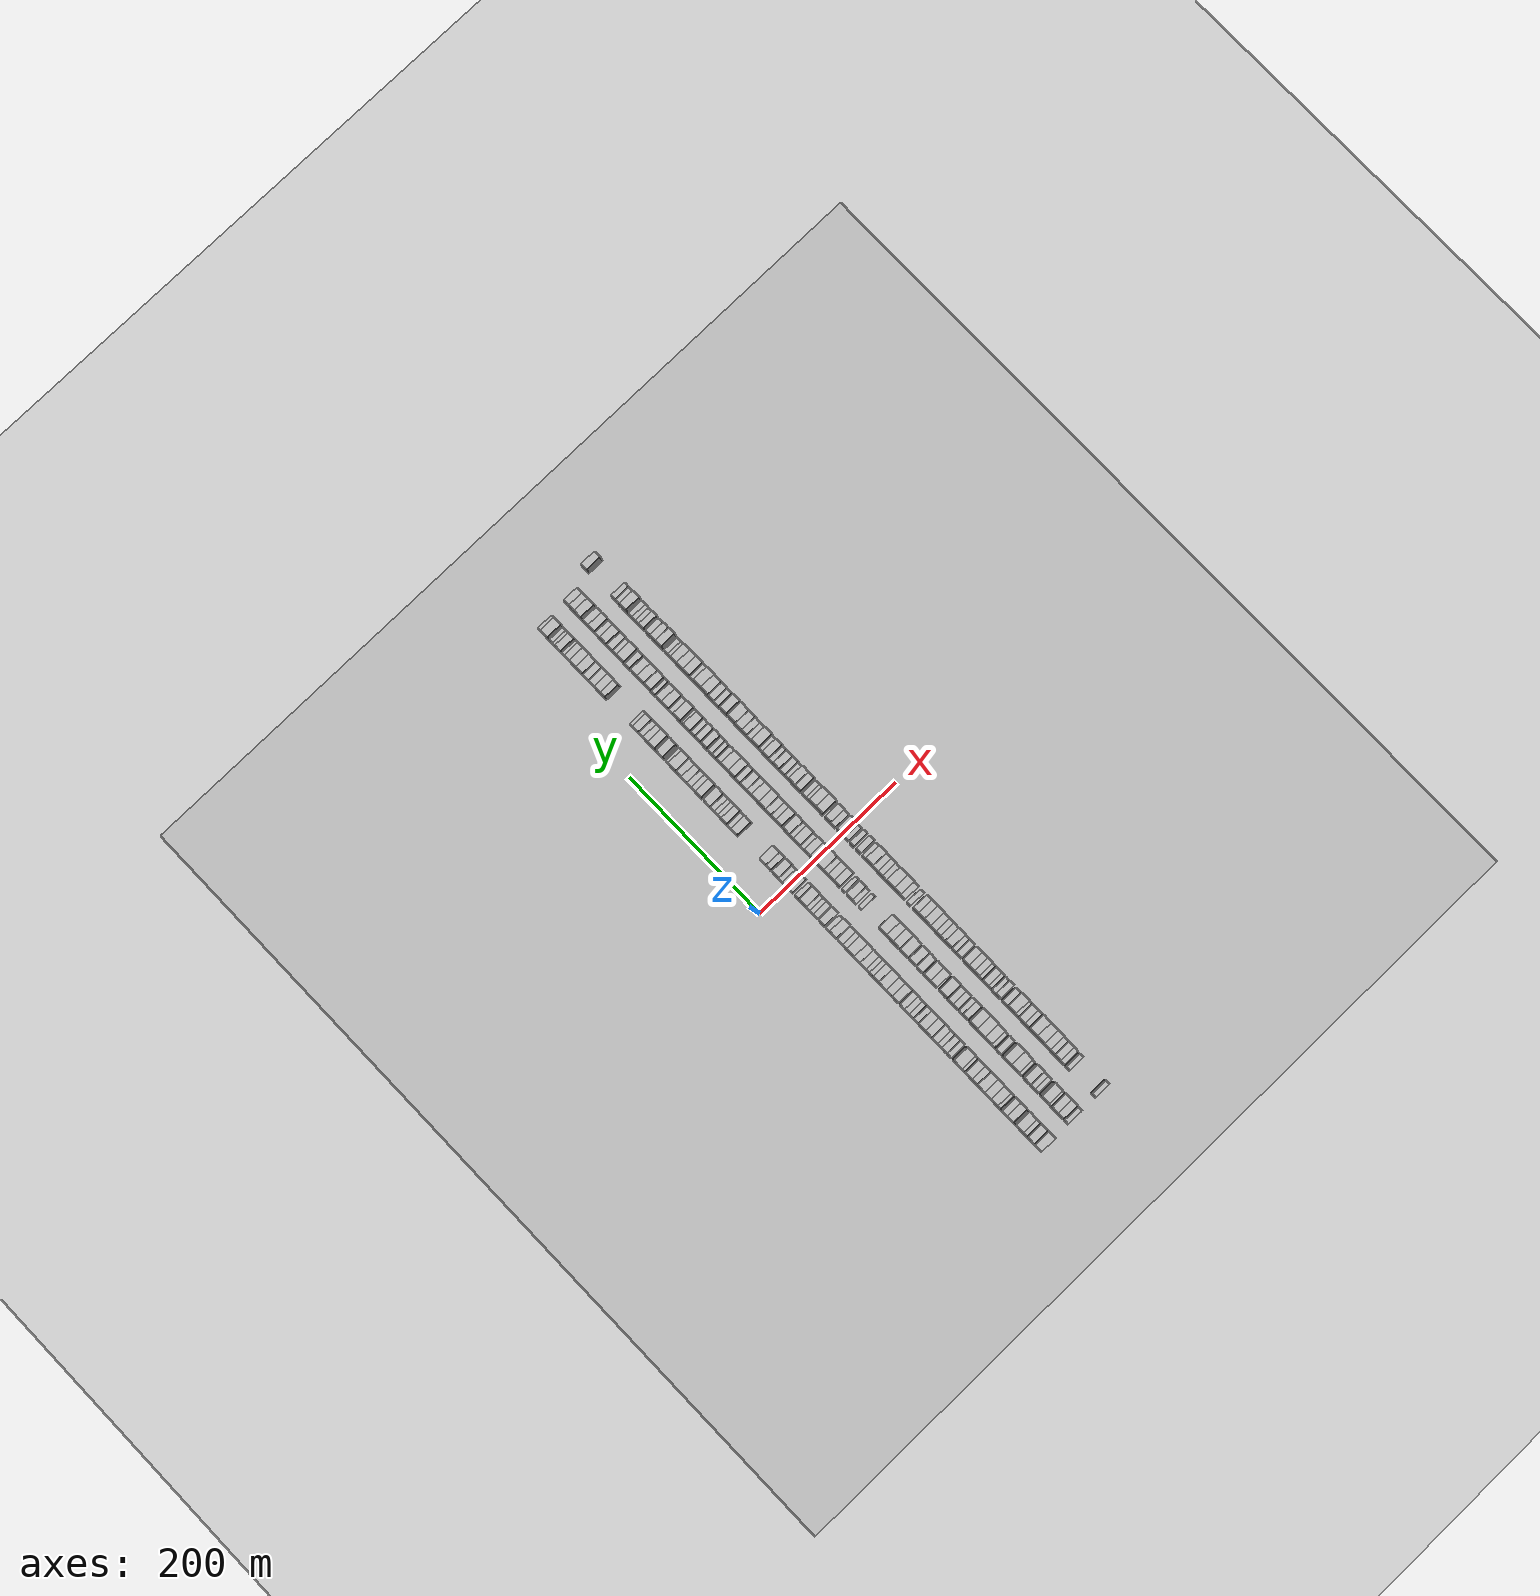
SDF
<?xml version="1.0" encoding="utf-8"?>

<sdf version="1.6">

   <world name="default">

      <gui fullscreen="0">

         <camera name="user_camera">

            <pose>-15 0 4.57585 0 0 0</pose>

            <view_controller>orbit</view_controller>

         </camera>

      </gui>

      <scene>

         <sky>

           <clouds>

             <speed>12</speed>

           </clouds>

         </sky>

         <ambient>0.4 0.4 0.4 1</ambient>

         <background>0.7 0.7 0.7 1</background>

         <shadows>1</shadows>

      </scene>

      <gravity>0 0 -9.8066</gravity>

      <magnetic_field>6e-06 2.3e-05 -4.2e-05</magnetic_field>

      <physics default="0" name="default_physics" type="ode">

         <ode>

            <solver>

               <type>quick</type>

               <iters>10</iters>

               <sor>1.0</sor>

               <use_dynamic_moi_rescaling>0</use_dynamic_moi_rescaling>

            </solver>

            <constraints>

               <cfm>0</cfm>

               <erp>0.2</erp>

               <contact_max_correcting_vel>100</contact_max_correcting_vel>

               <contact_surface_layer>0.001</contact_surface_layer>

            </constraints>

         </ode>

         <max_step_size>0.004</max_step_size>

         <real_time_factor>1</real_time_factor>

         <real_time_update_rate>250</real_time_update_rate>

      </physics>

      <light name="sun" type="directional">

         <cast_shadows>1</cast_shadows>

         <pose>0 0 10 0 0 0</pose>

         <diffuse>0.8 0.8 0.8 1</diffuse>

         <specular>0.2 0.2 0.2 1</specular>

         <attenuation>

            <range>1000</range>

            <constant>0.9</constant>

            <linear>0.01</linear>

            <quadratic>0.001</quadratic>

         </attenuation>

         <direction>-0.5 0.1 -0.9</direction>

      </light>

      <include>

         <name>ground_plane_1</name>

         <uri>model://HANNAS_ground_plane</uri>

         <pose>0 0 0  0 0 0</pose>

      </include>

      <include>

         <name>ground_plane_2</name>

         <uri>model://HANNAS_ground_plane</uri>

         <pose>100 0 0  0 0 0</pose>

      </include>

      <model name="building_1">

         <static>1</static>

         <pose frame="">50.0000 -374.0069 0 0.000000 0.000000 0.000000</pose>

         <link name="link">

            <pose frame="">0 0 12.00 0 0 0</pose>

            <collision name="collision">

               <geometry>

                  <box>

                     <size>20.0000 9.9862 24.0000</size>

                  </box>

               </geometry>

               <max_contacts>10</max_contacts>

               <surface>

                  <contact>

                     <ode/>

                  </contact>

                  <bounce/>

                  <friction>

                     <torsional>

                        <ode/>

                     </torsional>

                     <ode/>

                  </friction>

               </surface>

            </collision>

            <visual name="visual">

               <cast_shadows>0</cast_shadows>

               <geometry>

                  <box>

                     <size>20.0000 9.9862 24.0000</size>

                  </box>

               </geometry>

               <material>

                  <script>

                     <uri>model://HANNAS_wall/materials/scripts</uri>

                     <uri>model://HANNAS_wall/materials/textures</uri>

                     <name>vrc/HANNAS_wall</name>

                  </script>

               </material>

            </visual>

            <self_collide>0</self_collide>

            <enable_wind>0</enable_wind>

            <kinematic>0</kinematic>

         </link>

      </model>

      <model name="building_2">

         <static>1</static>

         <pose frame="">50.0000 -363.1482 0 0.000000 0.000000 0.000000</pose>

         <link name="link">

            <pose frame="">0 0 12.00 0 0 0</pose>

            <collision name="collision">

               <geometry>

                  <box>

                     <size>20.0000 9.7312 24.0000</size>

                  </box>

               </geometry>

               <max_contacts>10</max_contacts>

               <surface>

                  <contact>

                     <ode/>

                  </contact>

                  <bounce/>

                  <friction>

                     <torsional>

                        <ode/>

                     </torsional>

                     <ode/>

                  </friction>

               </surface>

            </collision>

            <visual name="visual">

               <cast_shadows>0</cast_shadows>

               <geometry>

                  <box>

                     <size>20.0000 9.7312 24.0000</size>

                  </box>

               </geometry>

               <material>

                  <script>

                     <uri>model://HANNAS_wall/materials/scripts</uri>

                     <uri>model://HANNAS_wall/materials/textures</uri>

                     <name>vrc/HANNAS_wall</name>

                  </script>

               </material>

            </visual>

            <self_collide>0</self_collide>

            <enable_wind>0</enable_wind>

            <kinematic>0</kinematic>

         </link>

      </model>

      <model name="building_3">

         <static>1</static>

         <pose frame="">50.0000 -355.2307 0 0.000000 0.000000 0.000000</pose>

         <link name="link">

            <pose frame="">0 0 7.50 0 0 0</pose>

            <collision name="collision">

               <geometry>

                  <box>

                     <size>20.0000 6.1038 15.0000</size>

                  </box>

               </geometry>

               <max_contacts>10</max_contacts>

               <surface>

                  <contact>

                     <ode/>

                  </contact>

                  <bounce/>

                  <friction>

                     <torsional>

                        <ode/>

                     </torsional>

                     <ode/>

                  </friction>

               </surface>

            </collision>

            <visual name="visual">

               <cast_shadows>0</cast_shadows>

               <geometry>

                  <box>

                     <size>20.0000 6.1038 15.0000</size>

                  </box>

               </geometry>

               <material>

                  <script>

                     <uri>model://HANNAS_wall/materials/scripts</uri>

                     <uri>model://HANNAS_wall/materials/textures</uri>

                     <name>vrc/HANNAS_wall</name>

                  </script>

               </material>

            </visual>

            <self_collide>0</self_collide>

            <enable_wind>0</enable_wind>

            <kinematic>0</kinematic>

         </link>

      </model>

      <model name="building_4">

         <static>1</static>

         <pose frame="">50.0000 -346.6774 0 0.000000 0.000000 0.000000</pose>

         <link name="link">

            <pose frame="">0 0 12.00 0 0 0</pose>

            <collision name="collision">

               <geometry>

                  <box>

                     <size>20.0000 11.0029 24.0000</size>

                  </box>

               </geometry>

               <max_contacts>10</max_contacts>

               <surface>

                  <contact>

                     <ode/>

                  </contact>

                  <bounce/>

                  <friction>

                     <torsional>

                        <ode/>

                     </torsional>

                     <ode/>

                  </friction>

               </surface>

            </collision>

            <visual name="visual">

               <cast_shadows>0</cast_shadows>

               <geometry>

                  <box>

                     <size>20.0000 11.0029 24.0000</size>

                  </box>

               </geometry>

               <material>

                  <script>

                     <uri>model://HANNAS_wall/materials/scripts</uri>

                     <uri>model://HANNAS_wall/materials/textures</uri>

                     <name>vrc/HANNAS_wall</name>

                  </script>

               </material>

            </visual>

            <self_collide>0</self_collide>

            <enable_wind>0</enable_wind>

            <kinematic>0</kinematic>

         </link>

      </model>

      <model name="building_5">

         <static>1</static>

         <pose frame="">50.0000 -333.7736 0 0.000000 0.000000 0.000000</pose>

         <link name="link">

            <pose frame="">0 0 9.00 0 0 0</pose>

            <collision name="collision">

               <geometry>

                  <box>

                     <size>20.0000 8.8047 18.0000</size>

                  </box>

               </geometry>

               <max_contacts>10</max_contacts>

               <surface>

                  <contact>

                     <ode/>

                  </contact>

                  <bounce/>

                  <friction>

                     <torsional>

                        <ode/>

                     </torsional>

                     <ode/>

                  </friction>

               </surface>

            </collision>

            <visual name="visual">

               <cast_shadows>0</cast_shadows>

               <geometry>

                  <box>

                     <size>20.0000 8.8047 18.0000</size>

                  </box>

               </geometry>

               <material>

                  <script>

                     <uri>model://HANNAS_wall/materials/scripts</uri>

                     <uri>model://HANNAS_wall/materials/textures</uri>

                     <name>vrc/HANNAS_wall</name>

                  </script>

               </material>

            </visual>

            <self_collide>0</self_collide>

            <enable_wind>0</enable_wind>

            <kinematic>0</kinematic>

         </link>

      </model>

      <model name="building_6">

         <static>1</static>

         <pose frame="">50.0000 -325.5919 0 0.000000 0.000000 0.000000</pose>

         <link name="link">

            <pose frame="">0 0 9.00 0 0 0</pose>

            <collision name="collision">

               <geometry>

                  <box>

                     <size>20.0000 7.5586 18.0000</size>

                  </box>

               </geometry>

               <max_contacts>10</max_contacts>

               <surface>

                  <contact>

                     <ode/>

                  </contact>

                  <bounce/>

                  <friction>

                     <torsional>

                        <ode/>

                     </torsional>

                     <ode/>

                  </friction>

               </surface>

            </collision>

            <visual name="visual">

               <cast_shadows>0</cast_shadows>

               <geometry>

                  <box>

                     <size>20.0000 7.5586 18.0000</size>

                  </box>

               </geometry>

               <material>

                  <script>

                     <uri>model://HANNAS_wall/materials/scripts</uri>

                     <uri>model://HANNAS_wall/materials/textures</uri>

                     <name>vrc/HANNAS_wall</name>

                  </script>

               </material>

            </visual>

            <self_collide>0</self_collide>

            <enable_wind>0</enable_wind>

            <kinematic>0</kinematic>

         </link>

      </model>

      <model name="building_7">

         <static>1</static>

         <pose frame="">50.0000 -317.2088 0 0.000000 0.000000 0.000000</pose>

         <link name="link">

            <pose frame="">0 0 6.00 0 0 0</pose>

            <collision name="collision">

               <geometry>

                  <box>

                     <size>20.0000 5.2076 12.0000</size>

                  </box>

               </geometry>

               <max_contacts>10</max_contacts>

               <surface>

                  <contact>

                     <ode/>

                  </contact>

                  <bounce/>

                  <friction>

                     <torsional>

                        <ode/>

                     </torsional>

                     <ode/>

                  </friction>

               </surface>

            </collision>

            <visual name="visual">

               <cast_shadows>0</cast_shadows>

               <geometry>

                  <box>

                     <size>20.0000 5.2076 12.0000</size>

                  </box>

               </geometry>

               <material>

                  <script>

                     <uri>model://HANNAS_wall/materials/scripts</uri>

                     <uri>model://HANNAS_wall/materials/textures</uri>

                     <name>vrc/HANNAS_wall</name>

                  </script>

               </material>

            </visual>

            <self_collide>0</self_collide>

            <enable_wind>0</enable_wind>

            <kinematic>0</kinematic>

         </link>

      </model>

      <model name="building_8">

         <static>1</static>

         <pose frame="">50.0000 -309.8113 0 0.000000 0.000000 0.000000</pose>

         <link name="link">

            <pose frame="">0 0 10.50 0 0 0</pose>

            <collision name="collision">

               <geometry>

                  <box>

                     <size>20.0000 9.5874 21.0000</size>

                  </box>

               </geometry>

               <max_contacts>10</max_contacts>

               <surface>

                  <contact>

                     <ode/>

                  </contact>

                  <bounce/>

                  <friction>

                     <torsional>

                        <ode/>

                     </torsional>

                     <ode/>

                  </friction>

               </surface>

            </collision>

            <visual name="visual">

               <cast_shadows>0</cast_shadows>

               <geometry>

                  <box>

                     <size>20.0000 9.5874 21.0000</size>

                  </box>

               </geometry>

               <material>

                  <script>

                     <uri>model://HANNAS_wall/materials/scripts</uri>

                     <uri>model://HANNAS_wall/materials/textures</uri>

                     <name>vrc/HANNAS_wall</name>

                  </script>

               </material>

            </visual>

            <self_collide>0</self_collide>

            <enable_wind>0</enable_wind>

            <kinematic>0</kinematic>

         </link>

      </model>

      <model name="building_9">

         <static>1</static>

         <pose frame="">50.0000 -300.0309 0 0.000000 0.000000 0.000000</pose>

         <link name="link">

            <pose frame="">0 0 10.50 0 0 0</pose>

            <collision name="collision">

               <geometry>

                  <box>

                     <size>20.0000 9.9735 21.0000</size>

                  </box>

               </geometry>

               <max_contacts>10</max_contacts>

               <surface>

                  <contact>

                     <ode/>

                  </contact>

                  <bounce/>

                  <friction>

                     <torsional>

                        <ode/>

                     </torsional>

                     <ode/>

                  </friction>

               </surface>

            </collision>

            <visual name="visual">

               <cast_shadows>0</cast_shadows>

               <geometry>

                  <box>

                     <size>20.0000 9.9735 21.0000</size>

                  </box>

               </geometry>

               <material>

                  <script>

                     <uri>model://HANNAS_wall/materials/scripts</uri>

                     <uri>model://HANNAS_wall/materials/textures</uri>

                     <name>vrc/HANNAS_wall</name>

                  </script>

               </material>

            </visual>

            <self_collide>0</self_collide>

            <enable_wind>0</enable_wind>

            <kinematic>0</kinematic>

         </link>

      </model>

      <model name="building_10">

         <static>1</static>

         <pose frame="">50.0000 -289.7704 0 0.000000 0.000000 0.000000</pose>

         <link name="link">

            <pose frame="">0 0 12.00 0 0 0</pose>

            <collision name="collision">

               <geometry>

                  <box>

                     <size>20.0000 10.5474 24.0000</size>

                  </box>

               </geometry>

               <max_contacts>10</max_contacts>

               <surface>

                  <contact>

                     <ode/>

                  </contact>

                  <bounce/>

                  <friction>

                     <torsional>

                        <ode/>

                     </torsional>

                     <ode/>

                  </friction>

               </surface>

            </collision>

            <visual name="visual">

               <cast_shadows>0</cast_shadows>

               <geometry>

                  <box>

                     <size>20.0000 10.5474 24.0000</size>

                  </box>

               </geometry>

               <material>

                  <script>

                     <uri>model://HANNAS_wall/materials/scripts</uri>

                     <uri>model://HANNAS_wall/materials/textures</uri>

                     <name>vrc/HANNAS_wall</name>

                  </script>

               </material>

            </visual>

            <self_collide>0</self_collide>

            <enable_wind>0</enable_wind>

            <kinematic>0</kinematic>

         </link>

      </model>

      <model name="building_11">

         <static>1</static>

         <pose frame="">50.0000 -280.6086 0 0.000000 0.000000 0.000000</pose>

         <link name="link">

            <pose frame="">0 0 9.00 0 0 0</pose>

            <collision name="collision">

               <geometry>

                  <box>

                     <size>20.0000 7.7760 18.0000</size>

                  </box>

               </geometry>

               <max_contacts>10</max_contacts>

               <surface>

                  <contact>

                     <ode/>

                  </contact>

                  <bounce/>

                  <friction>

                     <torsional>

                        <ode/>

                     </torsional>

                     <ode/>

                  </friction>

               </surface>

            </collision>

            <visual name="visual">

               <cast_shadows>0</cast_shadows>

               <geometry>

                  <box>

                     <size>20.0000 7.7760 18.0000</size>

                  </box>

               </geometry>

               <material>

                  <script>

                     <uri>model://HANNAS_wall/materials/scripts</uri>

                     <uri>model://HANNAS_wall/materials/textures</uri>

                     <name>vrc/HANNAS_wall</name>

                  </script>

               </material>

            </visual>

            <self_collide>0</self_collide>

            <enable_wind>0</enable_wind>

            <kinematic>0</kinematic>

         </link>

      </model>

      <model name="building_12">

         <static>1</static>

         <pose frame="">50.0000 -271.7725 0 0.000000 0.000000 0.000000</pose>

         <link name="link">

            <pose frame="">0 0 10.50 0 0 0</pose>

            <collision name="collision">

               <geometry>

                  <box>

                     <size>20.0000 9.8962 21.0000</size>

                  </box>

               </geometry>

               <max_contacts>10</max_contacts>

               <surface>

                  <contact>

                     <ode/>

                  </contact>

                  <bounce/>

                  <friction>

                     <torsional>

                        <ode/>

                     </torsional>

                     <ode/>

                  </friction>

               </surface>

            </collision>

            <visual name="visual">

               <cast_shadows>0</cast_shadows>

               <geometry>

                  <box>

                     <size>20.0000 9.8962 21.0000</size>

                  </box>

               </geometry>

               <material>

                  <script>

                     <uri>model://HANNAS_wall/materials/scripts</uri>

                     <uri>model://HANNAS_wall/materials/textures</uri>

                     <name>vrc/HANNAS_wall</name>

                  </script>

               </material>

            </visual>

            <self_collide>0</self_collide>

            <enable_wind>0</enable_wind>

            <kinematic>0</kinematic>

         </link>

      </model>

      <model name="building_13">

         <static>1</static>

         <pose frame="">50.0000 -264.1441 0 0.000000 0.000000 0.000000</pose>

         <link name="link">

            <pose frame="">0 0 6.00 0 0 0</pose>

            <collision name="collision">

               <geometry>

                  <box>

                     <size>20.0000 5.3607 12.0000</size>

                  </box>

               </geometry>

               <max_contacts>10</max_contacts>

               <surface>

                  <contact>

                     <ode/>

                  </contact>

                  <bounce/>

                  <friction>

                     <torsional>

                        <ode/>

                     </torsional>

                     <ode/>

                  </friction>

               </surface>

            </collision>

            <visual name="visual">

               <cast_shadows>0</cast_shadows>

               <geometry>

                  <box>

                     <size>20.0000 5.3607 12.0000</size>

                  </box>

               </geometry>

               <material>

                  <script>

                     <uri>model://HANNAS_wall/materials/scripts</uri>

                     <uri>model://HANNAS_wall/materials/textures</uri>

                     <name>vrc/HANNAS_wall</name>

                  </script>

               </material>

            </visual>

            <self_collide>0</self_collide>

            <enable_wind>0</enable_wind>

            <kinematic>0</kinematic>

         </link>

      </model>

      <model name="building_14">

         <static>1</static>

         <pose frame="">50.0000 -255.5503 0 0.000000 0.000000 0.000000</pose>

         <link name="link">

            <pose frame="">0 0 12.00 0 0 0</pose>

            <collision name="collision">

               <geometry>

                  <box>

                     <size>20.0000 11.8269 24.0000</size>

                  </box>

               </geometry>

               <max_contacts>10</max_contacts>

               <surface>

                  <contact>

                     <ode/>

                  </contact>

                  <bounce/>

                  <friction>

                     <torsional>

                        <ode/>

                     </torsional>

                     <ode/>

                  </friction>

               </surface>

            </collision>

            <visual name="visual">

               <cast_shadows>0</cast_shadows>

               <geometry>

                  <box>

                     <size>20.0000 11.8269 24.0000</size>

                  </box>

               </geometry>

               <material>

                  <script>

                     <uri>model://HANNAS_wall/materials/scripts</uri>

                     <uri>model://HANNAS_wall/materials/textures</uri>

                     <name>vrc/HANNAS_wall</name>

                  </script>

               </material>

            </visual>

            <self_collide>0</self_collide>

            <enable_wind>0</enable_wind>

            <kinematic>0</kinematic>

         </link>

      </model>

      <model name="building_15">

         <static>1</static>

         <pose frame="">50.0000 -243.6844 0 0.000000 0.000000 0.000000</pose>

         <link name="link">

            <pose frame="">0 0 6.00 0 0 0</pose>

            <collision name="collision">

               <geometry>

                  <box>

                     <size>20.0000 5.9048 12.0000</size>

                  </box>

               </geometry>

               <max_contacts>10</max_contacts>

               <surface>

                  <contact>

                     <ode/>

                  </contact>

                  <bounce/>

                  <friction>

                     <torsional>

                        <ode/>

                     </torsional>

                     <ode/>

                  </friction>

               </surface>

            </collision>

            <visual name="visual">

               <cast_shadows>0</cast_shadows>

               <geometry>

                  <box>

                     <size>20.0000 5.9048 12.0000</size>

                  </box>

               </geometry>

               <material>

                  <script>

                     <uri>model://HANNAS_wall/materials/scripts</uri>

                     <uri>model://HANNAS_wall/materials/textures</uri>

                     <name>vrc/HANNAS_wall</name>

                  </script>

               </material>

            </visual>

            <self_collide>0</self_collide>

            <enable_wind>0</enable_wind>

            <kinematic>0</kinematic>

         </link>

      </model>

      <model name="building_16">

         <static>1</static>

         <pose frame="">50.0000 -235.9059 0 0.000000 0.000000 0.000000</pose>

         <link name="link">

            <pose frame="">0 0 9.00 0 0 0</pose>

            <collision name="collision">

               <geometry>

                  <box>

                     <size>20.0000 7.6523 18.0000</size>

                  </box>

               </geometry>

               <max_contacts>10</max_contacts>

               <surface>

                  <contact>

                     <ode/>

                  </contact>

                  <bounce/>

                  <friction>

                     <torsional>

                        <ode/>

                     </torsional>

                     <ode/>

                  </friction>

               </surface>

            </collision>

            <visual name="visual">

               <cast_shadows>0</cast_shadows>

               <geometry>

                  <box>

                     <size>20.0000 7.6523 18.0000</size>

                  </box>

               </geometry>

               <material>

                  <script>

                     <uri>model://HANNAS_wall/materials/scripts</uri>

                     <uri>model://HANNAS_wall/materials/textures</uri>

                     <name>vrc/HANNAS_wall</name>

                  </script>

               </material>

            </visual>

            <self_collide>0</self_collide>

            <enable_wind>0</enable_wind>

            <kinematic>0</kinematic>

         </link>

      </model>

      <model name="building_17">

         <static>1</static>

         <pose frame="">50.0000 -229.0683 0 0.000000 0.000000 0.000000</pose>

         <link name="link">

            <pose frame="">0 0 7.50 0 0 0</pose>

            <collision name="collision">

               <geometry>

                  <box>

                     <size>20.0000 6.0229 15.0000</size>

                  </box>

               </geometry>

               <max_contacts>10</max_contacts>

               <surface>

                  <contact>

                     <ode/>

                  </contact>

                  <bounce/>

                  <friction>

                     <torsional>

                        <ode/>

                     </torsional>

                     <ode/>

                  </friction>

               </surface>

            </collision>

            <visual name="visual">

               <cast_shadows>0</cast_shadows>

               <geometry>

                  <box>

                     <size>20.0000 6.0229 15.0000</size>

                  </box>

               </geometry>

               <material>

                  <script>

                     <uri>model://HANNAS_wall/materials/scripts</uri>

                     <uri>model://HANNAS_wall/materials/textures</uri>

                     <name>vrc/HANNAS_wall</name>

                  </script>

               </material>

            </visual>

            <self_collide>0</self_collide>

            <enable_wind>0</enable_wind>

            <kinematic>0</kinematic>

         </link>

      </model>

      <model name="building_18">

         <static>1</static>

         <pose frame="">50.0000 -221.9553 0 0.000000 0.000000 0.000000</pose>

         <link name="link">

            <pose frame="">0 0 9.00 0 0 0</pose>

            <collision name="collision">

               <geometry>

                  <box>

                     <size>20.0000 8.2030 18.0000</size>

                  </box>

               </geometry>

               <max_contacts>10</max_contacts>

               <surface>

                  <contact>

                     <ode/>

                  </contact>

                  <bounce/>

                  <friction>

                     <torsional>

                        <ode/>

                     </torsional>

                     <ode/>

                  </friction>

               </surface>

            </collision>

            <visual name="visual">

               <cast_shadows>0</cast_shadows>

               <geometry>

                  <box>

                     <size>20.0000 8.2030 18.0000</size>

                  </box>

               </geometry>

               <material>

                  <script>

                     <uri>model://HANNAS_wall/materials/scripts</uri>

                     <uri>model://HANNAS_wall/materials/textures</uri>

                     <name>vrc/HANNAS_wall</name>

                  </script>

               </material>

            </visual>

            <self_collide>0</self_collide>

            <enable_wind>0</enable_wind>

            <kinematic>0</kinematic>

         </link>

      </model>

      <model name="building_19">

         <static>1</static>

         <pose frame="">50.0000 -211.9176 0 0.000000 0.000000 0.000000</pose>

         <link name="link">

            <pose frame="">0 0 10.50 0 0 0</pose>

            <collision name="collision">

               <geometry>

                  <box>

                     <size>20.0000 9.8726 21.0000</size>

                  </box>

               </geometry>

               <max_contacts>10</max_contacts>

               <surface>

                  <contact>

                     <ode/>

                  </contact>

                  <bounce/>

                  <friction>

                     <torsional>

                        <ode/>

                     </torsional>

                     <ode/>

                  </friction>

               </surface>

            </collision>

            <visual name="visual">

               <cast_shadows>0</cast_shadows>

               <geometry>

                  <box>

                     <size>20.0000 9.8726 21.0000</size>

                  </box>

               </geometry>

               <material>

                  <script>

                     <uri>model://HANNAS_wall/materials/scripts</uri>

                     <uri>model://HANNAS_wall/materials/textures</uri>

                     <name>vrc/HANNAS_wall</name>

                  </script>

               </material>

            </visual>

            <self_collide>0</self_collide>

            <enable_wind>0</enable_wind>

            <kinematic>0</kinematic>

         </link>

      </model>

      <model name="building_20">

         <static>1</static>

         <pose frame="">50.0000 -202.0999 0 0.000000 0.000000 0.000000</pose>

         <link name="link">

            <pose frame="">0 0 12.00 0 0 0</pose>

            <collision name="collision">

               <geometry>

                  <box>

                     <size>20.0000 9.7628 24.0000</size>

                  </box>

               </geometry>

               <max_contacts>10</max_contacts>

               <surface>

                  <contact>

                     <ode/>

                  </contact>

                  <bounce/>

                  <friction>

                     <torsional>

                        <ode/>

                     </torsional>

                     <ode/>

                  </friction>

               </surface>

            </collision>

            <visual name="visual">

               <cast_shadows>0</cast_shadows>

               <geometry>

                  <box>

                     <size>20.0000 9.7628 24.0000</size>

                  </box>

               </geometry>

               <material>

                  <script>

                     <uri>model://HANNAS_wall/materials/scripts</uri>

                     <uri>model://HANNAS_wall/materials/textures</uri>

                     <name>vrc/HANNAS_wall</name>

                  </script>

               </material>

            </visual>

            <self_collide>0</self_collide>

            <enable_wind>0</enable_wind>

            <kinematic>0</kinematic>

         </link>

      </model>

      <model name="building_21">

         <static>1</static>

         <pose frame="">50.0000 -193.9671 0 0.000000 0.000000 0.000000</pose>

         <link name="link">

            <pose frame="">0 0 7.50 0 0 0</pose>

            <collision name="collision">

               <geometry>

                  <box>

                     <size>20.0000 6.5026 15.0000</size>

                  </box>

               </geometry>

               <max_contacts>10</max_contacts>

               <surface>

                  <contact>

                     <ode/>

                  </contact>

                  <bounce/>

                  <friction>

                     <torsional>

                        <ode/>

                     </torsional>

                     <ode/>

                  </friction>

               </surface>

            </collision>

            <visual name="visual">

               <cast_shadows>0</cast_shadows>

               <geometry>

                  <box>

                     <size>20.0000 6.5026 15.0000</size>

                  </box>

               </geometry>

               <material>

                  <script>

                     <uri>model://HANNAS_wall/materials/scripts</uri>

                     <uri>model://HANNAS_wall/materials/textures</uri>

                     <name>vrc/HANNAS_wall</name>

                  </script>

               </material>

            </visual>

            <self_collide>0</self_collide>

            <enable_wind>0</enable_wind>

            <kinematic>0</kinematic>

         </link>

      </model>

      <model name="building_22">

         <static>1</static>

         <pose frame="">50.0000 -186.6353 0 0.000000 0.000000 0.000000</pose>

         <link name="link">

            <pose frame="">0 0 7.50 0 0 0</pose>

            <collision name="collision">

               <geometry>

                  <box>

                     <size>20.0000 6.1611 15.0000</size>

                  </box>

               </geometry>

               <max_contacts>10</max_contacts>

               <surface>

                  <contact>

                     <ode/>

                  </contact>

                  <bounce/>

                  <friction>

                     <torsional>

                        <ode/>

                     </torsional>

                     <ode/>

                  </friction>

               </surface>

            </collision>

            <visual name="visual">

               <cast_shadows>0</cast_shadows>

               <geometry>

                  <box>

                     <size>20.0000 6.1611 15.0000</size>

                  </box>

               </geometry>

               <material>

                  <script>

                     <uri>model://HANNAS_wall/materials/scripts</uri>

                     <uri>model://HANNAS_wall/materials/textures</uri>

                     <name>vrc/HANNAS_wall</name>

                  </script>

               </material>

            </visual>

            <self_collide>0</self_collide>

            <enable_wind>0</enable_wind>

            <kinematic>0</kinematic>

         </link>

      </model>

      <model name="building_23">

         <static>1</static>

         <pose frame="">50.0000 -180.1994 0 0.000000 0.000000 0.000000</pose>

         <link name="link">

            <pose frame="">0 0 7.50 0 0 0</pose>

            <collision name="collision">

               <geometry>

                  <box>

                     <size>20.0000 6.7107 15.0000</size>

                  </box>

               </geometry>

               <max_contacts>10</max_contacts>

               <surface>

                  <contact>

                     <ode/>

                  </contact>

                  <bounce/>

                  <friction>

                     <torsional>

                        <ode/>

                     </torsional>

                     <ode/>

                  </friction>

               </surface>

            </collision>

            <visual name="visual">

               <cast_shadows>0</cast_shadows>

               <geometry>

                  <box>

                     <size>20.0000 6.7107 15.0000</size>

                  </box>

               </geometry>

               <material>

                  <script>

                     <uri>model://HANNAS_wall/materials/scripts</uri>

                     <uri>model://HANNAS_wall/materials/textures</uri>

                     <name>vrc/HANNAS_wall</name>

                  </script>

               </material>

            </visual>

            <self_collide>0</self_collide>

            <enable_wind>0</enable_wind>

            <kinematic>0</kinematic>

         </link>

      </model>

      <model name="building_24">

         <static>1</static>

         <pose frame="">50.0000 -173.2218 0 0.000000 0.000000 0.000000</pose>

         <link name="link">

            <pose frame="">0 0 7.50 0 0 0</pose>

            <collision name="collision">

               <geometry>

                  <box>

                     <size>20.0000 7.2445 15.0000</size>

                  </box>

               </geometry>

               <max_contacts>10</max_contacts>

               <surface>

                  <contact>

                     <ode/>

                  </contact>

                  <bounce/>

                  <friction>

                     <torsional>

                        <ode/>

                     </torsional>

                     <ode/>

                  </friction>

               </surface>

            </collision>

            <visual name="visual">

               <cast_shadows>0</cast_shadows>

               <geometry>

                  <box>

                     <size>20.0000 7.2445 15.0000</size>

                  </box>

               </geometry>

               <material>

                  <script>

                     <uri>model://HANNAS_wall/materials/scripts</uri>

                     <uri>model://HANNAS_wall/materials/textures</uri>

                     <name>vrc/HANNAS_wall</name>

                  </script>

               </material>

            </visual>

            <self_collide>0</self_collide>

            <enable_wind>0</enable_wind>

            <kinematic>0</kinematic>

         </link>

      </model>

      <model name="building_25">

         <static>1</static>

         <pose frame="">50.0000 -162.6572 0 0.000000 0.000000 0.000000</pose>

         <link name="link">

            <pose frame="">0 0 10.50 0 0 0</pose>

            <collision name="collision">

               <geometry>

                  <box>

                     <size>20.0000 9.8846 21.0000</size>

                  </box>

               </geometry>

               <max_contacts>10</max_contacts>

               <surface>

                  <contact>

                     <ode/>

                  </contact>

                  <bounce/>

                  <friction>

                     <torsional>

                        <ode/>

                     </torsional>

                     <ode/>

                  </friction>

               </surface>

            </collision>

            <visual name="visual">

               <cast_shadows>0</cast_shadows>

               <geometry>

                  <box>

                     <size>20.0000 9.8846 21.0000</size>

                  </box>

               </geometry>

               <material>

                  <script>

                     <uri>model://HANNAS_wall/materials/scripts</uri>

                     <uri>model://HANNAS_wall/materials/textures</uri>

                     <name>vrc/HANNAS_wall</name>

                  </script>

               </material>

            </visual>

            <self_collide>0</self_collide>

            <enable_wind>0</enable_wind>

            <kinematic>0</kinematic>

         </link>

      </model>

      <model name="building_26">

         <static>1</static>

         <pose frame="">50.0000 -153.3153 0 0.000000 0.000000 0.000000</pose>

         <link name="link">

            <pose frame="">0 0 9.00 0 0 0</pose>

            <collision name="collision">

               <geometry>

                  <box>

                     <size>20.0000 8.7991 18.0000</size>

                  </box>

               </geometry>

               <max_contacts>10</max_contacts>

               <surface>

                  <contact>

                     <ode/>

                  </contact>

                  <bounce/>

                  <friction>

                     <torsional>

                        <ode/>

                     </torsional>

                     <ode/>

                  </friction>

               </surface>

            </collision>

            <visual name="visual">

               <cast_shadows>0</cast_shadows>

               <geometry>

                  <box>

                     <size>20.0000 8.7991 18.0000</size>

                  </box>

               </geometry>

               <material>

                  <script>

                     <uri>model://HANNAS_wall/materials/scripts</uri>

                     <uri>model://HANNAS_wall/materials/textures</uri>

                     <name>vrc/HANNAS_wall</name>

                  </script>

               </material>

            </visual>

            <self_collide>0</self_collide>

            <enable_wind>0</enable_wind>

            <kinematic>0</kinematic>

         </link>

      </model>

      <model name="building_27">

         <static>1</static>

         <pose frame="">50.0000 -143.3040 0 0.000000 0.000000 0.000000</pose>

         <link name="link">

            <pose frame="">0 0 12.00 0 0 0</pose>

            <collision name="collision">

               <geometry>

                  <box>

                     <size>20.0000 11.2236 24.0000</size>

                  </box>

               </geometry>

               <max_contacts>10</max_contacts>

               <surface>

                  <contact>

                     <ode/>

                  </contact>

                  <bounce/>

                  <friction>

                     <torsional>

                        <ode/>

                     </torsional>

                     <ode/>

                  </friction>

               </surface>

            </collision>

            <visual name="visual">

               <cast_shadows>0</cast_shadows>

               <geometry>

                  <box>

                     <size>20.0000 11.2236 24.0000</size>

                  </box>

               </geometry>

               <material>

                  <script>

                     <uri>model://HANNAS_wall/materials/scripts</uri>

                     <uri>model://HANNAS_wall/materials/textures</uri>

                     <name>vrc/HANNAS_wall</name>

                  </script>

               </material>

            </visual>

            <self_collide>0</self_collide>

            <enable_wind>0</enable_wind>

            <kinematic>0</kinematic>

         </link>

      </model>

      <model name="building_28">

         <static>1</static>

         <pose frame="">50.0000 -133.4801 0 0.000000 0.000000 0.000000</pose>

         <link name="link">

            <pose frame="">0 0 10.50 0 0 0</pose>

            <collision name="collision">

               <geometry>

                  <box>

                     <size>20.0000 8.4241 21.0000</size>

                  </box>

               </geometry>

               <max_contacts>10</max_contacts>

               <surface>

                  <contact>

                     <ode/>

                  </contact>

                  <bounce/>

                  <friction>

                     <torsional>

                        <ode/>

                     </torsional>

                     <ode/>

                  </friction>

               </surface>

            </collision>

            <visual name="visual">

               <cast_shadows>0</cast_shadows>

               <geometry>

                  <box>

                     <size>20.0000 8.4241 21.0000</size>

                  </box>

               </geometry>

               <material>

                  <script>

                     <uri>model://HANNAS_wall/materials/scripts</uri>

                     <uri>model://HANNAS_wall/materials/textures</uri>

                     <name>vrc/HANNAS_wall</name>

                  </script>

               </material>

            </visual>

            <self_collide>0</self_collide>

            <enable_wind>0</enable_wind>

            <kinematic>0</kinematic>

         </link>

      </model>

      <model name="building_29">

         <static>1</static>

         <pose frame="">50.0000 -126.6623 0 0.000000 0.000000 0.000000</pose>

         <link name="link">

            <pose frame="">0 0 6.00 0 0 0</pose>

            <collision name="collision">

               <geometry>

                  <box>

                     <size>20.0000 5.2115 12.0000</size>

                  </box>

               </geometry>

               <max_contacts>10</max_contacts>

               <surface>

                  <contact>

                     <ode/>

                  </contact>

                  <bounce/>

                  <friction>

                     <torsional>

                        <ode/>

                     </torsional>

                     <ode/>

                  </friction>

               </surface>

            </collision>

            <visual name="visual">

               <cast_shadows>0</cast_shadows>

               <geometry>

                  <box>

                     <size>20.0000 5.2115 12.0000</size>

                  </box>

               </geometry>

               <material>

                  <script>

                     <uri>model://HANNAS_wall/materials/scripts</uri>

                     <uri>model://HANNAS_wall/materials/textures</uri>

                     <name>vrc/HANNAS_wall</name>

                  </script>

               </material>

            </visual>

            <self_collide>0</self_collide>

            <enable_wind>0</enable_wind>

            <kinematic>0</kinematic>

         </link>

      </model>

      <model name="building_30">

         <static>1</static>

         <pose frame="">50.0000 -121.4434 0 0.000000 0.000000 0.000000</pose>

         <link name="link">

            <pose frame="">0 0 6.00 0 0 0</pose>

            <collision name="collision">

               <geometry>

                  <box>

                     <size>20.0000 5.2263 12.0000</size>

                  </box>

               </geometry>

               <max_contacts>10</max_contacts>

               <surface>

                  <contact>

                     <ode/>

                  </contact>

                  <bounce/>

                  <friction>

                     <torsional>

                        <ode/>

                     </torsional>

                     <ode/>

                  </friction>

               </surface>

            </collision>

            <visual name="visual">

               <cast_shadows>0</cast_shadows>

               <geometry>

                  <box>

                     <size>20.0000 5.2263 12.0000</size>

                  </box>

               </geometry>

               <material>

                  <script>

                     <uri>model://HANNAS_wall/materials/scripts</uri>

                     <uri>model://HANNAS_wall/materials/textures</uri>

                     <name>vrc/HANNAS_wall</name>

                  </script>

               </material>

            </visual>

            <self_collide>0</self_collide>

            <enable_wind>0</enable_wind>

            <kinematic>0</kinematic>

         </link>

      </model>

      <model name="building_31">

         <static>1</static>

         <pose frame="">50.0000 -114.3831 0 0.000000 0.000000 0.000000</pose>

         <link name="link">

            <pose frame="">0 0 10.50 0 0 0</pose>

            <collision name="collision">

               <geometry>

                  <box>

                     <size>20.0000 8.8944 21.0000</size>

                  </box>

               </geometry>

               <max_contacts>10</max_contacts>

               <surface>

                  <contact>

                     <ode/>

                  </contact>

                  <bounce/>

                  <friction>

                     <torsional>

                        <ode/>

                     </torsional>

                     <ode/>

                  </friction>

               </surface>

            </collision>

            <visual name="visual">

               <cast_shadows>0</cast_shadows>

               <geometry>

                  <box>

                     <size>20.0000 8.8944 21.0000</size>

                  </box>

               </geometry>

               <material>

                  <script>

                     <uri>model://HANNAS_wall/materials/scripts</uri>

                     <uri>model://HANNAS_wall/materials/textures</uri>

                     <name>vrc/HANNAS_wall</name>

                  </script>

               </material>

            </visual>

            <self_collide>0</self_collide>

            <enable_wind>0</enable_wind>

            <kinematic>0</kinematic>

         </link>

      </model>

      <model name="building_32">

         <static>1</static>

         <pose frame="">50.0000 -105.4731 0 0.000000 0.000000 0.000000</pose>

         <link name="link">

            <pose frame="">0 0 9.00 0 0 0</pose>

            <collision name="collision">

               <geometry>

                  <box>

                     <size>20.0000 8.9255 18.0000</size>

                  </box>

               </geometry>

               <max_contacts>10</max_contacts>

               <surface>

                  <contact>

                     <ode/>

                  </contact>

                  <bounce/>

                  <friction>

                     <torsional>

                        <ode/>

                     </torsional>

                     <ode/>

                  </friction>

               </surface>

            </collision>

            <visual name="visual">

               <cast_shadows>0</cast_shadows>

               <geometry>

                  <box>

                     <size>20.0000 8.9255 18.0000</size>

                  </box>

               </geometry>

               <material>

                  <script>

                     <uri>model://HANNAS_wall/materials/scripts</uri>

                     <uri>model://HANNAS_wall/materials/textures</uri>

                     <name>vrc/HANNAS_wall</name>

                  </script>

               </material>

            </visual>

            <self_collide>0</self_collide>

            <enable_wind>0</enable_wind>

            <kinematic>0</kinematic>

         </link>

      </model>

      <model name="building_33">

         <static>1</static>

         <pose frame="">50.0000 -95.3395 0 0.000000 0.000000 0.000000</pose>

         <link name="link">

            <pose frame="">0 0 12.00 0 0 0</pose>

            <collision name="collision">

               <geometry>

                  <box>

                     <size>20.0000 11.3417 24.0000</size>

                  </box>

               </geometry>

               <max_contacts>10</max_contacts>

               <surface>

                  <contact>

                     <ode/>

                  </contact>

                  <bounce/>

                  <friction>

                     <torsional>

                        <ode/>

                     </torsional>

                     <ode/>

                  </friction>

               </surface>

            </collision>

            <visual name="visual">

               <cast_shadows>0</cast_shadows>

               <geometry>

                  <box>

                     <size>20.0000 11.3417 24.0000</size>

                  </box>

               </geometry>

               <material>

                  <script>

                     <uri>model://HANNAS_wall/materials/scripts</uri>

                     <uri>model://HANNAS_wall/materials/textures</uri>

                     <name>vrc/HANNAS_wall</name>

                  </script>

               </material>

            </visual>

            <self_collide>0</self_collide>

            <enable_wind>0</enable_wind>

            <kinematic>0</kinematic>

         </link>

      </model>

      <model name="building_34">

         <static>1</static>

         <pose frame="">50.0000 -86.6856 0 0.000000 0.000000 0.000000</pose>

         <link name="link">

            <pose frame="">0 0 6.00 0 0 0</pose>

            <collision name="collision">

               <geometry>

                  <box>

                     <size>20.0000 5.9661 12.0000</size>

                  </box>

               </geometry>

               <max_contacts>10</max_contacts>

               <surface>

                  <contact>

                     <ode/>

                  </contact>

                  <bounce/>

                  <friction>

                     <torsional>

                        <ode/>

                     </torsional>

                     <ode/>

                  </friction>

               </surface>

            </collision>

            <visual name="visual">

               <cast_shadows>0</cast_shadows>

               <geometry>

                  <box>

                     <size>20.0000 5.9661 12.0000</size>

                  </box>

               </geometry>

               <material>

                  <script>

                     <uri>model://HANNAS_wall/materials/scripts</uri>

                     <uri>model://HANNAS_wall/materials/textures</uri>

                     <name>vrc/HANNAS_wall</name>

                  </script>

               </material>

            </visual>

            <self_collide>0</self_collide>

            <enable_wind>0</enable_wind>

            <kinematic>0</kinematic>

         </link>

      </model>

      <model name="building_35">

         <static>1</static>

         <pose frame="">50.0000 -79.6899 0 0.000000 0.000000 0.000000</pose>

         <link name="link">

            <pose frame="">0 0 9.00 0 0 0</pose>

            <collision name="collision">

               <geometry>

                  <box>

                     <size>20.0000 8.0252 18.0000</size>

                  </box>

               </geometry>

               <max_contacts>10</max_contacts>

               <surface>

                  <contact>

                     <ode/>

                  </contact>

                  <bounce/>

                  <friction>

                     <torsional>

                        <ode/>

                     </torsional>

                     <ode/>

                  </friction>

               </surface>

            </collision>

            <visual name="visual">

               <cast_shadows>0</cast_shadows>

               <geometry>

                  <box>

                     <size>20.0000 8.0252 18.0000</size>

                  </box>

               </geometry>

               <material>

                  <script>

                     <uri>model://HANNAS_wall/materials/scripts</uri>

                     <uri>model://HANNAS_wall/materials/textures</uri>

                     <name>vrc/HANNAS_wall</name>

                  </script>

               </material>

            </visual>

            <self_collide>0</self_collide>

            <enable_wind>0</enable_wind>

            <kinematic>0</kinematic>

         </link>

      </model>

      <model name="building_36">

         <static>1</static>

         <pose frame="">50.0000 -69.5287 0 0.000000 0.000000 0.000000</pose>

         <link name="link">

            <pose frame="">0 0 12.00 0 0 0</pose>

            <collision name="collision">

               <geometry>

                  <box>

                     <size>20.0000 10.2972 24.0000</size>

                  </box>

               </geometry>

               <max_contacts>10</max_contacts>

               <surface>

                  <contact>

                     <ode/>

                  </contact>

                  <bounce/>

                  <friction>

                     <torsional>

                        <ode/>

                     </torsional>

                     <ode/>

                  </friction>

               </surface>

            </collision>

            <visual name="visual">

               <cast_shadows>0</cast_shadows>

               <geometry>

                  <box>

                     <size>20.0000 10.2972 24.0000</size>

                  </box>

               </geometry>

               <material>

                  <script>

                     <uri>model://HANNAS_wall/materials/scripts</uri>

                     <uri>model://HANNAS_wall/materials/textures</uri>

                     <name>vrc/HANNAS_wall</name>

                  </script>

               </material>

            </visual>

            <self_collide>0</self_collide>

            <enable_wind>0</enable_wind>

            <kinematic>0</kinematic>

         </link>

      </model>

      <model name="building_37">

         <static>1</static>

         <pose frame="">50.0000 -61.6274 0 0.000000 0.000000 0.000000</pose>

         <link name="link">

            <pose frame="">0 0 6.00 0 0 0</pose>

            <collision name="collision">

               <geometry>

                  <box>

                     <size>20.0000 5.5054 12.0000</size>

                  </box>

               </geometry>

               <max_contacts>10</max_contacts>

               <surface>

                  <contact>

                     <ode/>

                  </contact>

                  <bounce/>

                  <friction>

                     <torsional>

                        <ode/>

                     </torsional>

                     <ode/>

                  </friction>

               </surface>

            </collision>

            <visual name="visual">

               <cast_shadows>0</cast_shadows>

               <geometry>

                  <box>

                     <size>20.0000 5.5054 12.0000</size>

                  </box>

               </geometry>

               <material>

                  <script>

                     <uri>model://HANNAS_wall/materials/scripts</uri>

                     <uri>model://HANNAS_wall/materials/textures</uri>

                     <name>vrc/HANNAS_wall</name>

                  </script>

               </material>

            </visual>

            <self_collide>0</self_collide>

            <enable_wind>0</enable_wind>

            <kinematic>0</kinematic>

         </link>

      </model>

      <model name="building_38">

         <static>1</static>

         <pose frame="">50.0000 -52.4011 0 0.000000 0.000000 0.000000</pose>

         <link name="link">

            <pose frame="">0 0 10.50 0 0 0</pose>

            <collision name="collision">

               <geometry>

                  <box>

                     <size>20.0000 8.9473 21.0000</size>

                  </box>

               </geometry>

               <max_contacts>10</max_contacts>

               <surface>

                  <contact>

                     <ode/>

                  </contact>

                  <bounce/>

                  <friction>

                     <torsional>

                        <ode/>

                     </torsional>

                     <ode/>

                  </friction>

               </surface>

            </collision>

            <visual name="visual">

               <cast_shadows>0</cast_shadows>

               <geometry>

                  <box>

                     <size>20.0000 8.9473 21.0000</size>

                  </box>

               </geometry>

               <material>

                  <script>

                     <uri>model://HANNAS_wall/materials/scripts</uri>

                     <uri>model://HANNAS_wall/materials/textures</uri>

                     <name>vrc/HANNAS_wall</name>

                  </script>

               </material>

            </visual>

            <self_collide>0</self_collide>

            <enable_wind>0</enable_wind>

            <kinematic>0</kinematic>

         </link>

      </model>

      <model name="building_39">

         <static>1</static>

         <pose frame="">50.0000 -42.5982 0 0.000000 0.000000 0.000000</pose>

         <link name="link">

            <pose frame="">0 0 7.50 0 0 0</pose>

            <collision name="collision">

               <geometry>

                  <box>

                     <size>20.0000 6.6586 15.0000</size>

                  </box>

               </geometry>

               <max_contacts>10</max_contacts>

               <surface>

                  <contact>

                     <ode/>

                  </contact>

                  <bounce/>

                  <friction>

                     <torsional>

                        <ode/>

                     </torsional>

                     <ode/>

                  </friction>

               </surface>

            </collision>

            <visual name="visual">

               <cast_shadows>0</cast_shadows>

               <geometry>

                  <box>

                     <size>20.0000 6.6586 15.0000</size>

                  </box>

               </geometry>

               <material>

                  <script>

                     <uri>model://HANNAS_wall/materials/scripts</uri>

                     <uri>model://HANNAS_wall/materials/textures</uri>

                     <name>vrc/HANNAS_wall</name>

                  </script>

               </material>

            </visual>

            <self_collide>0</self_collide>

            <enable_wind>0</enable_wind>

            <kinematic>0</kinematic>

         </link>

      </model>

      <model name="building_40">

         <static>1</static>

         <pose frame="">50.0000 -36.8276 0 0.000000 0.000000 0.000000</pose>

         <link name="link">

            <pose frame="">0 0 6.00 0 0 0</pose>

            <collision name="collision">

               <geometry>

                  <box>

                     <size>20.0000 4.8826 12.0000</size>

                  </box>

               </geometry>

               <max_contacts>10</max_contacts>

               <surface>

                  <contact>

                     <ode/>

                  </contact>

                  <bounce/>

                  <friction>

                     <torsional>

                        <ode/>

                     </torsional>

                     <ode/>

                  </friction>

               </surface>

            </collision>

            <visual name="visual">

               <cast_shadows>0</cast_shadows>

               <geometry>

                  <box>

                     <size>20.0000 4.8826 12.0000</size>

                  </box>

               </geometry>

               <material>

                  <script>

                     <uri>model://HANNAS_wall/materials/scripts</uri>

                     <uri>model://HANNAS_wall/materials/textures</uri>

                     <name>vrc/HANNAS_wall</name>

                  </script>

               </material>

            </visual>

            <self_collide>0</self_collide>

            <enable_wind>0</enable_wind>

            <kinematic>0</kinematic>

         </link>

      </model>

      <model name="building_41">

         <static>1</static>

         <pose frame="">50.0000 -31.8640 0 0.000000 0.000000 0.000000</pose>

         <link name="link">

            <pose frame="">0 0 6.00 0 0 0</pose>

            <collision name="collision">

               <geometry>

                  <box>

                     <size>20.0000 5.0447 12.0000</size>

                  </box>

               </geometry>

               <max_contacts>10</max_contacts>

               <surface>

                  <contact>

                     <ode/>

                  </contact>

                  <bounce/>

                  <friction>

                     <torsional>

                        <ode/>

                     </torsional>

                     <ode/>

                  </friction>

               </surface>

            </collision>

            <visual name="visual">

               <cast_shadows>0</cast_shadows>

               <geometry>

                  <box>

                     <size>20.0000 5.0447 12.0000</size>

                  </box>

               </geometry>

               <material>

                  <script>

                     <uri>model://HANNAS_wall/materials/scripts</uri>

                     <uri>model://HANNAS_wall/materials/textures</uri>

                     <name>vrc/HANNAS_wall</name>

                  </script>

               </material>

            </visual>

            <self_collide>0</self_collide>

            <enable_wind>0</enable_wind>

            <kinematic>0</kinematic>

         </link>

      </model>

      <model name="building_42">

         <static>1</static>

         <pose frame="">50.0000 -23.8249 0 0.000000 0.000000 0.000000</pose>

         <link name="link">

            <pose frame="">0 0 12.00 0 0 0</pose>

            <collision name="collision">

               <geometry>

                  <box>

                     <size>20.0000 11.0335 24.0000</size>

                  </box>

               </geometry>

               <max_contacts>10</max_contacts>

               <surface>

                  <contact>

                     <ode/>

                  </contact>

                  <bounce/>

                  <friction>

                     <torsional>

                        <ode/>

                     </torsional>

                     <ode/>

                  </friction>

               </surface>

            </collision>

            <visual name="visual">

               <cast_shadows>0</cast_shadows>

               <geometry>

                  <box>

                     <size>20.0000 11.0335 24.0000</size>

                  </box>

               </geometry>

               <material>

                  <script>

                     <uri>model://HANNAS_wall/materials/scripts</uri>

                     <uri>model://HANNAS_wall/materials/textures</uri>

                     <name>vrc/HANNAS_wall</name>

                  </script>

               </material>

            </visual>

            <self_collide>0</self_collide>

            <enable_wind>0</enable_wind>

            <kinematic>0</kinematic>

         </link>

      </model>

      <model name="building_43">

         <static>1</static>

         <pose frame="">50.0000 -14.4218 0 0.000000 0.000000 0.000000</pose>

         <link name="link">

            <pose frame="">0 0 6.00 0 0 0</pose>

            <collision name="collision">

               <geometry>

                  <box>

                     <size>20.0000 5.7728 12.0000</size>

                  </box>

               </geometry>

               <max_contacts>10</max_contacts>

               <surface>

                  <contact>

                     <ode/>

                  </contact>

                  <bounce/>

                  <friction>

                     <torsional>

                        <ode/>

                     </torsional>

                     <ode/>

                  </friction>

               </surface>

            </collision>

            <visual name="visual">

               <cast_shadows>0</cast_shadows>

               <geometry>

                  <box>

                     <size>20.0000 5.7728 12.0000</size>

                  </box>

               </geometry>

               <material>

                  <script>

                     <uri>model://HANNAS_wall/materials/scripts</uri>

                     <uri>model://HANNAS_wall/materials/textures</uri>

                     <name>vrc/HANNAS_wall</name>

                  </script>

               </material>

            </visual>

            <self_collide>0</self_collide>

            <enable_wind>0</enable_wind>

            <kinematic>0</kinematic>

         </link>

      </model>

      <model name="building_44">

         <static>1</static>

         <pose frame="">50.0000 -5.3733 0 0.000000 0.000000 0.000000</pose>

         <link name="link">

            <pose frame="">0 0 7.50 0 0 0</pose>

            <collision name="collision">

               <geometry>

                  <box>

                     <size>20.0000 6.3242 15.0000</size>

                  </box>

               </geometry>

               <max_contacts>10</max_contacts>

               <surface>

                  <contact>

                     <ode/>

                  </contact>

                  <bounce/>

                  <friction>

                     <torsional>

                        <ode/>

                     </torsional>

                     <ode/>

                  </friction>

               </surface>

            </collision>

            <visual name="visual">

               <cast_shadows>0</cast_shadows>

               <geometry>

                  <box>

                     <size>20.0000 6.3242 15.0000</size>

                  </box>

               </geometry>

               <material>

                  <script>

                     <uri>model://HANNAS_wall/materials/scripts</uri>

                     <uri>model://HANNAS_wall/materials/textures</uri>

                     <name>vrc/HANNAS_wall</name>

                  </script>

               </material>

            </visual>

            <self_collide>0</self_collide>

            <enable_wind>0</enable_wind>

            <kinematic>0</kinematic>

         </link>

      </model>

      <model name="building_45">

         <static>1</static>

         <pose frame="">50.0000 2.2030 0 0.000000 0.000000 0.000000</pose>

         <link name="link">

            <pose frame="">0 0 10.50 0 0 0</pose>

            <collision name="collision">

               <geometry>

                  <box>

                     <size>20.0000 8.8284 21.0000</size>

                  </box>

               </geometry>

               <max_contacts>10</max_contacts>

               <surface>

                  <contact>

                     <ode/>

                  </contact>

                  <bounce/>

                  <friction>

                     <torsional>

                        <ode/>

                     </torsional>

                     <ode/>

                  </friction>

               </surface>

            </collision>

            <visual name="visual">

               <cast_shadows>0</cast_shadows>

               <geometry>

                  <box>

                     <size>20.0000 8.8284 21.0000</size>

                  </box>

               </geometry>

               <material>

                  <script>

                     <uri>model://HANNAS_wall/materials/scripts</uri>

                     <uri>model://HANNAS_wall/materials/textures</uri>

                     <name>vrc/HANNAS_wall</name>

                  </script>

               </material>

            </visual>

            <self_collide>0</self_collide>

            <enable_wind>0</enable_wind>

            <kinematic>0</kinematic>

         </link>

      </model>

      <model name="building_46">

         <static>1</static>

         <pose frame="">50.0000 9.6399 0 0.000000 0.000000 0.000000</pose>

         <link name="link">

            <pose frame="">0 0 7.50 0 0 0</pose>

            <collision name="collision">

               <geometry>

                  <box>

                     <size>20.0000 6.0454 15.0000</size>

                  </box>

               </geometry>

               <max_contacts>10</max_contacts>

               <surface>

                  <contact>

                     <ode/>

                  </contact>

                  <bounce/>

                  <friction>

                     <torsional>

                        <ode/>

                     </torsional>

                     <ode/>

                  </friction>

               </surface>

            </collision>

            <visual name="visual">

               <cast_shadows>0</cast_shadows>

               <geometry>

                  <box>

                     <size>20.0000 6.0454 15.0000</size>

                  </box>

               </geometry>

               <material>

                  <script>

                     <uri>model://HANNAS_wall/materials/scripts</uri>

                     <uri>model://HANNAS_wall/materials/textures</uri>

                     <name>vrc/HANNAS_wall</name>

                  </script>

               </material>

            </visual>

            <self_collide>0</self_collide>

            <enable_wind>0</enable_wind>

            <kinematic>0</kinematic>

         </link>

      </model>

      <model name="building_47">

         <static>1</static>

         <pose frame="">50.0000 17.6704 0 0.000000 0.000000 0.000000</pose>

         <link name="link">

            <pose frame="">0 0 10.50 0 0 0</pose>

            <collision name="collision">

               <geometry>

                  <box>

                     <size>20.0000 10.0155 21.0000</size>

                  </box>

               </geometry>

               <max_contacts>10</max_contacts>

               <surface>

                  <contact>

                     <ode/>

                  </contact>

                  <bounce/>

                  <friction>

                     <torsional>

                        <ode/>

                     </torsional>

                     <ode/>

                  </friction>

               </surface>

            </collision>

            <visual name="visual">

               <cast_shadows>0</cast_shadows>

               <geometry>

                  <box>

                     <size>20.0000 10.0155 21.0000</size>

                  </box>

               </geometry>

               <material>

                  <script>

                     <uri>model://HANNAS_wall/materials/scripts</uri>

                     <uri>model://HANNAS_wall/materials/textures</uri>

                     <name>vrc/HANNAS_wall</name>

                  </script>

               </material>

            </visual>

            <self_collide>0</self_collide>

            <enable_wind>0</enable_wind>

            <kinematic>0</kinematic>

         </link>

      </model>

      <model name="building_48">

         <static>1</static>

         <pose frame="">50.0000 28.0941 0 0.000000 0.000000 0.000000</pose>

         <link name="link">

            <pose frame="">0 0 7.50 0 0 0</pose>

            <collision name="collision">

               <geometry>

                  <box>

                     <size>20.0000 6.8319 15.0000</size>

                  </box>

               </geometry>

               <max_contacts>10</max_contacts>

               <surface>

                  <contact>

                     <ode/>

                  </contact>

                  <bounce/>

                  <friction>

                     <torsional>

                        <ode/>

                     </torsional>

                     <ode/>

                  </friction>

               </surface>

            </collision>

            <visual name="visual">

               <cast_shadows>0</cast_shadows>

               <geometry>

                  <box>

                     <size>20.0000 6.8319 15.0000</size>

                  </box>

               </geometry>

               <material>

                  <script>

                     <uri>model://HANNAS_wall/materials/scripts</uri>

                     <uri>model://HANNAS_wall/materials/textures</uri>

                     <name>vrc/HANNAS_wall</name>

                  </script>

               </material>

            </visual>

            <self_collide>0</self_collide>

            <enable_wind>0</enable_wind>

            <kinematic>0</kinematic>

         </link>

      </model>

      <model name="building_49">

         <static>1</static>

         <pose frame="">50.0000 36.5680 0 0.000000 0.000000 0.000000</pose>

         <link name="link">

            <pose frame="">0 0 10.50 0 0 0</pose>

            <collision name="collision">

               <geometry>

                  <box>

                     <size>20.0000 10.1159 21.0000</size>

                  </box>

               </geometry>

               <max_contacts>10</max_contacts>

               <surface>

                  <contact>

                     <ode/>

                  </contact>

                  <bounce/>

                  <friction>

                     <torsional>

                        <ode/>

                     </torsional>

                     <ode/>

                  </friction>

               </surface>

            </collision>

            <visual name="visual">

               <cast_shadows>0</cast_shadows>

               <geometry>

                  <box>

                     <size>20.0000 10.1159 21.0000</size>

                  </box>

               </geometry>

               <material>

                  <script>

                     <uri>model://HANNAS_wall/materials/scripts</uri>

                     <uri>model://HANNAS_wall/materials/textures</uri>

                     <name>vrc/HANNAS_wall</name>

                  </script>

               </material>

            </visual>

            <self_collide>0</self_collide>

            <enable_wind>0</enable_wind>

            <kinematic>0</kinematic>

         </link>

      </model>

      <model name="building_50">

         <static>1</static>

         <pose frame="">50.0000 80.0005 0 0.000000 0.000000 0.000000</pose>

         <link name="link">

            <pose frame="">0 0 10.50 0 0 0</pose>

            <collision name="collision">

               <geometry>

                  <box>

                     <size>20.0000 9.5830 21.0000</size>

                  </box>

               </geometry>

               <max_contacts>10</max_contacts>

               <surface>

                  <contact>

                     <ode/>

                  </contact>

                  <bounce/>

                  <friction>

                     <torsional>

                        <ode/>

                     </torsional>

                     <ode/>

                  </friction>

               </surface>

            </collision>

            <visual name="visual">

               <cast_shadows>0</cast_shadows>

               <geometry>

                  <box>

                     <size>20.0000 9.5830 21.0000</size>

                  </box>

               </geometry>

               <material>

                  <script>

                     <uri>model://HANNAS_wall/materials/scripts</uri>

                     <uri>model://HANNAS_wall/materials/textures</uri>

                     <name>vrc/HANNAS_wall</name>

                  </script>

               </material>

            </visual>

            <self_collide>0</self_collide>

            <enable_wind>0</enable_wind>

            <kinematic>0</kinematic>

         </link>

      </model>

      <model name="building_51">

         <static>1</static>

         <pose frame="">50.0000 87.7280 0 0.000000 0.000000 0.000000</pose>

         <link name="link">

            <pose frame="">0 0 6.00 0 0 0</pose>

            <collision name="collision">

               <geometry>

                  <box>

                     <size>20.0000 5.8721 12.0000</size>

                  </box>

               </geometry>

               <max_contacts>10</max_contacts>

               <surface>

                  <contact>

                     <ode/>

                  </contact>

                  <bounce/>

                  <friction>

                     <torsional>

                        <ode/>

                     </torsional>

                     <ode/>

                  </friction>

               </surface>

            </collision>

            <visual name="visual">

               <cast_shadows>0</cast_shadows>

               <geometry>

                  <box>

                     <size>20.0000 5.8721 12.0000</size>

                  </box>

               </geometry>

               <material>

                  <script>

                     <uri>model://HANNAS_wall/materials/scripts</uri>

                     <uri>model://HANNAS_wall/materials/textures</uri>

                     <name>vrc/HANNAS_wall</name>

                  </script>

               </material>

            </visual>

            <self_collide>0</self_collide>

            <enable_wind>0</enable_wind>

            <kinematic>0</kinematic>

         </link>

      </model>

      <model name="building_52">

         <static>1</static>

         <pose frame="">50.0000 95.9027 0 0.000000 0.000000 0.000000</pose>

         <link name="link">

            <pose frame="">0 0 9.00 0 0 0</pose>

            <collision name="collision">

               <geometry>

                  <box>

                     <size>20.0000 8.4772 18.0000</size>

                  </box>

               </geometry>

               <max_contacts>10</max_contacts>

               <surface>

                  <contact>

                     <ode/>

                  </contact>

                  <bounce/>

                  <friction>

                     <torsional>

                        <ode/>

                     </torsional>

                     <ode/>

                  </friction>

               </surface>

            </collision>

            <visual name="visual">

               <cast_shadows>0</cast_shadows>

               <geometry>

                  <box>

                     <size>20.0000 8.4772 18.0000</size>

                  </box>

               </geometry>

               <material>

                  <script>

                     <uri>model://HANNAS_wall/materials/scripts</uri>

                     <uri>model://HANNAS_wall/materials/textures</uri>

                     <name>vrc/HANNAS_wall</name>

                  </script>

               </material>

            </visual>

            <self_collide>0</self_collide>

            <enable_wind>0</enable_wind>

            <kinematic>0</kinematic>

         </link>

      </model>

      <model name="building_53">

         <static>1</static>

         <pose frame="">50.0000 102.9411 0 0.000000 0.000000 0.000000</pose>

         <link name="link">

            <pose frame="">0 0 6.00 0 0 0</pose>

            <collision name="collision">

               <geometry>

                  <box>

                     <size>20.0000 5.5996 12.0000</size>

                  </box>

               </geometry>

               <max_contacts>10</max_contacts>

               <surface>

                  <contact>

                     <ode/>

                  </contact>

                  <bounce/>

                  <friction>

                     <torsional>

                        <ode/>

                     </torsional>

                     <ode/>

                  </friction>

               </surface>

            </collision>

            <visual name="visual">

               <cast_shadows>0</cast_shadows>

               <geometry>

                  <box>

                     <size>20.0000 5.5996 12.0000</size>

                  </box>

               </geometry>

               <material>

                  <script>

                     <uri>model://HANNAS_wall/materials/scripts</uri>

                     <uri>model://HANNAS_wall/materials/textures</uri>

                     <name>vrc/HANNAS_wall</name>

                  </script>

               </material>

            </visual>

            <self_collide>0</self_collide>

            <enable_wind>0</enable_wind>

            <kinematic>0</kinematic>

         </link>

      </model>

      <model name="building_54">

         <static>1</static>

         <pose frame="">50.0000 108.2143 0 0.000000 0.000000 0.000000</pose>

         <link name="link">

            <pose frame="">0 0 6.00 0 0 0</pose>

            <collision name="collision">

               <geometry>

                  <box>

                     <size>20.0000 4.9468 12.0000</size>

                  </box>

               </geometry>

               <max_contacts>10</max_contacts>

               <surface>

                  <contact>

                     <ode/>

                  </contact>

                  <bounce/>

                  <friction>

                     <torsional>

                        <ode/>

                     </torsional>

                     <ode/>

                  </friction>

               </surface>

            </collision>

            <visual name="visual">

               <cast_shadows>0</cast_shadows>

               <geometry>

                  <box>

                     <size>20.0000 4.9468 12.0000</size>

                  </box>

               </geometry>

               <material>

                  <script>

                     <uri>model://HANNAS_wall/materials/scripts</uri>

                     <uri>model://HANNAS_wall/materials/textures</uri>

                     <name>vrc/HANNAS_wall</name>

                  </script>

               </material>

            </visual>

            <self_collide>0</self_collide>

            <enable_wind>0</enable_wind>

            <kinematic>0</kinematic>

         </link>

      </model>

      <model name="building_55">

         <static>1</static>

         <pose frame="">50.0000 113.6598 0 0.000000 0.000000 0.000000</pose>

         <link name="link">

            <pose frame="">0 0 6.00 0 0 0</pose>

            <collision name="collision">

               <geometry>

                  <box>

                     <size>20.0000 5.9442 12.0000</size>

                  </box>

               </geometry>

               <max_contacts>10</max_contacts>

               <surface>

                  <contact>

                     <ode/>

                  </contact>

                  <bounce/>

                  <friction>

                     <torsional>

                        <ode/>

                     </torsional>

                     <ode/>

                  </friction>

               </surface>

            </collision>

            <visual name="visual">

               <cast_shadows>0</cast_shadows>

               <geometry>

                  <box>

                     <size>20.0000 5.9442 12.0000</size>

                  </box>

               </geometry>

               <material>

                  <script>

                     <uri>model://HANNAS_wall/materials/scripts</uri>

                     <uri>model://HANNAS_wall/materials/textures</uri>

                     <name>vrc/HANNAS_wall</name>

                  </script>

               </material>

            </visual>

            <self_collide>0</self_collide>

            <enable_wind>0</enable_wind>

            <kinematic>0</kinematic>

         </link>

      </model>

      <model name="building_56">

         <static>1</static>

         <pose frame="">50.0000 121.8234 0 0.000000 0.000000 0.000000</pose>

         <link name="link">

            <pose frame="">0 0 10.50 0 0 0</pose>

            <collision name="collision">

               <geometry>

                  <box>

                     <size>20.0000 10.3828 21.0000</size>

                  </box>

               </geometry>

               <max_contacts>10</max_contacts>

               <surface>

                  <contact>

                     <ode/>

                  </contact>

                  <bounce/>

                  <friction>

                     <torsional>

                        <ode/>

                     </torsional>

                     <ode/>

                  </friction>

               </surface>

            </collision>

            <visual name="visual">

               <cast_shadows>0</cast_shadows>

               <geometry>

                  <box>

                     <size>20.0000 10.3828 21.0000</size>

                  </box>

               </geometry>

               <material>

                  <script>

                     <uri>model://HANNAS_wall/materials/scripts</uri>

                     <uri>model://HANNAS_wall/materials/textures</uri>

                     <name>vrc/HANNAS_wall</name>

                  </script>

               </material>

            </visual>

            <self_collide>0</self_collide>

            <enable_wind>0</enable_wind>

            <kinematic>0</kinematic>

         </link>

      </model>

      <model name="building_57">

         <static>1</static>

         <pose frame="">50.0000 134.4883 0 0.000000 0.000000 0.000000</pose>

         <link name="link">

            <pose frame="">0 0 10.50 0 0 0</pose>

            <collision name="collision">

               <geometry>

                  <box>

                     <size>20.0000 8.9471 21.0000</size>

                  </box>

               </geometry>

               <max_contacts>10</max_contacts>

               <surface>

                  <contact>

                     <ode/>

                  </contact>

                  <bounce/>

                  <friction>

                     <torsional>

                        <ode/>

                     </torsional>

                     <ode/>

                  </friction>

               </surface>

            </collision>

            <visual name="visual">

               <cast_shadows>0</cast_shadows>

               <geometry>

                  <box>

                     <size>20.0000 8.9471 21.0000</size>

                  </box>

               </geometry>

               <material>

                  <script>

                     <uri>model://HANNAS_wall/materials/scripts</uri>

                     <uri>model://HANNAS_wall/materials/textures</uri>

                     <name>vrc/HANNAS_wall</name>

                  </script>

               </material>

            </visual>

            <self_collide>0</self_collide>

            <enable_wind>0</enable_wind>

            <kinematic>0</kinematic>

         </link>

      </model>

      <model name="building_58">

         <static>1</static>

         <pose frame="">50.0000 142.2953 0 0.000000 0.000000 0.000000</pose>

         <link name="link">

            <pose frame="">0 0 7.50 0 0 0</pose>

            <collision name="collision">

               <geometry>

                  <box>

                     <size>20.0000 6.6669 15.0000</size>

                  </box>

               </geometry>

               <max_contacts>10</max_contacts>

               <surface>

                  <contact>

                     <ode/>

                  </contact>

                  <bounce/>

                  <friction>

                     <torsional>

                        <ode/>

                     </torsional>

                     <ode/>

                  </friction>

               </surface>

            </collision>

            <visual name="visual">

               <cast_shadows>0</cast_shadows>

               <geometry>

                  <box>

                     <size>20.0000 6.6669 15.0000</size>

                  </box>

               </geometry>

               <material>

                  <script>

                     <uri>model://HANNAS_wall/materials/scripts</uri>

                     <uri>model://HANNAS_wall/materials/textures</uri>

                     <name>vrc/HANNAS_wall</name>

                  </script>

               </material>

            </visual>

            <self_collide>0</self_collide>

            <enable_wind>0</enable_wind>

            <kinematic>0</kinematic>

         </link>

      </model>

      <model name="building_59">

         <static>1</static>

         <pose frame="">50.0000 148.9482 0 0.000000 0.000000 0.000000</pose>

         <link name="link">

            <pose frame="">0 0 7.50 0 0 0</pose>

            <collision name="collision">

               <geometry>

                  <box>

                     <size>20.0000 6.6388 15.0000</size>

                  </box>

               </geometry>

               <max_contacts>10</max_contacts>

               <surface>

                  <contact>

                     <ode/>

                  </contact>

                  <bounce/>

                  <friction>

                     <torsional>

                        <ode/>

                     </torsional>

                     <ode/>

                  </friction>

               </surface>

            </collision>

            <visual name="visual">

               <cast_shadows>0</cast_shadows>

               <geometry>

                  <box>

                     <size>20.0000 6.6388 15.0000</size>

                  </box>

               </geometry>

               <material>

                  <script>

                     <uri>model://HANNAS_wall/materials/scripts</uri>

                     <uri>model://HANNAS_wall/materials/textures</uri>

                     <name>vrc/HANNAS_wall</name>

                  </script>

               </material>

            </visual>

            <self_collide>0</self_collide>

            <enable_wind>0</enable_wind>

            <kinematic>0</kinematic>

         </link>

      </model>

      <model name="building_60">

         <static>1</static>

         <pose frame="">50.0000 156.4755 0 0.000000 0.000000 0.000000</pose>

         <link name="link">

            <pose frame="">0 0 9.00 0 0 0</pose>

            <collision name="collision">

               <geometry>

                  <box>

                     <size>20.0000 8.4159 18.0000</size>

                  </box>

               </geometry>

               <max_contacts>10</max_contacts>

               <surface>

                  <contact>

                     <ode/>

                  </contact>

                  <bounce/>

                  <friction>

                     <torsional>

                        <ode/>

                     </torsional>

                     <ode/>

                  </friction>

               </surface>

            </collision>

            <visual name="visual">

               <cast_shadows>0</cast_shadows>

               <geometry>

                  <box>

                     <size>20.0000 8.4159 18.0000</size>

                  </box>

               </geometry>

               <material>

                  <script>

                     <uri>model://HANNAS_wall/materials/scripts</uri>

                     <uri>model://HANNAS_wall/materials/textures</uri>

                     <name>vrc/HANNAS_wall</name>

                  </script>

               </material>

            </visual>

            <self_collide>0</self_collide>

            <enable_wind>0</enable_wind>

            <kinematic>0</kinematic>

         </link>

      </model>

      <model name="building_61">

         <static>1</static>

         <pose frame="">50.0000 164.6025 0 0.000000 0.000000 0.000000</pose>

         <link name="link">

            <pose frame="">0 0 9.00 0 0 0</pose>

            <collision name="collision">

               <geometry>

                  <box>

                     <size>20.0000 7.8381 18.0000</size>

                  </box>

               </geometry>

               <max_contacts>10</max_contacts>

               <surface>

                  <contact>

                     <ode/>

                  </contact>

                  <bounce/>

                  <friction>

                     <torsional>

                        <ode/>

                     </torsional>

                     <ode/>

                  </friction>

               </surface>

            </collision>

            <visual name="visual">

               <cast_shadows>0</cast_shadows>

               <geometry>

                  <box>

                     <size>20.0000 7.8381 18.0000</size>

                  </box>

               </geometry>

               <material>

                  <script>

                     <uri>model://HANNAS_wall/materials/scripts</uri>

                     <uri>model://HANNAS_wall/materials/textures</uri>

                     <name>vrc/HANNAS_wall</name>

                  </script>

               </material>

            </visual>

            <self_collide>0</self_collide>

            <enable_wind>0</enable_wind>

            <kinematic>0</kinematic>

         </link>

      </model>

      <model name="building_62">

         <static>1</static>

         <pose frame="">50.0000 174.2409 0 0.000000 0.000000 0.000000</pose>

         <link name="link">

            <pose frame="">0 0 12.00 0 0 0</pose>

            <collision name="collision">

               <geometry>

                  <box>

                     <size>20.0000 11.4389 24.0000</size>

                  </box>

               </geometry>

               <max_contacts>10</max_contacts>

               <surface>

                  <contact>

                     <ode/>

                  </contact>

                  <bounce/>

                  <friction>

                     <torsional>

                        <ode/>

                     </torsional>

                     <ode/>

                  </friction>

               </surface>

            </collision>

            <visual name="visual">

               <cast_shadows>0</cast_shadows>

               <geometry>

                  <box>

                     <size>20.0000 11.4389 24.0000</size>

                  </box>

               </geometry>

               <material>

                  <script>

                     <uri>model://HANNAS_wall/materials/scripts</uri>

                     <uri>model://HANNAS_wall/materials/textures</uri>

                     <name>vrc/HANNAS_wall</name>

                  </script>

               </material>

            </visual>

            <self_collide>0</self_collide>

            <enable_wind>0</enable_wind>

            <kinematic>0</kinematic>

         </link>

      </model>

      <model name="building_63">

         <static>1</static>

         <pose frame="">50.0000 182.6428 0 0.000000 0.000000 0.000000</pose>

         <link name="link">

            <pose frame="">0 0 6.00 0 0 0</pose>

            <collision name="collision">

               <geometry>

                  <box>

                     <size>20.0000 5.3650 12.0000</size>

                  </box>

               </geometry>

               <max_contacts>10</max_contacts>

               <surface>

                  <contact>

                     <ode/>

                  </contact>

                  <bounce/>

                  <friction>

                     <torsional>

                        <ode/>

                     </torsional>

                     <ode/>

                  </friction>

               </surface>

            </collision>

            <visual name="visual">

               <cast_shadows>0</cast_shadows>

               <geometry>

                  <box>

                     <size>20.0000 5.3650 12.0000</size>

                  </box>

               </geometry>

               <material>

                  <script>

                     <uri>model://HANNAS_wall/materials/scripts</uri>

                     <uri>model://HANNAS_wall/materials/textures</uri>

                     <name>vrc/HANNAS_wall</name>

                  </script>

               </material>

            </visual>

            <self_collide>0</self_collide>

            <enable_wind>0</enable_wind>

            <kinematic>0</kinematic>

         </link>

      </model>

      <model name="building_64">

         <static>1</static>

         <pose frame="">50.0000 193.2630 0 0.000000 0.000000 0.000000</pose>

         <link name="link">

            <pose frame="">0 0 12.00 0 0 0</pose>

            <collision name="collision">

               <geometry>

                  <box>

                     <size>20.0000 9.8753 24.0000</size>

                  </box>

               </geometry>

               <max_contacts>10</max_contacts>

               <surface>

                  <contact>

                     <ode/>

                  </contact>

                  <bounce/>

                  <friction>

                     <torsional>

                        <ode/>

                     </torsional>

                     <ode/>

                  </friction>

               </surface>

            </collision>

            <visual name="visual">

               <cast_shadows>0</cast_shadows>

               <geometry>

                  <box>

                     <size>20.0000 9.8753 24.0000</size>

                  </box>

               </geometry>

               <material>

                  <script>

                     <uri>model://HANNAS_wall/materials/scripts</uri>

                     <uri>model://HANNAS_wall/materials/textures</uri>

                     <name>vrc/HANNAS_wall</name>

                  </script>

               </material>

            </visual>

            <self_collide>0</self_collide>

            <enable_wind>0</enable_wind>

            <kinematic>0</kinematic>

         </link>

      </model>

      <model name="building_65">

         <static>1</static>

         <pose frame="">50.0000 206.0826 0 0.000000 0.000000 0.000000</pose>

         <link name="link">

            <pose frame="">0 0 12.00 0 0 0</pose>

            <collision name="collision">

               <geometry>

                  <box>

                     <size>20.0000 9.7639 24.0000</size>

                  </box>

               </geometry>

               <max_contacts>10</max_contacts>

               <surface>

                  <contact>

                     <ode/>

                  </contact>

                  <bounce/>

                  <friction>

                     <torsional>

                        <ode/>

                     </torsional>

                     <ode/>

                  </friction>

               </surface>

            </collision>

            <visual name="visual">

               <cast_shadows>0</cast_shadows>

               <geometry>

                  <box>

                     <size>20.0000 9.7639 24.0000</size>

                  </box>

               </geometry>

               <material>

                  <script>

                     <uri>model://HANNAS_wall/materials/scripts</uri>

                     <uri>model://HANNAS_wall/materials/textures</uri>

                     <name>vrc/HANNAS_wall</name>

                  </script>

               </material>

            </visual>

            <self_collide>0</self_collide>

            <enable_wind>0</enable_wind>

            <kinematic>0</kinematic>

         </link>

      </model>

      <model name="building_66">

         <static>1</static>

         <pose frame="">50.0000 215.0716 0 0.000000 0.000000 0.000000</pose>

         <link name="link">

            <pose frame="">0 0 9.00 0 0 0</pose>

            <collision name="collision">

               <geometry>

                  <box>

                     <size>20.0000 8.2140 18.0000</size>

                  </box>

               </geometry>

               <max_contacts>10</max_contacts>

               <surface>

                  <contact>

                     <ode/>

                  </contact>

                  <bounce/>

                  <friction>

                     <torsional>

                        <ode/>

                     </torsional>

                     <ode/>

                  </friction>

               </surface>

            </collision>

            <visual name="visual">

               <cast_shadows>0</cast_shadows>

               <geometry>

                  <box>

                     <size>20.0000 8.2140 18.0000</size>

                  </box>

               </geometry>

               <material>

                  <script>

                     <uri>model://HANNAS_wall/materials/scripts</uri>

                     <uri>model://HANNAS_wall/materials/textures</uri>

                     <name>vrc/HANNAS_wall</name>

                  </script>

               </material>

            </visual>

            <self_collide>0</self_collide>

            <enable_wind>0</enable_wind>

            <kinematic>0</kinematic>

         </link>

      </model>

      <model name="building_67">

         <static>1</static>

         <pose frame="">50.0000 222.5270 0 0.000000 0.000000 0.000000</pose>

         <link name="link">

            <pose frame="">0 0 7.50 0 0 0</pose>

            <collision name="collision">

               <geometry>

                  <box>

                     <size>20.0000 6.6967 15.0000</size>

                  </box>

               </geometry>

               <max_contacts>10</max_contacts>

               <surface>

                  <contact>

                     <ode/>

                  </contact>

                  <bounce/>

                  <friction>

                     <torsional>

                        <ode/>

                     </torsional>

                     <ode/>

                  </friction>

               </surface>

            </collision>

            <visual name="visual">

               <cast_shadows>0</cast_shadows>

               <geometry>

                  <box>

                     <size>20.0000 6.6967 15.0000</size>

                  </box>

               </geometry>

               <material>

                  <script>

                     <uri>model://HANNAS_wall/materials/scripts</uri>

                     <uri>model://HANNAS_wall/materials/textures</uri>

                     <name>vrc/HANNAS_wall</name>

                  </script>

               </material>

            </visual>

            <self_collide>0</self_collide>

            <enable_wind>0</enable_wind>

            <kinematic>0</kinematic>

         </link>

      </model>

      <model name="building_68">

         <static>1</static>

         <pose frame="">50.0000 230.2782 0 0.000000 0.000000 0.000000</pose>

         <link name="link">

            <pose frame="">0 0 10.50 0 0 0</pose>

            <collision name="collision">

               <geometry>

                  <box>

                     <size>20.0000 8.8058 21.0000</size>

                  </box>

               </geometry>

               <max_contacts>10</max_contacts>

               <surface>

                  <contact>

                     <ode/>

                  </contact>

                  <bounce/>

                  <friction>

                     <torsional>

                        <ode/>

                     </torsional>

                     <ode/>

                  </friction>

               </surface>

            </collision>

            <visual name="visual">

               <cast_shadows>0</cast_shadows>

               <geometry>

                  <box>

                     <size>20.0000 8.8058 21.0000</size>

                  </box>

               </geometry>

               <material>

                  <script>

                     <uri>model://HANNAS_wall/materials/scripts</uri>

                     <uri>model://HANNAS_wall/materials/textures</uri>

                     <name>vrc/HANNAS_wall</name>

                  </script>

               </material>

            </visual>

            <self_collide>0</self_collide>

            <enable_wind>0</enable_wind>

            <kinematic>0</kinematic>

         </link>

      </model>

      <model name="building_69">

         <static>1</static>

         <pose frame="">50.0000 237.5186 0 0.000000 0.000000 0.000000</pose>

         <link name="link">

            <pose frame="">0 0 6.00 0 0 0</pose>

            <collision name="collision">

               <geometry>

                  <box>

                     <size>20.0000 5.6751 12.0000</size>

                  </box>

               </geometry>

               <max_contacts>10</max_contacts>

               <surface>

                  <contact>

                     <ode/>

                  </contact>

                  <bounce/>

                  <friction>

                     <torsional>

                        <ode/>

                     </torsional>

                     <ode/>

                  </friction>

               </surface>

            </collision>

            <visual name="visual">

               <cast_shadows>0</cast_shadows>

               <geometry>

                  <box>

                     <size>20.0000 5.6751 12.0000</size>

                  </box>

               </geometry>

               <material>

                  <script>

                     <uri>model://HANNAS_wall/materials/scripts</uri>

                     <uri>model://HANNAS_wall/materials/textures</uri>

                     <name>vrc/HANNAS_wall</name>

                  </script>

               </material>

            </visual>

            <self_collide>0</self_collide>

            <enable_wind>0</enable_wind>

            <kinematic>0</kinematic>

         </link>

      </model>

      <model name="building_70">

         <static>1</static>

         <pose frame="">50.0000 281.3807 0 0.000000 0.000000 0.000000</pose>

         <link name="link">

            <pose frame="">0 0 9.00 0 0 0</pose>

            <collision name="collision">

               <geometry>

                  <box>

                     <size>20.0000 7.3497 18.0000</size>

                  </box>

               </geometry>

               <max_contacts>10</max_contacts>

               <surface>

                  <contact>

                     <ode/>

                  </contact>

                  <bounce/>

                  <friction>

                     <torsional>

                        <ode/>

                     </torsional>

                     <ode/>

                  </friction>

               </surface>

            </collision>

            <visual name="visual">

               <cast_shadows>0</cast_shadows>

               <geometry>

                  <box>

                     <size>20.0000 7.3497 18.0000</size>

                  </box>

               </geometry>

               <material>

                  <script>

                     <uri>model://HANNAS_wall/materials/scripts</uri>

                     <uri>model://HANNAS_wall/materials/textures</uri>

                     <name>vrc/HANNAS_wall</name>

                  </script>

               </material>

            </visual>

            <self_collide>0</self_collide>

            <enable_wind>0</enable_wind>

            <kinematic>0</kinematic>

         </link>

      </model>

      <model name="building_71">

         <static>1</static>

         <pose frame="">50.0000 289.5243 0 0.000000 0.000000 0.000000</pose>

         <link name="link">

            <pose frame="">0 0 9.00 0 0 0</pose>

            <collision name="collision">

               <geometry>

                  <box>

                     <size>20.0000 8.9375 18.0000</size>

                  </box>

               </geometry>

               <max_contacts>10</max_contacts>

               <surface>

                  <contact>

                     <ode/>

                  </contact>

                  <bounce/>

                  <friction>

                     <torsional>

                        <ode/>

                     </torsional>

                     <ode/>

                  </friction>

               </surface>

            </collision>

            <visual name="visual">

               <cast_shadows>0</cast_shadows>

               <geometry>

                  <box>

                     <size>20.0000 8.9375 18.0000</size>

                  </box>

               </geometry>

               <material>

                  <script>

                     <uri>model://HANNAS_wall/materials/scripts</uri>

                     <uri>model://HANNAS_wall/materials/textures</uri>

                     <name>vrc/HANNAS_wall</name>

                  </script>

               </material>

            </visual>

            <self_collide>0</self_collide>

            <enable_wind>0</enable_wind>

            <kinematic>0</kinematic>

         </link>

      </model>

      <model name="building_72">

         <static>1</static>

         <pose frame="">50.0000 298.1298 0 0.000000 0.000000 0.000000</pose>

         <link name="link">

            <pose frame="">0 0 9.00 0 0 0</pose>

            <collision name="collision">

               <geometry>

                  <box>

                     <size>20.0000 8.2735 18.0000</size>

                  </box>

               </geometry>

               <max_contacts>10</max_contacts>

               <surface>

                  <contact>

                     <ode/>

                  </contact>

                  <bounce/>

                  <friction>

                     <torsional>

                        <ode/>

                     </torsional>

                     <ode/>

                  </friction>

               </surface>

            </collision>

            <visual name="visual">

               <cast_shadows>0</cast_shadows>

               <geometry>

                  <box>

                     <size>20.0000 8.2735 18.0000</size>

                  </box>

               </geometry>

               <material>

                  <script>

                     <uri>model://HANNAS_wall/materials/scripts</uri>

                     <uri>model://HANNAS_wall/materials/textures</uri>

                     <name>vrc/HANNAS_wall</name>

                  </script>

               </material>

            </visual>

            <self_collide>0</self_collide>

            <enable_wind>0</enable_wind>

            <kinematic>0</kinematic>

         </link>

      </model>

      <model name="building_73">

         <static>1</static>

         <pose frame="">50.0000 306.4680 0 0.000000 0.000000 0.000000</pose>

         <link name="link">

            <pose frame="">0 0 10.50 0 0 0</pose>

            <collision name="collision">

               <geometry>

                  <box>

                     <size>20.0000 8.4028 21.0000</size>

                  </box>

               </geometry>

               <max_contacts>10</max_contacts>

               <surface>

                  <contact>

                     <ode/>

                  </contact>

                  <bounce/>

                  <friction>

                     <torsional>

                        <ode/>

                     </torsional>

                     <ode/>

                  </friction>

               </surface>

            </collision>

            <visual name="visual">

               <cast_shadows>0</cast_shadows>

               <geometry>

                  <box>

                     <size>20.0000 8.4028 21.0000</size>

                  </box>

               </geometry>

               <material>

                  <script>

                     <uri>model://HANNAS_wall/materials/scripts</uri>

                     <uri>model://HANNAS_wall/materials/textures</uri>

                     <name>vrc/HANNAS_wall</name>

                  </script>

               </material>

            </visual>

            <self_collide>0</self_collide>

            <enable_wind>0</enable_wind>

            <kinematic>0</kinematic>

         </link>

      </model>

      <model name="building_74">

         <static>1</static>

         <pose frame="">50.0000 316.7912 0 0.000000 0.000000 0.000000</pose>

         <link name="link">

            <pose frame="">0 0 10.50 0 0 0</pose>

            <collision name="collision">

               <geometry>

                  <box>

                     <size>20.0000 10.2438 21.0000</size>

                  </box>

               </geometry>

               <max_contacts>10</max_contacts>

               <surface>

                  <contact>

                     <ode/>

                  </contact>

                  <bounce/>

                  <friction>

                     <torsional>

                        <ode/>

                     </torsional>

                     <ode/>

                  </friction>

               </surface>

            </collision>

            <visual name="visual">

               <cast_shadows>0</cast_shadows>

               <geometry>

                  <box>

                     <size>20.0000 10.2438 21.0000</size>

                  </box>

               </geometry>

               <material>

                  <script>

                     <uri>model://HANNAS_wall/materials/scripts</uri>

                     <uri>model://HANNAS_wall/materials/textures</uri>

                     <name>vrc/HANNAS_wall</name>

                  </script>

               </material>

            </visual>

            <self_collide>0</self_collide>

            <enable_wind>0</enable_wind>

            <kinematic>0</kinematic>

         </link>

      </model>

      <model name="building_75">

         <static>1</static>

         <pose frame="">50.0000 326.7842 0 0.000000 0.000000 0.000000</pose>

         <link name="link">

            <pose frame="">0 0 10.50 0 0 0</pose>

            <collision name="collision">

               <geometry>

                  <box>

                     <size>20.0000 9.7421 21.0000</size>

                  </box>

               </geometry>

               <max_contacts>10</max_contacts>

               <surface>

                  <contact>

                     <ode/>

                  </contact>

                  <bounce/>

                  <friction>

                     <torsional>

                        <ode/>

                     </torsional>

                     <ode/>

                  </friction>

               </surface>

            </collision>

            <visual name="visual">

               <cast_shadows>0</cast_shadows>

               <geometry>

                  <box>

                     <size>20.0000 9.7421 21.0000</size>

                  </box>

               </geometry>

               <material>

                  <script>

                     <uri>model://HANNAS_wall/materials/scripts</uri>

                     <uri>model://HANNAS_wall/materials/textures</uri>

                     <name>vrc/HANNAS_wall</name>

                  </script>

               </material>

            </visual>

            <self_collide>0</self_collide>

            <enable_wind>0</enable_wind>

            <kinematic>0</kinematic>

         </link>

      </model>

      <model name="building_76">

         <static>1</static>

         <pose frame="">50.0000 335.8999 0 0.000000 0.000000 0.000000</pose>

         <link name="link">

            <pose frame="">0 0 9.00 0 0 0</pose>

            <collision name="collision">

               <geometry>

                  <box>

                     <size>20.0000 8.4894 18.0000</size>

                  </box>

               </geometry>

               <max_contacts>10</max_contacts>

               <surface>

                  <contact>

                     <ode/>

                  </contact>

                  <bounce/>

                  <friction>

                     <torsional>

                        <ode/>

                     </torsional>

                     <ode/>

                  </friction>

               </surface>

            </collision>

            <visual name="visual">

               <cast_shadows>0</cast_shadows>

               <geometry>

                  <box>

                     <size>20.0000 8.4894 18.0000</size>

                  </box>

               </geometry>

               <material>

                  <script>

                     <uri>model://HANNAS_wall/materials/scripts</uri>

                     <uri>model://HANNAS_wall/materials/textures</uri>

                     <name>vrc/HANNAS_wall</name>

                  </script>

               </material>

            </visual>

            <self_collide>0</self_collide>

            <enable_wind>0</enable_wind>

            <kinematic>0</kinematic>

         </link>

      </model>

      <model name="building_77">

         <static>1</static>

         <pose frame="">50.0000 342.6423 0 0.000000 0.000000 0.000000</pose>

         <link name="link">

            <pose frame="">0 0 6.00 0 0 0</pose>

            <collision name="collision">

               <geometry>

                  <box>

                     <size>20.0000 4.9955 12.0000</size>

                  </box>

               </geometry>

               <max_contacts>10</max_contacts>

               <surface>

                  <contact>

                     <ode/>

                  </contact>

                  <bounce/>

                  <friction>

                     <torsional>

                        <ode/>

                     </torsional>

                     <ode/>

                  </friction>

               </surface>

            </collision>

            <visual name="visual">

               <cast_shadows>0</cast_shadows>

               <geometry>

                  <box>

                     <size>20.0000 4.9955 12.0000</size>

                  </box>

               </geometry>

               <material>

                  <script>

                     <uri>model://HANNAS_wall/materials/scripts</uri>

                     <uri>model://HANNAS_wall/materials/textures</uri>

                     <name>vrc/HANNAS_wall</name>

                  </script>

               </material>

            </visual>

            <self_collide>0</self_collide>

            <enable_wind>0</enable_wind>

            <kinematic>0</kinematic>

         </link>

      </model>

      <model name="building_78">

         <static>1</static>

         <pose frame="">50.0000 349.5223 0 0.000000 0.000000 0.000000</pose>

         <link name="link">

            <pose frame="">0 0 10.50 0 0 0</pose>

            <collision name="collision">

               <geometry>

                  <box>

                     <size>20.0000 8.7647 21.0000</size>

                  </box>

               </geometry>

               <max_contacts>10</max_contacts>

               <surface>

                  <contact>

                     <ode/>

                  </contact>

                  <bounce/>

                  <friction>

                     <torsional>

                        <ode/>

                     </torsional>

                     <ode/>

                  </friction>

               </surface>

            </collision>

            <visual name="visual">

               <cast_shadows>0</cast_shadows>

               <geometry>

                  <box>

                     <size>20.0000 8.7647 21.0000</size>

                  </box>

               </geometry>

               <material>

                  <script>

                     <uri>model://HANNAS_wall/materials/scripts</uri>

                     <uri>model://HANNAS_wall/materials/textures</uri>

                     <name>vrc/HANNAS_wall</name>

                  </script>

               </material>

            </visual>

            <self_collide>0</self_collide>

            <enable_wind>0</enable_wind>

            <kinematic>0</kinematic>

         </link>

      </model>

      <model name="building_79">

         <static>1</static>

         <pose frame="">50.0000 356.8424 0 0.000000 0.000000 0.000000</pose>

         <link name="link">

            <pose frame="">0 0 6.00 0 0 0</pose>

            <collision name="collision">

               <geometry>

                  <box>

                     <size>20.0000 5.8755 12.0000</size>

                  </box>

               </geometry>

               <max_contacts>10</max_contacts>

               <surface>

                  <contact>

                     <ode/>

                  </contact>

                  <bounce/>

                  <friction>

                     <torsional>

                        <ode/>

                     </torsional>

                     <ode/>

                  </friction>

               </surface>

            </collision>

            <visual name="visual">

               <cast_shadows>0</cast_shadows>

               <geometry>

                  <box>

                     <size>20.0000 5.8755 12.0000</size>

                  </box>

               </geometry>

               <material>

                  <script>

                     <uri>model://HANNAS_wall/materials/scripts</uri>

                     <uri>model://HANNAS_wall/materials/textures</uri>

                     <name>vrc/HANNAS_wall</name>

                  </script>

               </material>

            </visual>

            <self_collide>0</self_collide>

            <enable_wind>0</enable_wind>

            <kinematic>0</kinematic>

         </link>

      </model>

      <model name="building_80">

         <static>1</static>

         <pose frame="">50.0000 362.2302 0 0.000000 0.000000 0.000000</pose>

         <link name="link">

            <pose frame="">0 0 6.00 0 0 0</pose>

            <collision name="collision">

               <geometry>

                  <box>

                     <size>20.0000 4.9001 12.0000</size>

                  </box>

               </geometry>

               <max_contacts>10</max_contacts>

               <surface>

                  <contact>

                     <ode/>

                  </contact>

                  <bounce/>

                  <friction>

                     <torsional>

                        <ode/>

                     </torsional>

                     <ode/>

                  </friction>

               </surface>

            </collision>

            <visual name="visual">

               <cast_shadows>0</cast_shadows>

               <geometry>

                  <box>

                     <size>20.0000 4.9001 12.0000</size>

                  </box>

               </geometry>

               <material>

                  <script>

                     <uri>model://HANNAS_wall/materials/scripts</uri>

                     <uri>model://HANNAS_wall/materials/textures</uri>

                     <name>vrc/HANNAS_wall</name>

                  </script>

               </material>

            </visual>

            <self_collide>0</self_collide>

            <enable_wind>0</enable_wind>

            <kinematic>0</kinematic>

         </link>

      </model>

      <model name="building_81">

         <static>1</static>

         <pose frame="">50.0000 370.0656 0 0.000000 0.000000 0.000000</pose>

         <link name="link">

            <pose frame="">0 0 12.00 0 0 0</pose>

            <collision name="collision">

               <geometry>

                  <box>

                     <size>20.0000 10.7706 24.0000</size>

                  </box>

               </geometry>

               <max_contacts>10</max_contacts>

               <surface>

                  <contact>

                     <ode/>

                  </contact>

                  <bounce/>

                  <friction>

                     <torsional>

                        <ode/>

                     </torsional>

                     <ode/>

                  </friction>

               </surface>

            </collision>

            <visual name="visual">

               <cast_shadows>0</cast_shadows>

               <geometry>

                  <box>

                     <size>20.0000 10.7706 24.0000</size>

                  </box>

               </geometry>

               <material>

                  <script>

                     <uri>model://HANNAS_wall/materials/scripts</uri>

                     <uri>model://HANNAS_wall/materials/textures</uri>

                     <name>vrc/HANNAS_wall</name>

                  </script>

               </material>

            </visual>

            <self_collide>0</self_collide>

            <enable_wind>0</enable_wind>

            <kinematic>0</kinematic>

         </link>

      </model>

      <model name="building_82">

         <static>1</static>

         <pose frame="">50.0000 378.5061 0 0.000000 0.000000 0.000000</pose>

         <link name="link">

            <pose frame="">0 0 7.50 0 0 0</pose>

            <collision name="collision">

               <geometry>

                  <box>

                     <size>20.0000 6.1104 15.0000</size>

                  </box>

               </geometry>

               <max_contacts>10</max_contacts>

               <surface>

                  <contact>

                     <ode/>

                  </contact>

                  <bounce/>

                  <friction>

                     <torsional>

                        <ode/>

                     </torsional>

                     <ode/>

                  </friction>

               </surface>

            </collision>

            <visual name="visual">

               <cast_shadows>0</cast_shadows>

               <geometry>

                  <box>

                     <size>20.0000 6.1104 15.0000</size>

                  </box>

               </geometry>

               <material>

                  <script>

                     <uri>model://HANNAS_wall/materials/scripts</uri>

                     <uri>model://HANNAS_wall/materials/textures</uri>

                     <name>vrc/HANNAS_wall</name>

                  </script>

               </material>

            </visual>

            <self_collide>0</self_collide>

            <enable_wind>0</enable_wind>

            <kinematic>0</kinematic>

         </link>

      </model>

      <model name="building_83">

         <static>1</static>

         <pose frame="">90.0000 -377.1596 0 0.000000 0.000000 0.000000</pose>

         <link name="link">

            <pose frame="">0 0 6.00 0 0 0</pose>

            <collision name="collision">

               <geometry>

                  <box>

                     <size>20.0000 5.6808 12.0000</size>

                  </box>

               </geometry>

               <max_contacts>10</max_contacts>

               <surface>

                  <contact>

                     <ode/>

                  </contact>

                  <bounce/>

                  <friction>

                     <torsional>

                        <ode/>

                     </torsional>

                     <ode/>

                  </friction>

               </surface>

            </collision>

            <visual name="visual">

               <cast_shadows>0</cast_shadows>

               <geometry>

                  <box>

                     <size>20.0000 5.6808 12.0000</size>

                  </box>

               </geometry>

               <material>

                  <script>

                     <uri>model://HANNAS_wall/materials/scripts</uri>

                     <uri>model://HANNAS_wall/materials/textures</uri>

                     <name>vrc/HANNAS_wall</name>

                  </script>

               </material>

            </visual>

            <self_collide>0</self_collide>

            <enable_wind>0</enable_wind>

            <kinematic>0</kinematic>

         </link>

      </model>

      <model name="building_84">

         <static>1</static>

         <pose frame="">90.0000 -367.0898 0 0.000000 0.000000 0.000000</pose>

         <link name="link">

            <pose frame="">0 0 10.50 0 0 0</pose>

            <collision name="collision">

               <geometry>

                  <box>

                     <size>20.0000 8.4588 21.0000</size>

                  </box>

               </geometry>

               <max_contacts>10</max_contacts>

               <surface>

                  <contact>

                     <ode/>

                  </contact>

                  <bounce/>

                  <friction>

                     <torsional>

                        <ode/>

                     </torsional>

                     <ode/>

                  </friction>

               </surface>

            </collision>

            <visual name="visual">

               <cast_shadows>0</cast_shadows>

               <geometry>

                  <box>

                     <size>20.0000 8.4588 21.0000</size>

                  </box>

               </geometry>

               <material>

                  <script>

                     <uri>model://HANNAS_wall/materials/scripts</uri>

                     <uri>model://HANNAS_wall/materials/textures</uri>

                     <name>vrc/HANNAS_wall</name>

                  </script>

               </material>

            </visual>

            <self_collide>0</self_collide>

            <enable_wind>0</enable_wind>

            <kinematic>0</kinematic>

         </link>

      </model>

      <model name="building_85">

         <static>1</static>

         <pose frame="">90.0000 -358.4982 0 0.000000 0.000000 0.000000</pose>

         <link name="link">

            <pose frame="">0 0 10.50 0 0 0</pose>

            <collision name="collision">

               <geometry>

                  <box>

                     <size>20.0000 8.7244 21.0000</size>

                  </box>

               </geometry>

               <max_contacts>10</max_contacts>

               <surface>

                  <contact>

                     <ode/>

                  </contact>

                  <bounce/>

                  <friction>

                     <torsional>

                        <ode/>

                     </torsional>

                     <ode/>

                  </friction>

               </surface>

            </collision>

            <visual name="visual">

               <cast_shadows>0</cast_shadows>

               <geometry>

                  <box>

                     <size>20.0000 8.7244 21.0000</size>

                  </box>

               </geometry>

               <material>

                  <script>

                     <uri>model://HANNAS_wall/materials/scripts</uri>

                     <uri>model://HANNAS_wall/materials/textures</uri>

                     <name>vrc/HANNAS_wall</name>

                  </script>

               </material>

            </visual>

            <self_collide>0</self_collide>

            <enable_wind>0</enable_wind>

            <kinematic>0</kinematic>

         </link>

      </model>

      <model name="building_86">

         <static>1</static>

         <pose frame="">90.0000 -351.7158 0 0.000000 0.000000 0.000000</pose>

         <link name="link">

            <pose frame="">0 0 6.00 0 0 0</pose>

            <collision name="collision">

               <geometry>

                  <box>

                     <size>20.0000 4.8405 12.0000</size>

                  </box>

               </geometry>

               <max_contacts>10</max_contacts>

               <surface>

                  <contact>

                     <ode/>

                  </contact>

                  <bounce/>

                  <friction>

                     <torsional>

                        <ode/>

                     </torsional>

                     <ode/>

                  </friction>

               </surface>

            </collision>

            <visual name="visual">

               <cast_shadows>0</cast_shadows>

               <geometry>

                  <box>

                     <size>20.0000 4.8405 12.0000</size>

                  </box>

               </geometry>

               <material>

                  <script>

                     <uri>model://HANNAS_wall/materials/scripts</uri>

                     <uri>model://HANNAS_wall/materials/textures</uri>

                     <name>vrc/HANNAS_wall</name>

                  </script>

               </material>

            </visual>

            <self_collide>0</self_collide>

            <enable_wind>0</enable_wind>

            <kinematic>0</kinematic>

         </link>

      </model>

      <model name="building_87">

         <static>1</static>

         <pose frame="">90.0000 -343.9544 0 0.000000 0.000000 0.000000</pose>

         <link name="link">

            <pose frame="">0 0 12.00 0 0 0</pose>

            <collision name="collision">

               <geometry>

                  <box>

                     <size>20.0000 10.6822 24.0000</size>

                  </box>

               </geometry>

               <max_contacts>10</max_contacts>

               <surface>

                  <contact>

                     <ode/>

                  </contact>

                  <bounce/>

                  <friction>

                     <torsional>

                        <ode/>

                     </torsional>

                     <ode/>

                  </friction>

               </surface>

            </collision>

            <visual name="visual">

               <cast_shadows>0</cast_shadows>

               <geometry>

                  <box>

                     <size>20.0000 10.6822 24.0000</size>

                  </box>

               </geometry>

               <material>

                  <script>

                     <uri>model://HANNAS_wall/materials/scripts</uri>

                     <uri>model://HANNAS_wall/materials/textures</uri>

                     <name>vrc/HANNAS_wall</name>

                  </script>

               </material>

            </visual>

            <self_collide>0</self_collide>

            <enable_wind>0</enable_wind>

            <kinematic>0</kinematic>

         </link>

      </model>

      <model name="building_88">

         <static>1</static>

         <pose frame="">90.0000 -332.8628 0 0.000000 0.000000 0.000000</pose>

         <link name="link">

            <pose frame="">0 0 6.00 0 0 0</pose>

            <collision name="collision">

               <geometry>

                  <box>

                     <size>20.0000 5.5009 12.0000</size>

                  </box>

               </geometry>

               <max_contacts>10</max_contacts>

               <surface>

                  <contact>

                     <ode/>

                  </contact>

                  <bounce/>

                  <friction>

                     <torsional>

                        <ode/>

                     </torsional>

                     <ode/>

                  </friction>

               </surface>

            </collision>

            <visual name="visual">

               <cast_shadows>0</cast_shadows>

               <geometry>

                  <box>

                     <size>20.0000 5.5009 12.0000</size>

                  </box>

               </geometry>

               <material>

                  <script>

                     <uri>model://HANNAS_wall/materials/scripts</uri>

                     <uri>model://HANNAS_wall/materials/textures</uri>

                     <name>vrc/HANNAS_wall</name>

                  </script>

               </material>

            </visual>

            <self_collide>0</self_collide>

            <enable_wind>0</enable_wind>

            <kinematic>0</kinematic>

         </link>

      </model>

      <model name="building_89">

         <static>1</static>

         <pose frame="">90.0000 -326.9373 0 0.000000 0.000000 0.000000</pose>

         <link name="link">

            <pose frame="">0 0 7.50 0 0 0</pose>

            <collision name="collision">

               <geometry>

                  <box>

                     <size>20.0000 6.3503 15.0000</size>

                  </box>

               </geometry>

               <max_contacts>10</max_contacts>

               <surface>

                  <contact>

                     <ode/>

                  </contact>

                  <bounce/>

                  <friction>

                     <torsional>

                        <ode/>

                     </torsional>

                     <ode/>

                  </friction>

               </surface>

            </collision>

            <visual name="visual">

               <cast_shadows>0</cast_shadows>

               <geometry>

                  <box>

                     <size>20.0000 6.3503 15.0000</size>

                  </box>

               </geometry>

               <material>

                  <script>

                     <uri>model://HANNAS_wall/materials/scripts</uri>

                     <uri>model://HANNAS_wall/materials/textures</uri>

                     <name>vrc/HANNAS_wall</name>

                  </script>

               </material>

            </visual>

            <self_collide>0</self_collide>

            <enable_wind>0</enable_wind>

            <kinematic>0</kinematic>

         </link>

      </model>

      <model name="building_90">

         <static>1</static>

         <pose frame="">90.0000 -317.7994 0 0.000000 0.000000 0.000000</pose>

         <link name="link">

            <pose frame="">0 0 10.50 0 0 0</pose>

            <collision name="collision">

               <geometry>

                  <box>

                     <size>20.0000 9.9255 21.0000</size>

                  </box>

               </geometry>

               <max_contacts>10</max_contacts>

               <surface>

                  <contact>

                     <ode/>

                  </contact>

                  <bounce/>

                  <friction>

                     <torsional>

                        <ode/>

                     </torsional>

                     <ode/>

                  </friction>

               </surface>

            </collision>

            <visual name="visual">

               <cast_shadows>0</cast_shadows>

               <geometry>

                  <box>

                     <size>20.0000 9.9255 21.0000</size>

                  </box>

               </geometry>

               <material>

                  <script>

                     <uri>model://HANNAS_wall/materials/scripts</uri>

                     <uri>model://HANNAS_wall/materials/textures</uri>

                     <name>vrc/HANNAS_wall</name>

                  </script>

               </material>

            </visual>

            <self_collide>0</self_collide>

            <enable_wind>0</enable_wind>

            <kinematic>0</kinematic>

         </link>

      </model>

      <model name="building_91">

         <static>1</static>

         <pose frame="">90.0000 -308.1925 0 0.000000 0.000000 0.000000</pose>

         <link name="link">

            <pose frame="">0 0 6.00 0 0 0</pose>

            <collision name="collision">

               <geometry>

                  <box>

                     <size>20.0000 5.2883 12.0000</size>

                  </box>

               </geometry>

               <max_contacts>10</max_contacts>

               <surface>

                  <contact>

                     <ode/>

                  </contact>

                  <bounce/>

                  <friction>

                     <torsional>

                        <ode/>

                     </torsional>

                     <ode/>

                  </friction>

               </surface>

            </collision>

            <visual name="visual">

               <cast_shadows>0</cast_shadows>

               <geometry>

                  <box>

                     <size>20.0000 5.2883 12.0000</size>

                  </box>

               </geometry>

               <material>

                  <script>

                     <uri>model://HANNAS_wall/materials/scripts</uri>

                     <uri>model://HANNAS_wall/materials/textures</uri>

                     <name>vrc/HANNAS_wall</name>

                  </script>

               </material>

            </visual>

            <self_collide>0</self_collide>

            <enable_wind>0</enable_wind>

            <kinematic>0</kinematic>

         </link>

      </model>

      <model name="building_92">

         <static>1</static>

         <pose frame="">90.0000 -299.8153 0 0.000000 0.000000 0.000000</pose>

         <link name="link">

            <pose frame="">0 0 12.00 0 0 0</pose>

            <collision name="collision">

               <geometry>

                  <box>

                     <size>20.0000 11.4661 24.0000</size>

                  </box>

               </geometry>

               <max_contacts>10</max_contacts>

               <surface>

                  <contact>

                     <ode/>

                  </contact>

                  <bounce/>

                  <friction>

                     <torsional>

                        <ode/>

                     </torsional>

                     <ode/>

                  </friction>

               </surface>

            </collision>

            <visual name="visual">

               <cast_shadows>0</cast_shadows>

               <geometry>

                  <box>

                     <size>20.0000 11.4661 24.0000</size>

                  </box>

               </geometry>

               <material>

                  <script>

                     <uri>model://HANNAS_wall/materials/scripts</uri>

                     <uri>model://HANNAS_wall/materials/textures</uri>

                     <name>vrc/HANNAS_wall</name>

                  </script>

               </material>

            </visual>

            <self_collide>0</self_collide>

            <enable_wind>0</enable_wind>

            <kinematic>0</kinematic>

         </link>

      </model>

      <model name="building_93">

         <static>1</static>

         <pose frame="">90.0000 -288.3769 0 0.000000 0.000000 0.000000</pose>

         <link name="link">

            <pose frame="">0 0 12.00 0 0 0</pose>

            <collision name="collision">

               <geometry>

                  <box>

                     <size>20.0000 11.4108 24.0000</size>

                  </box>

               </geometry>

               <max_contacts>10</max_contacts>

               <surface>

                  <contact>

                     <ode/>

                  </contact>

                  <bounce/>

                  <friction>

                     <torsional>

                        <ode/>

                     </torsional>

                     <ode/>

                  </friction>

               </surface>

            </collision>

            <visual name="visual">

               <cast_shadows>0</cast_shadows>

               <geometry>

                  <box>

                     <size>20.0000 11.4108 24.0000</size>

                  </box>

               </geometry>

               <material>

                  <script>

                     <uri>model://HANNAS_wall/materials/scripts</uri>

                     <uri>model://HANNAS_wall/materials/textures</uri>

                     <name>vrc/HANNAS_wall</name>

                  </script>

               </material>

            </visual>

            <self_collide>0</self_collide>

            <enable_wind>0</enable_wind>

            <kinematic>0</kinematic>

         </link>

      </model>

      <model name="building_94">

         <static>1</static>

         <pose frame="">90.0000 -275.9520 0 0.000000 0.000000 0.000000</pose>

         <link name="link">

            <pose frame="">0 0 7.50 0 0 0</pose>

            <collision name="collision">

               <geometry>

                  <box>

                     <size>20.0000 7.4389 15.0000</size>

                  </box>

               </geometry>

               <max_contacts>10</max_contacts>

               <surface>

                  <contact>

                     <ode/>

                  </contact>

                  <bounce/>

                  <friction>

                     <torsional>

                        <ode/>

                     </torsional>

                     <ode/>

                  </friction>

               </surface>

            </collision>

            <visual name="visual">

               <cast_shadows>0</cast_shadows>

               <geometry>

                  <box>

                     <size>20.0000 7.4389 15.0000</size>

                  </box>

               </geometry>

               <material>

                  <script>

                     <uri>model://HANNAS_wall/materials/scripts</uri>

                     <uri>model://HANNAS_wall/materials/textures</uri>

                     <name>vrc/HANNAS_wall</name>

                  </script>

               </material>

            </visual>

            <self_collide>0</self_collide>

            <enable_wind>0</enable_wind>

            <kinematic>0</kinematic>

         </link>

      </model>

      <model name="building_95">

         <static>1</static>

         <pose frame="">90.0000 -267.5533 0 0.000000 0.000000 0.000000</pose>

         <link name="link">

            <pose frame="">0 0 6.00 0 0 0</pose>

            <collision name="collision">

               <geometry>

                  <box>

                     <size>20.0000 5.3586 12.0000</size>

                  </box>

               </geometry>

               <max_contacts>10</max_contacts>

               <surface>

                  <contact>

                     <ode/>

                  </contact>

                  <bounce/>

                  <friction>

                     <torsional>

                        <ode/>

                     </torsional>

                     <ode/>

                  </friction>

               </surface>

            </collision>

            <visual name="visual">

               <cast_shadows>0</cast_shadows>

               <geometry>

                  <box>

                     <size>20.0000 5.3586 12.0000</size>

                  </box>

               </geometry>

               <material>

                  <script>

                     <uri>model://HANNAS_wall/materials/scripts</uri>

                     <uri>model://HANNAS_wall/materials/textures</uri>

                     <name>vrc/HANNAS_wall</name>

                  </script>

               </material>

            </visual>

            <self_collide>0</self_collide>

            <enable_wind>0</enable_wind>

            <kinematic>0</kinematic>

         </link>

      </model>

      <model name="building_96">

         <static>1</static>

         <pose frame="">90.0000 -259.8128 0 0.000000 0.000000 0.000000</pose>

         <link name="link">

            <pose frame="">0 0 10.50 0 0 0</pose>

            <collision name="collision">

               <geometry>

                  <box>

                     <size>20.0000 10.1224 21.0000</size>

                  </box>

               </geometry>

               <max_contacts>10</max_contacts>

               <surface>

                  <contact>

                     <ode/>

                  </contact>

                  <bounce/>

                  <friction>

                     <torsional>

                        <ode/>

                     </torsional>

                     <ode/>

                  </friction>

               </surface>

            </collision>

            <visual name="visual">

               <cast_shadows>0</cast_shadows>

               <geometry>

                  <box>

                     <size>20.0000 10.1224 21.0000</size>

                  </box>

               </geometry>

               <material>

                  <script>

                     <uri>model://HANNAS_wall/materials/scripts</uri>

                     <uri>model://HANNAS_wall/materials/textures</uri>

                     <name>vrc/HANNAS_wall</name>

                  </script>

               </material>

            </visual>

            <self_collide>0</self_collide>

            <enable_wind>0</enable_wind>

            <kinematic>0</kinematic>

         </link>

      </model>

      <model name="building_97">

         <static>1</static>

         <pose frame="">90.0000 -248.8460 0 0.000000 0.000000 0.000000</pose>

         <link name="link">

            <pose frame="">0 0 12.00 0 0 0</pose>

            <collision name="collision">

               <geometry>

                  <box>

                     <size>20.0000 11.8112 24.0000</size>

                  </box>

               </geometry>

               <max_contacts>10</max_contacts>

               <surface>

                  <contact>

                     <ode/>

                  </contact>

                  <bounce/>

                  <friction>

                     <torsional>

                        <ode/>

                     </torsional>

                     <ode/>

                  </friction>

               </surface>

            </collision>

            <visual name="visual">

               <cast_shadows>0</cast_shadows>

               <geometry>

                  <box>

                     <size>20.0000 11.8112 24.0000</size>

                  </box>

               </geometry>

               <material>

                  <script>

                     <uri>model://HANNAS_wall/materials/scripts</uri>

                     <uri>model://HANNAS_wall/materials/textures</uri>

                     <name>vrc/HANNAS_wall</name>

                  </script>

               </material>

            </visual>

            <self_collide>0</self_collide>

            <enable_wind>0</enable_wind>

            <kinematic>0</kinematic>

         </link>

      </model>

      <model name="building_98">

         <static>1</static>

         <pose frame="">90.0000 -237.5485 0 0.000000 0.000000 0.000000</pose>

         <link name="link">

            <pose frame="">0 0 12.00 0 0 0</pose>

            <collision name="collision">

               <geometry>

                  <box>

                     <size>20.0000 10.7837 24.0000</size>

                  </box>

               </geometry>

               <max_contacts>10</max_contacts>

               <surface>

                  <contact>

                     <ode/>

                  </contact>

                  <bounce/>

                  <friction>

                     <torsional>

                        <ode/>

                     </torsional>

                     <ode/>

                  </friction>

               </surface>

            </collision>

            <visual name="visual">

               <cast_shadows>0</cast_shadows>

               <geometry>

                  <box>

                     <size>20.0000 10.7837 24.0000</size>

                  </box>

               </geometry>

               <material>

                  <script>

                     <uri>model://HANNAS_wall/materials/scripts</uri>

                     <uri>model://HANNAS_wall/materials/textures</uri>

                     <name>vrc/HANNAS_wall</name>

                  </script>

               </material>

            </visual>

            <self_collide>0</self_collide>

            <enable_wind>0</enable_wind>

            <kinematic>0</kinematic>

         </link>

      </model>

      <model name="building_99">

         <static>1</static>

         <pose frame="">90.0000 -226.3839 0 0.000000 0.000000 0.000000</pose>

         <link name="link">

            <pose frame="">0 0 9.00 0 0 0</pose>

            <collision name="collision">

               <geometry>

                  <box>

                     <size>20.0000 7.5456 18.0000</size>

                  </box>

               </geometry>

               <max_contacts>10</max_contacts>

               <surface>

                  <contact>

                     <ode/>

                  </contact>

                  <bounce/>

                  <friction>

                     <torsional>

                        <ode/>

                     </torsional>

                     <ode/>

                  </friction>

               </surface>

            </collision>

            <visual name="visual">

               <cast_shadows>0</cast_shadows>

               <geometry>

                  <box>

                     <size>20.0000 7.5456 18.0000</size>

                  </box>

               </geometry>

               <material>

                  <script>

                     <uri>model://HANNAS_wall/materials/scripts</uri>

                     <uri>model://HANNAS_wall/materials/textures</uri>

                     <name>vrc/HANNAS_wall</name>

                  </script>

               </material>

            </visual>

            <self_collide>0</self_collide>

            <enable_wind>0</enable_wind>

            <kinematic>0</kinematic>

         </link>

      </model>

      <model name="building_100">

         <static>1</static>

         <pose frame="">90.0000 -219.9390 0 0.000000 0.000000 0.000000</pose>

         <link name="link">

            <pose frame="">0 0 6.00 0 0 0</pose>

            <collision name="collision">

               <geometry>

                  <box>

                     <size>20.0000 5.3442 12.0000</size>

                  </box>

               </geometry>

               <max_contacts>10</max_contacts>

               <surface>

                  <contact>

                     <ode/>

                  </contact>

                  <bounce/>

                  <friction>

                     <torsional>

                        <ode/>

                     </torsional>

                     <ode/>

                  </friction>

               </surface>

            </collision>

            <visual name="visual">

               <cast_shadows>0</cast_shadows>

               <geometry>

                  <box>

                     <size>20.0000 5.3442 12.0000</size>

                  </box>

               </geometry>

               <material>

                  <script>

                     <uri>model://HANNAS_wall/materials/scripts</uri>

                     <uri>model://HANNAS_wall/materials/textures</uri>

                     <name>vrc/HANNAS_wall</name>

                  </script>

               </material>

            </visual>

            <self_collide>0</self_collide>

            <enable_wind>0</enable_wind>

            <kinematic>0</kinematic>

         </link>

      </model>

      <model name="building_101">

         <static>1</static>

         <pose frame="">90.0000 -211.6333 0 0.000000 0.000000 0.000000</pose>

         <link name="link">

            <pose frame="">0 0 9.00 0 0 0</pose>

            <collision name="collision">

               <geometry>

                  <box>

                     <size>20.0000 7.2674 18.0000</size>

                  </box>

               </geometry>

               <max_contacts>10</max_contacts>

               <surface>

                  <contact>

                     <ode/>

                  </contact>

                  <bounce/>

                  <friction>

                     <torsional>

                        <ode/>

                     </torsional>

                     <ode/>

                  </friction>

               </surface>

            </collision>

            <visual name="visual">

               <cast_shadows>0</cast_shadows>

               <geometry>

                  <box>

                     <size>20.0000 7.2674 18.0000</size>

                  </box>

               </geometry>

               <material>

                  <script>

                     <uri>model://HANNAS_wall/materials/scripts</uri>

                     <uri>model://HANNAS_wall/materials/textures</uri>

                     <name>vrc/HANNAS_wall</name>

                  </script>

               </material>

            </visual>

            <self_collide>0</self_collide>

            <enable_wind>0</enable_wind>

            <kinematic>0</kinematic>

         </link>

      </model>

      <model name="building_102">

         <static>1</static>

         <pose frame="">90.0000 -204.3093 0 0.000000 0.000000 0.000000</pose>

         <link name="link">

            <pose frame="">0 0 9.00 0 0 0</pose>

            <collision name="collision">

               <geometry>

                  <box>

                     <size>20.0000 7.3806 18.0000</size>

                  </box>

               </geometry>

               <max_contacts>10</max_contacts>

               <surface>

                  <contact>

                     <ode/>

                  </contact>

                  <bounce/>

                  <friction>

                     <torsional>

                        <ode/>

                     </torsional>

                     <ode/>

                  </friction>

               </surface>

            </collision>

            <visual name="visual">

               <cast_shadows>0</cast_shadows>

               <geometry>

                  <box>

                     <size>20.0000 7.3806 18.0000</size>

                  </box>

               </geometry>

               <material>

                  <script>

                     <uri>model://HANNAS_wall/materials/scripts</uri>

                     <uri>model://HANNAS_wall/materials/textures</uri>

                     <name>vrc/HANNAS_wall</name>

                  </script>

               </material>

            </visual>

            <self_collide>0</self_collide>

            <enable_wind>0</enable_wind>

            <kinematic>0</kinematic>

         </link>

      </model>

      <model name="building_103">

         <static>1</static>

         <pose frame="">90.0000 -192.7226 0 0.000000 0.000000 0.000000</pose>

         <link name="link">

            <pose frame="">0 0 12.00 0 0 0</pose>

            <collision name="collision">

               <geometry>

                  <box>

                     <size>20.0000 11.7929 24.0000</size>

                  </box>

               </geometry>

               <max_contacts>10</max_contacts>

               <surface>

                  <contact>

                     <ode/>

                  </contact>

                  <bounce/>

                  <friction>

                     <torsional>

                        <ode/>

                     </torsional>

                     <ode/>

                  </friction>

               </surface>

            </collision>

            <visual name="visual">

               <cast_shadows>0</cast_shadows>

               <geometry>

                  <box>

                     <size>20.0000 11.7929 24.0000</size>

                  </box>

               </geometry>

               <material>

                  <script>

                     <uri>model://HANNAS_wall/materials/scripts</uri>

                     <uri>model://HANNAS_wall/materials/textures</uri>

                     <name>vrc/HANNAS_wall</name>

                  </script>

               </material>

            </visual>

            <self_collide>0</self_collide>

            <enable_wind>0</enable_wind>

            <kinematic>0</kinematic>

         </link>

      </model>

      <model name="building_104">

         <static>1</static>

         <pose frame="">90.0000 -179.0291 0 0.000000 0.000000 0.000000</pose>

         <link name="link">

            <pose frame="">0 0 10.50 0 0 0</pose>

            <collision name="collision">

               <geometry>

                  <box>

                     <size>20.0000 9.5941 21.0000</size>

                  </box>

               </geometry>

               <max_contacts>10</max_contacts>

               <surface>

                  <contact>

                     <ode/>

                  </contact>

                  <bounce/>

                  <friction>

                     <torsional>

                        <ode/>

                     </torsional>

                     <ode/>

                  </friction>

               </surface>

            </collision>

            <visual name="visual">

               <cast_shadows>0</cast_shadows>

               <geometry>

                  <box>

                     <size>20.0000 9.5941 21.0000</size>

                  </box>

               </geometry>

               <material>

                  <script>

                     <uri>model://HANNAS_wall/materials/scripts</uri>

                     <uri>model://HANNAS_wall/materials/textures</uri>

                     <name>vrc/HANNAS_wall</name>

                  </script>

               </material>

            </visual>

            <self_collide>0</self_collide>

            <enable_wind>0</enable_wind>

            <kinematic>0</kinematic>

         </link>

      </model>

      <model name="building_105">

         <static>1</static>

         <pose frame="">90.0000 -169.2401 0 0.000000 0.000000 0.000000</pose>

         <link name="link">

            <pose frame="">0 0 10.50 0 0 0</pose>

            <collision name="collision">

               <geometry>

                  <box>

                     <size>20.0000 9.9839 21.0000</size>

                  </box>

               </geometry>

               <max_contacts>10</max_contacts>

               <surface>

                  <contact>

                     <ode/>

                  </contact>

                  <bounce/>

                  <friction>

                     <torsional>

                        <ode/>

                     </torsional>

                     <ode/>

                  </friction>

               </surface>

            </collision>

            <visual name="visual">

               <cast_shadows>0</cast_shadows>

               <geometry>

                  <box>

                     <size>20.0000 9.9839 21.0000</size>

                  </box>

               </geometry>

               <material>

                  <script>

                     <uri>model://HANNAS_wall/materials/scripts</uri>

                     <uri>model://HANNAS_wall/materials/textures</uri>

                     <name>vrc/HANNAS_wall</name>

                  </script>

               </material>

            </visual>

            <self_collide>0</self_collide>

            <enable_wind>0</enable_wind>

            <kinematic>0</kinematic>

         </link>

      </model>

      <model name="building_106">

         <static>1</static>

         <pose frame="">90.0000 -157.8310 0 0.000000 0.000000 0.000000</pose>

         <link name="link">

            <pose frame="">0 0 9.00 0 0 0</pose>

            <collision name="collision">

               <geometry>

                  <box>

                     <size>20.0000 8.8343 18.0000</size>

                  </box>

               </geometry>

               <max_contacts>10</max_contacts>

               <surface>

                  <contact>

                     <ode/>

                  </contact>

                  <bounce/>

                  <friction>

                     <torsional>

                        <ode/>

                     </torsional>

                     <ode/>

                  </friction>

               </surface>

            </collision>

            <visual name="visual">

               <cast_shadows>0</cast_shadows>

               <geometry>

                  <box>

                     <size>20.0000 8.8343 18.0000</size>

                  </box>

               </geometry>

               <material>

                  <script>

                     <uri>model://HANNAS_wall/materials/scripts</uri>

                     <uri>model://HANNAS_wall/materials/textures</uri>

                     <name>vrc/HANNAS_wall</name>

                  </script>

               </material>

            </visual>

            <self_collide>0</self_collide>

            <enable_wind>0</enable_wind>

            <kinematic>0</kinematic>

         </link>

      </model>

      <model name="building_107">

         <static>1</static>

         <pose frame="">90.0000 -147.3095 0 0.000000 0.000000 0.000000</pose>

         <link name="link">

            <pose frame="">0 0 10.50 0 0 0</pose>

            <collision name="collision">

               <geometry>

                  <box>

                     <size>20.0000 10.2088 21.0000</size>

                  </box>

               </geometry>

               <max_contacts>10</max_contacts>

               <surface>

                  <contact>

                     <ode/>

                  </contact>

                  <bounce/>

                  <friction>

                     <torsional>

                        <ode/>

                     </torsional>

                     <ode/>

                  </friction>

               </surface>

            </collision>

            <visual name="visual">

               <cast_shadows>0</cast_shadows>

               <geometry>

                  <box>

                     <size>20.0000 10.2088 21.0000</size>

                  </box>

               </geometry>

               <material>

                  <script>

                     <uri>model://HANNAS_wall/materials/scripts</uri>

                     <uri>model://HANNAS_wall/materials/textures</uri>

                     <name>vrc/HANNAS_wall</name>

                  </script>

               </material>

            </visual>

            <self_collide>0</self_collide>

            <enable_wind>0</enable_wind>

            <kinematic>0</kinematic>

         </link>

      </model>

      <model name="building_108">

         <static>1</static>

         <pose frame="">90.0000 -134.4307 0 0.000000 0.000000 0.000000</pose>

         <link name="link">

            <pose frame="">0 0 12.00 0 0 0</pose>

            <collision name="collision">

               <geometry>

                  <box>

                     <size>20.0000 11.5488 24.0000</size>

                  </box>

               </geometry>

               <max_contacts>10</max_contacts>

               <surface>

                  <contact>

                     <ode/>

                  </contact>

                  <bounce/>

                  <friction>

                     <torsional>

                        <ode/>

                     </torsional>

                     <ode/>

                  </friction>

               </surface>

            </collision>

            <visual name="visual">

               <cast_shadows>0</cast_shadows>

               <geometry>

                  <box>

                     <size>20.0000 11.5488 24.0000</size>

                  </box>

               </geometry>

               <material>

                  <script>

                     <uri>model://HANNAS_wall/materials/scripts</uri>

                     <uri>model://HANNAS_wall/materials/textures</uri>

                     <name>vrc/HANNAS_wall</name>

                  </script>

               </material>

            </visual>

            <self_collide>0</self_collide>

            <enable_wind>0</enable_wind>

            <kinematic>0</kinematic>

         </link>

      </model>

      <model name="building_109">

         <static>1</static>

         <pose frame="">90.0000 -122.5979 0 0.000000 0.000000 0.000000</pose>

         <link name="link">

            <pose frame="">0 0 12.00 0 0 0</pose>

            <collision name="collision">

               <geometry>

                  <box>

                     <size>20.0000 10.1167 24.0000</size>

                  </box>

               </geometry>

               <max_contacts>10</max_contacts>

               <surface>

                  <contact>

                     <ode/>

                  </contact>

                  <bounce/>

                  <friction>

                     <torsional>

                        <ode/>

                     </torsional>

                     <ode/>

                  </friction>

               </surface>

            </collision>

            <visual name="visual">

               <cast_shadows>0</cast_shadows>

               <geometry>

                  <box>

                     <size>20.0000 10.1167 24.0000</size>

                  </box>

               </geometry>

               <material>

                  <script>

                     <uri>model://HANNAS_wall/materials/scripts</uri>

                     <uri>model://HANNAS_wall/materials/textures</uri>

                     <name>vrc/HANNAS_wall</name>

                  </script>

               </material>

            </visual>

            <self_collide>0</self_collide>

            <enable_wind>0</enable_wind>

            <kinematic>0</kinematic>

         </link>

      </model>

      <model name="building_110">

         <static>1</static>

         <pose frame="">90.0000 -112.9334 0 0.000000 0.000000 0.000000</pose>

         <link name="link">

            <pose frame="">0 0 10.50 0 0 0</pose>

            <collision name="collision">

               <geometry>

                  <box>

                     <size>20.0000 9.2124 21.0000</size>

                  </box>

               </geometry>

               <max_contacts>10</max_contacts>

               <surface>

                  <contact>

                     <ode/>

                  </contact>

                  <bounce/>

                  <friction>

                     <torsional>

                        <ode/>

                     </torsional>

                     <ode/>

                  </friction>

               </surface>

            </collision>

            <visual name="visual">

               <cast_shadows>0</cast_shadows>

               <geometry>

                  <box>

                     <size>20.0000 9.2124 21.0000</size>

                  </box>

               </geometry>

               <material>

                  <script>

                     <uri>model://HANNAS_wall/materials/scripts</uri>

                     <uri>model://HANNAS_wall/materials/textures</uri>

                     <name>vrc/HANNAS_wall</name>

                  </script>

               </material>

            </visual>

            <self_collide>0</self_collide>

            <enable_wind>0</enable_wind>

            <kinematic>0</kinematic>

         </link>

      </model>

      <model name="building_111">

         <static>1</static>

         <pose frame="">90.0000 -102.5523 0 0.000000 0.000000 0.000000</pose>

         <link name="link">

            <pose frame="">0 0 12.00 0 0 0</pose>

            <collision name="collision">

               <geometry>

                  <box>

                     <size>20.0000 11.5497 24.0000</size>

                  </box>

               </geometry>

               <max_contacts>10</max_contacts>

               <surface>

                  <contact>

                     <ode/>

                  </contact>

                  <bounce/>

                  <friction>

                     <torsional>

                        <ode/>

                     </torsional>

                     <ode/>

                  </friction>

               </surface>

            </collision>

            <visual name="visual">

               <cast_shadows>0</cast_shadows>

               <geometry>

                  <box>

                     <size>20.0000 11.5497 24.0000</size>

                  </box>

               </geometry>

               <material>

                  <script>

                     <uri>model://HANNAS_wall/materials/scripts</uri>

                     <uri>model://HANNAS_wall/materials/textures</uri>

                     <name>vrc/HANNAS_wall</name>

                  </script>

               </material>

            </visual>

            <self_collide>0</self_collide>

            <enable_wind>0</enable_wind>

            <kinematic>0</kinematic>

         </link>

      </model>

      <model name="building_112">

         <static>1</static>

         <pose frame="">90.0000 -68.6196 0 0.000000 0.000000 0.000000</pose>

         <link name="link">

            <pose frame="">0 0 6.00 0 0 0</pose>

            <collision name="collision">

               <geometry>

                  <box>

                     <size>20.0000 5.4385 12.0000</size>

                  </box>

               </geometry>

               <max_contacts>10</max_contacts>

               <surface>

                  <contact>

                     <ode/>

                  </contact>

                  <bounce/>

                  <friction>

                     <torsional>

                        <ode/>

                     </torsional>

                     <ode/>

                  </friction>

               </surface>

            </collision>

            <visual name="visual">

               <cast_shadows>0</cast_shadows>

               <geometry>

                  <box>

                     <size>20.0000 5.4385 12.0000</size>

                  </box>

               </geometry>

               <material>

                  <script>

                     <uri>model://HANNAS_wall/materials/scripts</uri>

                     <uri>model://HANNAS_wall/materials/textures</uri>

                     <name>vrc/HANNAS_wall</name>

                  </script>

               </material>

            </visual>

            <self_collide>0</self_collide>

            <enable_wind>0</enable_wind>

            <kinematic>0</kinematic>

         </link>

      </model>

      <model name="building_113">

         <static>1</static>

         <pose frame="">90.0000 -60.1646 0 0.000000 0.000000 0.000000</pose>

         <link name="link">

            <pose frame="">0 0 6.00 0 0 0</pose>

            <collision name="collision">

               <geometry>

                  <box>

                     <size>20.0000 5.4714 12.0000</size>

                  </box>

               </geometry>

               <max_contacts>10</max_contacts>

               <surface>

                  <contact>

                     <ode/>

                  </contact>

                  <bounce/>

                  <friction>

                     <torsional>

                        <ode/>

                     </torsional>

                     <ode/>

                  </friction>

               </surface>

            </collision>

            <visual name="visual">

               <cast_shadows>0</cast_shadows>

               <geometry>

                  <box>

                     <size>20.0000 5.4714 12.0000</size>

                  </box>

               </geometry>

               <material>

                  <script>

                     <uri>model://HANNAS_wall/materials/scripts</uri>

                     <uri>model://HANNAS_wall/materials/textures</uri>

                     <name>vrc/HANNAS_wall</name>

                  </script>

               </material>

            </visual>

            <self_collide>0</self_collide>

            <enable_wind>0</enable_wind>

            <kinematic>0</kinematic>

         </link>

      </model>

      <model name="building_114">

         <static>1</static>

         <pose frame="">90.0000 -52.7710 0 0.000000 0.000000 0.000000</pose>

         <link name="link">

            <pose frame="">0 0 10.50 0 0 0</pose>

            <collision name="collision">

               <geometry>

                  <box>

                     <size>20.0000 9.3159 21.0000</size>

                  </box>

               </geometry>

               <max_contacts>10</max_contacts>

               <surface>

                  <contact>

                     <ode/>

                  </contact>

                  <bounce/>

                  <friction>

                     <torsional>

                        <ode/>

                     </torsional>

                     <ode/>

                  </friction>

               </surface>

            </collision>

            <visual name="visual">

               <cast_shadows>0</cast_shadows>

               <geometry>

                  <box>

                     <size>20.0000 9.3159 21.0000</size>

                  </box>

               </geometry>

               <material>

                  <script>

                     <uri>model://HANNAS_wall/materials/scripts</uri>

                     <uri>model://HANNAS_wall/materials/textures</uri>

                     <name>vrc/HANNAS_wall</name>

                  </script>

               </material>

            </visual>

            <self_collide>0</self_collide>

            <enable_wind>0</enable_wind>

            <kinematic>0</kinematic>

         </link>

      </model>

      <model name="building_115">

         <static>1</static>

         <pose frame="">90.0000 -43.6032 0 0.000000 0.000000 0.000000</pose>

         <link name="link">

            <pose frame="">0 0 6.00 0 0 0</pose>

            <collision name="collision">

               <geometry>

                  <box>

                     <size>20.0000 5.0196 12.0000</size>

                  </box>

               </geometry>

               <max_contacts>10</max_contacts>

               <surface>

                  <contact>

                     <ode/>

                  </contact>

                  <bounce/>

                  <friction>

                     <torsional>

                        <ode/>

                     </torsional>

                     <ode/>

                  </friction>

               </surface>

            </collision>

            <visual name="visual">

               <cast_shadows>0</cast_shadows>

               <geometry>

                  <box>

                     <size>20.0000 5.0196 12.0000</size>

                  </box>

               </geometry>

               <material>

                  <script>

                     <uri>model://HANNAS_wall/materials/scripts</uri>

                     <uri>model://HANNAS_wall/materials/textures</uri>

                     <name>vrc/HANNAS_wall</name>

                  </script>

               </material>

            </visual>

            <self_collide>0</self_collide>

            <enable_wind>0</enable_wind>

            <kinematic>0</kinematic>

         </link>

      </model>

      <model name="building_116">

         <static>1</static>

         <pose frame="">90.0000 -33.6098 0 0.000000 0.000000 0.000000</pose>

         <link name="link">

            <pose frame="">0 0 10.50 0 0 0</pose>

            <collision name="collision">

               <geometry>

                  <box>

                     <size>20.0000 8.9673 21.0000</size>

                  </box>

               </geometry>

               <max_contacts>10</max_contacts>

               <surface>

                  <contact>

                     <ode/>

                  </contact>

                  <bounce/>

                  <friction>

                     <torsional>

                        <ode/>

                     </torsional>

                     <ode/>

                  </friction>

               </surface>

            </collision>

            <visual name="visual">

               <cast_shadows>0</cast_shadows>

               <geometry>

                  <box>

                     <size>20.0000 8.9673 21.0000</size>

                  </box>

               </geometry>

               <material>

                  <script>

                     <uri>model://HANNAS_wall/materials/scripts</uri>

                     <uri>model://HANNAS_wall/materials/textures</uri>

                     <name>vrc/HANNAS_wall</name>

                  </script>

               </material>

            </visual>

            <self_collide>0</self_collide>

            <enable_wind>0</enable_wind>

            <kinematic>0</kinematic>

         </link>

      </model>

      <model name="building_117">

         <static>1</static>

         <pose frame="">90.0000 -24.7744 0 0.000000 0.000000 0.000000</pose>

         <link name="link">

            <pose frame="">0 0 9.00 0 0 0</pose>

            <collision name="collision">

               <geometry>

                  <box>

                     <size>20.0000 8.7035 18.0000</size>

                  </box>

               </geometry>

               <max_contacts>10</max_contacts>

               <surface>

                  <contact>

                     <ode/>

                  </contact>

                  <bounce/>

                  <friction>

                     <torsional>

                        <ode/>

                     </torsional>

                     <ode/>

                  </friction>

               </surface>

            </collision>

            <visual name="visual">

               <cast_shadows>0</cast_shadows>

               <geometry>

                  <box>

                     <size>20.0000 8.7035 18.0000</size>

                  </box>

               </geometry>

               <material>

                  <script>

                     <uri>model://HANNAS_wall/materials/scripts</uri>

                     <uri>model://HANNAS_wall/materials/textures</uri>

                     <name>vrc/HANNAS_wall</name>

                  </script>

               </material>

            </visual>

            <self_collide>0</self_collide>

            <enable_wind>0</enable_wind>

            <kinematic>0</kinematic>

         </link>

      </model>

      <model name="building_118">

         <static>1</static>

         <pose frame="">90.0000 -17.1199 0 0.000000 0.000000 0.000000</pose>

         <link name="link">

            <pose frame="">0 0 7.50 0 0 0</pose>

            <collision name="collision">

               <geometry>

                  <box>

                     <size>20.0000 6.6056 15.0000</size>

                  </box>

               </geometry>

               <max_contacts>10</max_contacts>

               <surface>

                  <contact>

                     <ode/>

                  </contact>

                  <bounce/>

                  <friction>

                     <torsional>

                        <ode/>

                     </torsional>

                     <ode/>

                  </friction>

               </surface>

            </collision>

            <visual name="visual">

               <cast_shadows>0</cast_shadows>

               <geometry>

                  <box>

                     <size>20.0000 6.6056 15.0000</size>

                  </box>

               </geometry>

               <material>

                  <script>

                     <uri>model://HANNAS_wall/materials/scripts</uri>

                     <uri>model://HANNAS_wall/materials/textures</uri>

                     <name>vrc/HANNAS_wall</name>

                  </script>

               </material>

            </visual>

            <self_collide>0</self_collide>

            <enable_wind>0</enable_wind>

            <kinematic>0</kinematic>

         </link>

      </model>

      <model name="building_119">

         <static>1</static>

         <pose frame="">90.0000 -8.7834 0 0.000000 0.000000 0.000000</pose>

         <link name="link">

            <pose frame="">0 0 12.00 0 0 0</pose>

            <collision name="collision">

               <geometry>

                  <box>

                     <size>20.0000 10.0673 24.0000</size>

                  </box>

               </geometry>

               <max_contacts>10</max_contacts>

               <surface>

                  <contact>

                     <ode/>

                  </contact>

                  <bounce/>

                  <friction>

                     <torsional>

                        <ode/>

                     </torsional>

                     <ode/>

                  </friction>

               </surface>

            </collision>

            <visual name="visual">

               <cast_shadows>0</cast_shadows>

               <geometry>

                  <box>

                     <size>20.0000 10.0673 24.0000</size>

                  </box>

               </geometry>

               <material>

                  <script>

                     <uri>model://HANNAS_wall/materials/scripts</uri>

                     <uri>model://HANNAS_wall/materials/textures</uri>

                     <name>vrc/HANNAS_wall</name>

                  </script>

               </material>

            </visual>

            <self_collide>0</self_collide>

            <enable_wind>0</enable_wind>

            <kinematic>0</kinematic>

         </link>

      </model>

      <model name="building_120">

         <static>1</static>

         <pose frame="">90.0000 1.5467 0 0.000000 0.000000 0.000000</pose>

         <link name="link">

            <pose frame="">0 0 12.00 0 0 0</pose>

            <collision name="collision">

               <geometry>

                  <box>

                     <size>20.0000 10.5929 24.0000</size>

                  </box>

               </geometry>

               <max_contacts>10</max_contacts>

               <surface>

                  <contact>

                     <ode/>

                  </contact>

                  <bounce/>

                  <friction>

                     <torsional>

                        <ode/>

                     </torsional>

                     <ode/>

                  </friction>

               </surface>

            </collision>

            <visual name="visual">

               <cast_shadows>0</cast_shadows>

               <geometry>

                  <box>

                     <size>20.0000 10.5929 24.0000</size>

                  </box>

               </geometry>

               <material>

                  <script>

                     <uri>model://HANNAS_wall/materials/scripts</uri>

                     <uri>model://HANNAS_wall/materials/textures</uri>

                     <name>vrc/HANNAS_wall</name>

                  </script>

               </material>

            </visual>

            <self_collide>0</self_collide>

            <enable_wind>0</enable_wind>

            <kinematic>0</kinematic>

         </link>

      </model>

      <model name="building_121">

         <static>1</static>

         <pose frame="">90.0000 11.3215 0 0.000000 0.000000 0.000000</pose>

         <link name="link">

            <pose frame="">0 0 9.00 0 0 0</pose>

            <collision name="collision">

               <geometry>

                  <box>

                     <size>20.0000 8.9568 18.0000</size>

                  </box>

               </geometry>

               <max_contacts>10</max_contacts>

               <surface>

                  <contact>

                     <ode/>

                  </contact>

                  <bounce/>

                  <friction>

                     <torsional>

                        <ode/>

                     </torsional>

                     <ode/>

                  </friction>

               </surface>

            </collision>

            <visual name="visual">

               <cast_shadows>0</cast_shadows>

               <geometry>

                  <box>

                     <size>20.0000 8.9568 18.0000</size>

                  </box>

               </geometry>

               <material>

                  <script>

                     <uri>model://HANNAS_wall/materials/scripts</uri>

                     <uri>model://HANNAS_wall/materials/textures</uri>

                     <name>vrc/HANNAS_wall</name>

                  </script>

               </material>

            </visual>

            <self_collide>0</self_collide>

            <enable_wind>0</enable_wind>

            <kinematic>0</kinematic>

         </link>

      </model>

      <model name="building_122">

         <static>1</static>

         <pose frame="">90.0000 18.7547 0 0.000000 0.000000 0.000000</pose>

         <link name="link">

            <pose frame="">0 0 6.00 0 0 0</pose>

            <collision name="collision">

               <geometry>

                  <box>

                     <size>20.0000 5.9097 12.0000</size>

                  </box>

               </geometry>

               <max_contacts>10</max_contacts>

               <surface>

                  <contact>

                     <ode/>

                  </contact>

                  <bounce/>

                  <friction>

                     <torsional>

                        <ode/>

                     </torsional>

                     <ode/>

                  </friction>

               </surface>

            </collision>

            <visual name="visual">

               <cast_shadows>0</cast_shadows>

               <geometry>

                  <box>

                     <size>20.0000 5.9097 12.0000</size>

                  </box>

               </geometry>

               <material>

                  <script>

                     <uri>model://HANNAS_wall/materials/scripts</uri>

                     <uri>model://HANNAS_wall/materials/textures</uri>

                     <name>vrc/HANNAS_wall</name>

                  </script>

               </material>

            </visual>

            <self_collide>0</self_collide>

            <enable_wind>0</enable_wind>

            <kinematic>0</kinematic>

         </link>

      </model>

      <model name="building_123">

         <static>1</static>

         <pose frame="">90.0000 26.8684 0 0.000000 0.000000 0.000000</pose>

         <link name="link">

            <pose frame="">0 0 12.00 0 0 0</pose>

            <collision name="collision">

               <geometry>

                  <box>

                     <size>20.0000 10.3178 24.0000</size>

                  </box>

               </geometry>

               <max_contacts>10</max_contacts>

               <surface>

                  <contact>

                     <ode/>

                  </contact>

                  <bounce/>

                  <friction>

                     <torsional>

                        <ode/>

                     </torsional>

                     <ode/>

                  </friction>

               </surface>

            </collision>

            <visual name="visual">

               <cast_shadows>0</cast_shadows>

               <geometry>

                  <box>

                     <size>20.0000 10.3178 24.0000</size>

                  </box>

               </geometry>

               <material>

                  <script>

                     <uri>model://HANNAS_wall/materials/scripts</uri>

                     <uri>model://HANNAS_wall/materials/textures</uri>

                     <name>vrc/HANNAS_wall</name>

                  </script>

               </material>

            </visual>

            <self_collide>0</self_collide>

            <enable_wind>0</enable_wind>

            <kinematic>0</kinematic>

         </link>

      </model>

      <model name="building_124">

         <static>1</static>

         <pose frame="">90.0000 34.8892 0 0.000000 0.000000 0.000000</pose>

         <link name="link">

            <pose frame="">0 0 6.00 0 0 0</pose>

            <collision name="collision">

               <geometry>

                  <box>

                     <size>20.0000 5.7238 12.0000</size>

                  </box>

               </geometry>

               <max_contacts>10</max_contacts>

               <surface>

                  <contact>

                     <ode/>

                  </contact>

                  <bounce/>

                  <friction>

                     <torsional>

                        <ode/>

                     </torsional>

                     <ode/>

                  </friction>

               </surface>

            </collision>

            <visual name="visual">

               <cast_shadows>0</cast_shadows>

               <geometry>

                  <box>

                     <size>20.0000 5.7238 12.0000</size>

                  </box>

               </geometry>

               <material>

                  <script>

                     <uri>model://HANNAS_wall/materials/scripts</uri>

                     <uri>model://HANNAS_wall/materials/textures</uri>

                     <name>vrc/HANNAS_wall</name>

                  </script>

               </material>

            </visual>

            <self_collide>0</self_collide>

            <enable_wind>0</enable_wind>

            <kinematic>0</kinematic>

         </link>

      </model>

      <model name="building_125">

         <static>1</static>

         <pose frame="">90.0000 42.6871 0 0.000000 0.000000 0.000000</pose>

         <link name="link">

            <pose frame="">0 0 10.50 0 0 0</pose>

            <collision name="collision">

               <geometry>

                  <box>

                     <size>20.0000 9.8719 21.0000</size>

                  </box>

               </geometry>

               <max_contacts>10</max_contacts>

               <surface>

                  <contact>

                     <ode/>

                  </contact>

                  <bounce/>

                  <friction>

                     <torsional>

                        <ode/>

                     </torsional>

                     <ode/>

                  </friction>

               </surface>

            </collision>

            <visual name="visual">

               <cast_shadows>0</cast_shadows>

               <geometry>

                  <box>

                     <size>20.0000 9.8719 21.0000</size>

                  </box>

               </geometry>

               <material>

                  <script>

                     <uri>model://HANNAS_wall/materials/scripts</uri>

                     <uri>model://HANNAS_wall/materials/textures</uri>

                     <name>vrc/HANNAS_wall</name>

                  </script>

               </material>

            </visual>

            <self_collide>0</self_collide>

            <enable_wind>0</enable_wind>

            <kinematic>0</kinematic>

         </link>

      </model>

      <model name="building_126">

         <static>1</static>

         <pose frame="">90.0000 54.2210 0 0.000000 0.000000 0.000000</pose>

         <link name="link">

            <pose frame="">0 0 10.50 0 0 0</pose>

            <collision name="collision">

               <geometry>

                  <box>

                     <size>20.0000 9.1960 21.0000</size>

                  </box>

               </geometry>

               <max_contacts>10</max_contacts>

               <surface>

                  <contact>

                     <ode/>

                  </contact>

                  <bounce/>

                  <friction>

                     <torsional>

                        <ode/>

                     </torsional>

                     <ode/>

                  </friction>

               </surface>

            </collision>

            <visual name="visual">

               <cast_shadows>0</cast_shadows>

               <geometry>

                  <box>

                     <size>20.0000 9.1960 21.0000</size>

                  </box>

               </geometry>

               <material>

                  <script>

                     <uri>model://HANNAS_wall/materials/scripts</uri>

                     <uri>model://HANNAS_wall/materials/textures</uri>

                     <name>vrc/HANNAS_wall</name>

                  </script>

               </material>

            </visual>

            <self_collide>0</self_collide>

            <enable_wind>0</enable_wind>

            <kinematic>0</kinematic>

         </link>

      </model>

      <model name="building_127">

         <static>1</static>

         <pose frame="">90.0000 62.4414 0 0.000000 0.000000 0.000000</pose>

         <link name="link">

            <pose frame="">0 0 7.50 0 0 0</pose>

            <collision name="collision">

               <geometry>

                  <box>

                     <size>20.0000 7.2447 15.0000</size>

                  </box>

               </geometry>

               <max_contacts>10</max_contacts>

               <surface>

                  <contact>

                     <ode/>

                  </contact>

                  <bounce/>

                  <friction>

                     <torsional>

                        <ode/>

                     </torsional>

                     <ode/>

                  </friction>

               </surface>

            </collision>

            <visual name="visual">

               <cast_shadows>0</cast_shadows>

               <geometry>

                  <box>

                     <size>20.0000 7.2447 15.0000</size>

                  </box>

               </geometry>

               <material>

                  <script>

                     <uri>model://HANNAS_wall/materials/scripts</uri>

                     <uri>model://HANNAS_wall/materials/textures</uri>

                     <name>vrc/HANNAS_wall</name>

                  </script>

               </material>

            </visual>

            <self_collide>0</self_collide>

            <enable_wind>0</enable_wind>

            <kinematic>0</kinematic>

         </link>

      </model>

      <model name="building_128">

         <static>1</static>

         <pose frame="">90.0000 70.1866 0 0.000000 0.000000 0.000000</pose>

         <link name="link">

            <pose frame="">0 0 9.00 0 0 0</pose>

            <collision name="collision">

               <geometry>

                  <box>

                     <size>20.0000 8.2458 18.0000</size>

                  </box>

               </geometry>

               <max_contacts>10</max_contacts>

               <surface>

                  <contact>

                     <ode/>

                  </contact>

                  <bounce/>

                  <friction>

                     <torsional>

                        <ode/>

                     </torsional>

                     <ode/>

                  </friction>

               </surface>

            </collision>

            <visual name="visual">

               <cast_shadows>0</cast_shadows>

               <geometry>

                  <box>

                     <size>20.0000 8.2458 18.0000</size>

                  </box>

               </geometry>

               <material>

                  <script>

                     <uri>model://HANNAS_wall/materials/scripts</uri>

                     <uri>model://HANNAS_wall/materials/textures</uri>

                     <name>vrc/HANNAS_wall</name>

                  </script>

               </material>

            </visual>

            <self_collide>0</self_collide>

            <enable_wind>0</enable_wind>

            <kinematic>0</kinematic>

         </link>

      </model>

      <model name="building_129">

         <static>1</static>

         <pose frame="">90.0000 79.4463 0 0.000000 0.000000 0.000000</pose>

         <link name="link">

            <pose frame="">0 0 12.00 0 0 0</pose>

            <collision name="collision">

               <geometry>

                  <box>

                     <size>20.0000 10.2736 24.0000</size>

                  </box>

               </geometry>

               <max_contacts>10</max_contacts>

               <surface>

                  <contact>

                     <ode/>

                  </contact>

                  <bounce/>

                  <friction>

                     <torsional>

                        <ode/>

                     </torsional>

                     <ode/>

                  </friction>

               </surface>

            </collision>

            <visual name="visual">

               <cast_shadows>0</cast_shadows>

               <geometry>

                  <box>

                     <size>20.0000 10.2736 24.0000</size>

                  </box>

               </geometry>

               <material>

                  <script>

                     <uri>model://HANNAS_wall/materials/scripts</uri>

                     <uri>model://HANNAS_wall/materials/textures</uri>

                     <name>vrc/HANNAS_wall</name>

                  </script>

               </material>

            </visual>

            <self_collide>0</self_collide>

            <enable_wind>0</enable_wind>

            <kinematic>0</kinematic>

         </link>

      </model>

      <model name="building_130">

         <static>1</static>

         <pose frame="">90.0000 89.9879 0 0.000000 0.000000 0.000000</pose>

         <link name="link">

            <pose frame="">0 0 12.00 0 0 0</pose>

            <collision name="collision">

               <geometry>

                  <box>

                     <size>20.0000 10.8097 24.0000</size>

                  </box>

               </geometry>

               <max_contacts>10</max_contacts>

               <surface>

                  <contact>

                     <ode/>

                  </contact>

                  <bounce/>

                  <friction>

                     <torsional>

                        <ode/>

                     </torsional>

                     <ode/>

                  </friction>

               </surface>

            </collision>

            <visual name="visual">

               <cast_shadows>0</cast_shadows>

               <geometry>

                  <box>

                     <size>20.0000 10.8097 24.0000</size>

                  </box>

               </geometry>

               <material>

                  <script>

                     <uri>model://HANNAS_wall/materials/scripts</uri>

                     <uri>model://HANNAS_wall/materials/textures</uri>

                     <name>vrc/HANNAS_wall</name>

                  </script>

               </material>

            </visual>

            <self_collide>0</self_collide>

            <enable_wind>0</enable_wind>

            <kinematic>0</kinematic>

         </link>

      </model>

      <model name="building_131">

         <static>1</static>

         <pose frame="">90.0000 99.0269 0 0.000000 0.000000 0.000000</pose>

         <link name="link">

            <pose frame="">0 0 9.00 0 0 0</pose>

            <collision name="collision">

               <geometry>

                  <box>

                     <size>20.0000 7.2683 18.0000</size>

                  </box>

               </geometry>

               <max_contacts>10</max_contacts>

               <surface>

                  <contact>

                     <ode/>

                  </contact>

                  <bounce/>

                  <friction>

                     <torsional>

                        <ode/>

                     </torsional>

                     <ode/>

                  </friction>

               </surface>

            </collision>

            <visual name="visual">

               <cast_shadows>0</cast_shadows>

               <geometry>

                  <box>

                     <size>20.0000 7.2683 18.0000</size>

                  </box>

               </geometry>

               <material>

                  <script>

                     <uri>model://HANNAS_wall/materials/scripts</uri>

                     <uri>model://HANNAS_wall/materials/textures</uri>

                     <name>vrc/HANNAS_wall</name>

                  </script>

               </material>

            </visual>

            <self_collide>0</self_collide>

            <enable_wind>0</enable_wind>

            <kinematic>0</kinematic>

         </link>

      </model>

      <model name="building_132">

         <static>1</static>

         <pose frame="">90.0000 107.3070 0 0.000000 0.000000 0.000000</pose>

         <link name="link">

            <pose frame="">0 0 10.50 0 0 0</pose>

            <collision name="collision">

               <geometry>

                  <box>

                     <size>20.0000 9.2919 21.0000</size>

                  </box>

               </geometry>

               <max_contacts>10</max_contacts>

               <surface>

                  <contact>

                     <ode/>

                  </contact>

                  <bounce/>

                  <friction>

                     <torsional>

                        <ode/>

                     </torsional>

                     <ode/>

                  </friction>

               </surface>

            </collision>

            <visual name="visual">

               <cast_shadows>0</cast_shadows>

               <geometry>

                  <box>

                     <size>20.0000 9.2919 21.0000</size>

                  </box>

               </geometry>

               <material>

                  <script>

                     <uri>model://HANNAS_wall/materials/scripts</uri>

                     <uri>model://HANNAS_wall/materials/textures</uri>

                     <name>vrc/HANNAS_wall</name>

                  </script>

               </material>

            </visual>

            <self_collide>0</self_collide>

            <enable_wind>0</enable_wind>

            <kinematic>0</kinematic>

         </link>

      </model>

      <model name="building_133">

         <static>1</static>

         <pose frame="">90.0000 117.3348 0 0.000000 0.000000 0.000000</pose>

         <link name="link">

            <pose frame="">0 0 7.50 0 0 0</pose>

            <collision name="collision">

               <geometry>

                  <box>

                     <size>20.0000 6.7636 15.0000</size>

                  </box>

               </geometry>

               <max_contacts>10</max_contacts>

               <surface>

                  <contact>

                     <ode/>

                  </contact>

                  <bounce/>

                  <friction>

                     <torsional>

                        <ode/>

                     </torsional>

                     <ode/>

                  </friction>

               </surface>

            </collision>

            <visual name="visual">

               <cast_shadows>0</cast_shadows>

               <geometry>

                  <box>

                     <size>20.0000 6.7636 15.0000</size>

                  </box>

               </geometry>

               <material>

                  <script>

                     <uri>model://HANNAS_wall/materials/scripts</uri>

                     <uri>model://HANNAS_wall/materials/textures</uri>

                     <name>vrc/HANNAS_wall</name>

                  </script>

               </material>

            </visual>

            <self_collide>0</self_collide>

            <enable_wind>0</enable_wind>

            <kinematic>0</kinematic>

         </link>

      </model>

      <model name="building_134">

         <static>1</static>

         <pose frame="">90.0000 125.5777 0 0.000000 0.000000 0.000000</pose>

         <link name="link">

            <pose frame="">0 0 12.00 0 0 0</pose>

            <collision name="collision">

               <geometry>

                  <box>

                     <size>20.0000 9.7221 24.0000</size>

                  </box>

               </geometry>

               <max_contacts>10</max_contacts>

               <surface>

                  <contact>

                     <ode/>

                  </contact>

                  <bounce/>

                  <friction>

                     <torsional>

                        <ode/>

                     </torsional>

                     <ode/>

                  </friction>

               </surface>

            </collision>

            <visual name="visual">

               <cast_shadows>0</cast_shadows>

               <geometry>

                  <box>

                     <size>20.0000 9.7221 24.0000</size>

                  </box>

               </geometry>

               <material>

                  <script>

                     <uri>model://HANNAS_wall/materials/scripts</uri>

                     <uri>model://HANNAS_wall/materials/textures</uri>

                     <name>vrc/HANNAS_wall</name>

                  </script>

               </material>

            </visual>

            <self_collide>0</self_collide>

            <enable_wind>0</enable_wind>

            <kinematic>0</kinematic>

         </link>

      </model>

      <model name="building_135">

         <static>1</static>

         <pose frame="">90.0000 135.9975 0 0.000000 0.000000 0.000000</pose>

         <link name="link">

            <pose frame="">0 0 12.00 0 0 0</pose>

            <collision name="collision">

               <geometry>

                  <box>

                     <size>20.0000 11.1176 24.0000</size>

                  </box>

               </geometry>

               <max_contacts>10</max_contacts>

               <surface>

                  <contact>

                     <ode/>

                  </contact>

                  <bounce/>

                  <friction>

                     <torsional>

                        <ode/>

                     </torsional>

                     <ode/>

                  </friction>

               </surface>

            </collision>

            <visual name="visual">

               <cast_shadows>0</cast_shadows>

               <geometry>

                  <box>

                     <size>20.0000 11.1176 24.0000</size>

                  </box>

               </geometry>

               <material>

                  <script>

                     <uri>model://HANNAS_wall/materials/scripts</uri>

                     <uri>model://HANNAS_wall/materials/textures</uri>

                     <name>vrc/HANNAS_wall</name>

                  </script>

               </material>

            </visual>

            <self_collide>0</self_collide>

            <enable_wind>0</enable_wind>

            <kinematic>0</kinematic>

         </link>

      </model>

      <model name="building_136">

         <static>1</static>

         <pose frame="">90.0000 145.2322 0 0.000000 0.000000 0.000000</pose>

         <link name="link">

            <pose frame="">0 0 7.50 0 0 0</pose>

            <collision name="collision">

               <geometry>

                  <box>

                     <size>20.0000 7.3517 15.0000</size>

                  </box>

               </geometry>

               <max_contacts>10</max_contacts>

               <surface>

                  <contact>

                     <ode/>

                  </contact>

                  <bounce/>

                  <friction>

                     <torsional>

                        <ode/>

                     </torsional>

                     <ode/>

                  </friction>

               </surface>

            </collision>

            <visual name="visual">

               <cast_shadows>0</cast_shadows>

               <geometry>

                  <box>

                     <size>20.0000 7.3517 15.0000</size>

                  </box>

               </geometry>

               <material>

                  <script>

                     <uri>model://HANNAS_wall/materials/scripts</uri>

                     <uri>model://HANNAS_wall/materials/textures</uri>

                     <name>vrc/HANNAS_wall</name>

                  </script>

               </material>

            </visual>

            <self_collide>0</self_collide>

            <enable_wind>0</enable_wind>

            <kinematic>0</kinematic>

         </link>

      </model>

      <model name="building_137">

         <static>1</static>

         <pose frame="">90.0000 153.6802 0 0.000000 0.000000 0.000000</pose>

         <link name="link">

            <pose frame="">0 0 6.00 0 0 0</pose>

            <collision name="collision">

               <geometry>

                  <box>

                     <size>20.0000 5.5443 12.0000</size>

                  </box>

               </geometry>

               <max_contacts>10</max_contacts>

               <surface>

                  <contact>

                     <ode/>

                  </contact>

                  <bounce/>

                  <friction>

                     <torsional>

                        <ode/>

                     </torsional>

                     <ode/>

                  </friction>

               </surface>

            </collision>

            <visual name="visual">

               <cast_shadows>0</cast_shadows>

               <geometry>

                  <box>

                     <size>20.0000 5.5443 12.0000</size>

                  </box>

               </geometry>

               <material>

                  <script>

                     <uri>model://HANNAS_wall/materials/scripts</uri>

                     <uri>model://HANNAS_wall/materials/textures</uri>

                     <name>vrc/HANNAS_wall</name>

                  </script>

               </material>

            </visual>

            <self_collide>0</self_collide>

            <enable_wind>0</enable_wind>

            <kinematic>0</kinematic>

         </link>

      </model>

      <model name="building_138">

         <static>1</static>

         <pose frame="">90.0000 159.5512 0 0.000000 0.000000 0.000000</pose>

         <link name="link">

            <pose frame="">0 0 7.50 0 0 0</pose>

            <collision name="collision">

               <geometry>

                  <box>

                     <size>20.0000 6.1977 15.0000</size>

                  </box>

               </geometry>

               <max_contacts>10</max_contacts>

               <surface>

                  <contact>

                     <ode/>

                  </contact>

                  <bounce/>

                  <friction>

                     <torsional>

                        <ode/>

                     </torsional>

                     <ode/>

                  </friction>

               </surface>

            </collision>

            <visual name="visual">

               <cast_shadows>0</cast_shadows>

               <geometry>

                  <box>

                     <size>20.0000 6.1977 15.0000</size>

                  </box>

               </geometry>

               <material>

                  <script>

                     <uri>model://HANNAS_wall/materials/scripts</uri>

                     <uri>model://HANNAS_wall/materials/textures</uri>

                     <name>vrc/HANNAS_wall</name>

                  </script>

               </material>

            </visual>

            <self_collide>0</self_collide>

            <enable_wind>0</enable_wind>

            <kinematic>0</kinematic>

         </link>

      </model>

      <model name="building_139">

         <static>1</static>

         <pose frame="">90.0000 167.9157 0 0.000000 0.000000 0.000000</pose>

         <link name="link">

            <pose frame="">0 0 10.50 0 0 0</pose>

            <collision name="collision">

               <geometry>

                  <box>

                     <size>20.0000 8.5313 21.0000</size>

                  </box>

               </geometry>

               <max_contacts>10</max_contacts>

               <surface>

                  <contact>

                     <ode/>

                  </contact>

                  <bounce/>

                  <friction>

                     <torsional>

                        <ode/>

                     </torsional>

                     <ode/>

                  </friction>

               </surface>

            </collision>

            <visual name="visual">

               <cast_shadows>0</cast_shadows>

               <geometry>

                  <box>

                     <size>20.0000 8.5313 21.0000</size>

                  </box>

               </geometry>

               <material>

                  <script>

                     <uri>model://HANNAS_wall/materials/scripts</uri>

                     <uri>model://HANNAS_wall/materials/textures</uri>

                     <name>vrc/HANNAS_wall</name>

                  </script>

               </material>

            </visual>

            <self_collide>0</self_collide>

            <enable_wind>0</enable_wind>

            <kinematic>0</kinematic>

         </link>

      </model>

      <model name="building_140">

         <static>1</static>

         <pose frame="">90.0000 177.9121 0 0.000000 0.000000 0.000000</pose>

         <link name="link">

            <pose frame="">0 0 9.00 0 0 0</pose>

            <collision name="collision">

               <geometry>

                  <box>

                     <size>20.0000 7.4614 18.0000</size>

                  </box>

               </geometry>

               <max_contacts>10</max_contacts>

               <surface>

                  <contact>

                     <ode/>

                  </contact>

                  <bounce/>

                  <friction>

                     <torsional>

                        <ode/>

                     </torsional>

                     <ode/>

                  </friction>

               </surface>

            </collision>

            <visual name="visual">

               <cast_shadows>0</cast_shadows>

               <geometry>

                  <box>

                     <size>20.0000 7.4614 18.0000</size>

                  </box>

               </geometry>

               <material>

                  <script>

                     <uri>model://HANNAS_wall/materials/scripts</uri>

                     <uri>model://HANNAS_wall/materials/textures</uri>

                     <name>vrc/HANNAS_wall</name>

                  </script>

               </material>

            </visual>

            <self_collide>0</self_collide>

            <enable_wind>0</enable_wind>

            <kinematic>0</kinematic>

         </link>

      </model>

      <model name="building_141">

         <static>1</static>

         <pose frame="">90.0000 185.7014 0 0.000000 0.000000 0.000000</pose>

         <link name="link">

            <pose frame="">0 0 7.50 0 0 0</pose>

            <collision name="collision">

               <geometry>

                  <box>

                     <size>20.0000 6.1171 15.0000</size>

                  </box>

               </geometry>

               <max_contacts>10</max_contacts>

               <surface>

                  <contact>

                     <ode/>

                  </contact>

                  <bounce/>

                  <friction>

                     <torsional>

                        <ode/>

                     </torsional>

                     <ode/>

                  </friction>

               </surface>

            </collision>

            <visual name="visual">

               <cast_shadows>0</cast_shadows>

               <geometry>

                  <box>

                     <size>20.0000 6.1171 15.0000</size>

                  </box>

               </geometry>

               <material>

                  <script>

                     <uri>model://HANNAS_wall/materials/scripts</uri>

                     <uri>model://HANNAS_wall/materials/textures</uri>

                     <name>vrc/HANNAS_wall</name>

                  </script>

               </material>

            </visual>

            <self_collide>0</self_collide>

            <enable_wind>0</enable_wind>

            <kinematic>0</kinematic>

         </link>

      </model>

      <model name="building_142">

         <static>1</static>

         <pose frame="">90.0000 193.8503 0 0.000000 0.000000 0.000000</pose>

         <link name="link">

            <pose frame="">0 0 12.00 0 0 0</pose>

            <collision name="collision">

               <geometry>

                  <box>

                     <size>20.0000 10.1807 24.0000</size>

                  </box>

               </geometry>

               <max_contacts>10</max_contacts>

               <surface>

                  <contact>

                     <ode/>

                  </contact>

                  <bounce/>

                  <friction>

                     <torsional>

                        <ode/>

                     </torsional>

                     <ode/>

                  </friction>

               </surface>

            </collision>

            <visual name="visual">

               <cast_shadows>0</cast_shadows>

               <geometry>

                  <box>

                     <size>20.0000 10.1807 24.0000</size>

                  </box>

               </geometry>

               <material>

                  <script>

                     <uri>model://HANNAS_wall/materials/scripts</uri>

                     <uri>model://HANNAS_wall/materials/textures</uri>

                     <name>vrc/HANNAS_wall</name>

                  </script>

               </material>

            </visual>

            <self_collide>0</self_collide>

            <enable_wind>0</enable_wind>

            <kinematic>0</kinematic>

         </link>

      </model>

      <model name="building_143">

         <static>1</static>

         <pose frame="">90.0000 201.3475 0 0.000000 0.000000 0.000000</pose>

         <link name="link">

            <pose frame="">0 0 6.00 0 0 0</pose>

            <collision name="collision">

               <geometry>

                  <box>

                     <size>20.0000 4.8138 12.0000</size>

                  </box>

               </geometry>

               <max_contacts>10</max_contacts>

               <surface>

                  <contact>

                     <ode/>

                  </contact>

                  <bounce/>

                  <friction>

                     <torsional>

                        <ode/>

                     </torsional>

                     <ode/>

                  </friction>

               </surface>

            </collision>

            <visual name="visual">

               <cast_shadows>0</cast_shadows>

               <geometry>

                  <box>

                     <size>20.0000 4.8138 12.0000</size>

                  </box>

               </geometry>

               <material>

                  <script>

                     <uri>model://HANNAS_wall/materials/scripts</uri>

                     <uri>model://HANNAS_wall/materials/textures</uri>

                     <name>vrc/HANNAS_wall</name>

                  </script>

               </material>

            </visual>

            <self_collide>0</self_collide>

            <enable_wind>0</enable_wind>

            <kinematic>0</kinematic>

         </link>

      </model>

      <model name="building_144">

         <static>1</static>

         <pose frame="">90.0000 209.1029 0 0.000000 0.000000 0.000000</pose>

         <link name="link">

            <pose frame="">0 0 12.00 0 0 0</pose>

            <collision name="collision">

               <geometry>

                  <box>

                     <size>20.0000 10.6969 24.0000</size>

                  </box>

               </geometry>

               <max_contacts>10</max_contacts>

               <surface>

                  <contact>

                     <ode/>

                  </contact>

                  <bounce/>

                  <friction>

                     <torsional>

                        <ode/>

                     </torsional>

                     <ode/>

                  </friction>

               </surface>

            </collision>

            <visual name="visual">

               <cast_shadows>0</cast_shadows>

               <geometry>

                  <box>

                     <size>20.0000 10.6969 24.0000</size>

                  </box>

               </geometry>

               <material>

                  <script>

                     <uri>model://HANNAS_wall/materials/scripts</uri>

                     <uri>model://HANNAS_wall/materials/textures</uri>

                     <name>vrc/HANNAS_wall</name>

                  </script>

               </material>

            </visual>

            <self_collide>0</self_collide>

            <enable_wind>0</enable_wind>

            <kinematic>0</kinematic>

         </link>

      </model>

      <model name="building_145">

         <static>1</static>

         <pose frame="">90.0000 219.4477 0 0.000000 0.000000 0.000000</pose>

         <link name="link">

            <pose frame="">0 0 6.00 0 0 0</pose>

            <collision name="collision">

               <geometry>

                  <box>

                     <size>20.0000 5.9927 12.0000</size>

                  </box>

               </geometry>

               <max_contacts>10</max_contacts>

               <surface>

                  <contact>

                     <ode/>

                  </contact>

                  <bounce/>

                  <friction>

                     <torsional>

                        <ode/>

                     </torsional>

                     <ode/>

                  </friction>

               </surface>

            </collision>

            <visual name="visual">

               <cast_shadows>0</cast_shadows>

               <geometry>

                  <box>

                     <size>20.0000 5.9927 12.0000</size>

                  </box>

               </geometry>

               <material>

                  <script>

                     <uri>model://HANNAS_wall/materials/scripts</uri>

                     <uri>model://HANNAS_wall/materials/textures</uri>

                     <name>vrc/HANNAS_wall</name>

                  </script>

               </material>

            </visual>

            <self_collide>0</self_collide>

            <enable_wind>0</enable_wind>

            <kinematic>0</kinematic>

         </link>

      </model>

      <model name="building_146">

         <static>1</static>

         <pose frame="">90.0000 227.5006 0 0.000000 0.000000 0.000000</pose>

         <link name="link">

            <pose frame="">0 0 10.50 0 0 0</pose>

            <collision name="collision">

               <geometry>

                  <box>

                     <size>20.0000 10.1129 21.0000</size>

                  </box>

               </geometry>

               <max_contacts>10</max_contacts>

               <surface>

                  <contact>

                     <ode/>

                  </contact>

                  <bounce/>

                  <friction>

                     <torsional>

                        <ode/>

                     </torsional>

                     <ode/>

                  </friction>

               </surface>

            </collision>

            <visual name="visual">

               <cast_shadows>0</cast_shadows>

               <geometry>

                  <box>

                     <size>20.0000 10.1129 21.0000</size>

                  </box>

               </geometry>

               <material>

                  <script>

                     <uri>model://HANNAS_wall/materials/scripts</uri>

                     <uri>model://HANNAS_wall/materials/textures</uri>

                     <name>vrc/HANNAS_wall</name>

                  </script>

               </material>

            </visual>

            <self_collide>0</self_collide>

            <enable_wind>0</enable_wind>

            <kinematic>0</kinematic>

         </link>

      </model>

      <model name="building_147">

         <static>1</static>

         <pose frame="">90.0000 236.9744 0 0.000000 0.000000 0.000000</pose>

         <link name="link">

            <pose frame="">0 0 9.00 0 0 0</pose>

            <collision name="collision">

               <geometry>

                  <box>

                     <size>20.0000 8.8347 18.0000</size>

                  </box>

               </geometry>

               <max_contacts>10</max_contacts>

               <surface>

                  <contact>

                     <ode/>

                  </contact>

                  <bounce/>

                  <friction>

                     <torsional>

                        <ode/>

                     </torsional>

                     <ode/>

                  </friction>

               </surface>

            </collision>

            <visual name="visual">

               <cast_shadows>0</cast_shadows>

               <geometry>

                  <box>

                     <size>20.0000 8.8347 18.0000</size>

                  </box>

               </geometry>

               <material>

                  <script>

                     <uri>model://HANNAS_wall/materials/scripts</uri>

                     <uri>model://HANNAS_wall/materials/textures</uri>

                     <name>vrc/HANNAS_wall</name>

                  </script>

               </material>

            </visual>

            <self_collide>0</self_collide>

            <enable_wind>0</enable_wind>

            <kinematic>0</kinematic>

         </link>

      </model>

      <model name="building_148">

         <static>1</static>

         <pose frame="">90.0000 246.8195 0 0.000000 0.000000 0.000000</pose>

         <link name="link">

            <pose frame="">0 0 6.00 0 0 0</pose>

            <collision name="collision">

               <geometry>

                  <box>

                     <size>20.0000 4.8556 12.0000</size>

                  </box>

               </geometry>

               <max_contacts>10</max_contacts>

               <surface>

                  <contact>

                     <ode/>

                  </contact>

                  <bounce/>

                  <friction>

                     <torsional>

                        <ode/>

                     </torsional>

                     <ode/>

                  </friction>

               </surface>

            </collision>

            <visual name="visual">

               <cast_shadows>0</cast_shadows>

               <geometry>

                  <box>

                     <size>20.0000 4.8556 12.0000</size>

                  </box>

               </geometry>

               <material>

                  <script>

                     <uri>model://HANNAS_wall/materials/scripts</uri>

                     <uri>model://HANNAS_wall/materials/textures</uri>

                     <name>vrc/HANNAS_wall</name>

                  </script>

               </material>

            </visual>

            <self_collide>0</self_collide>

            <enable_wind>0</enable_wind>

            <kinematic>0</kinematic>

         </link>

      </model>

      <model name="building_149">

         <static>1</static>

         <pose frame="">90.0000 254.0953 0 0.000000 0.000000 0.000000</pose>

         <link name="link">

            <pose frame="">0 0 10.50 0 0 0</pose>

            <collision name="collision">

               <geometry>

                  <box>

                     <size>20.0000 9.6959 21.0000</size>

                  </box>

               </geometry>

               <max_contacts>10</max_contacts>

               <surface>

                  <contact>

                     <ode/>

                  </contact>

                  <bounce/>

                  <friction>

                     <torsional>

                        <ode/>

                     </torsional>

                     <ode/>

                  </friction>

               </surface>

            </collision>

            <visual name="visual">

               <cast_shadows>0</cast_shadows>

               <geometry>

                  <box>

                     <size>20.0000 9.6959 21.0000</size>

                  </box>

               </geometry>

               <material>

                  <script>

                     <uri>model://HANNAS_wall/materials/scripts</uri>

                     <uri>model://HANNAS_wall/materials/textures</uri>

                     <name>vrc/HANNAS_wall</name>

                  </script>

               </material>

            </visual>

            <self_collide>0</self_collide>

            <enable_wind>0</enable_wind>

            <kinematic>0</kinematic>

         </link>

      </model>

      <model name="building_150">

         <static>1</static>

         <pose frame="">90.0000 264.2451 0 0.000000 0.000000 0.000000</pose>

         <link name="link">

            <pose frame="">0 0 12.00 0 0 0</pose>

            <collision name="collision">

               <geometry>

                  <box>

                     <size>20.0000 10.6038 24.0000</size>

                  </box>

               </geometry>

               <max_contacts>10</max_contacts>

               <surface>

                  <contact>

                     <ode/>

                  </contact>

                  <bounce/>

                  <friction>

                     <torsional>

                        <ode/>

                     </torsional>

                     <ode/>

                  </friction>

               </surface>

            </collision>

            <visual name="visual">

               <cast_shadows>0</cast_shadows>

               <geometry>

                  <box>

                     <size>20.0000 10.6038 24.0000</size>

                  </box>

               </geometry>

               <material>

                  <script>

                     <uri>model://HANNAS_wall/materials/scripts</uri>

                     <uri>model://HANNAS_wall/materials/textures</uri>

                     <name>vrc/HANNAS_wall</name>

                  </script>

               </material>

            </visual>

            <self_collide>0</self_collide>

            <enable_wind>0</enable_wind>

            <kinematic>0</kinematic>

         </link>

      </model>

      <model name="building_151">

         <static>1</static>

         <pose frame="">90.0000 274.6729 0 0.000000 0.000000 0.000000</pose>

         <link name="link">

            <pose frame="">0 0 10.50 0 0 0</pose>

            <collision name="collision">

               <geometry>

                  <box>

                     <size>20.0000 10.2517 21.0000</size>

                  </box>

               </geometry>

               <max_contacts>10</max_contacts>

               <surface>

                  <contact>

                     <ode/>

                  </contact>

                  <bounce/>

                  <friction>

                     <torsional>

                        <ode/>

                     </torsional>

                     <ode/>

                  </friction>

               </surface>

            </collision>

            <visual name="visual">

               <cast_shadows>0</cast_shadows>

               <geometry>

                  <box>

                     <size>20.0000 10.2517 21.0000</size>

                  </box>

               </geometry>

               <material>

                  <script>

                     <uri>model://HANNAS_wall/materials/scripts</uri>

                     <uri>model://HANNAS_wall/materials/textures</uri>

                     <name>vrc/HANNAS_wall</name>

                  </script>

               </material>

            </visual>

            <self_collide>0</self_collide>

            <enable_wind>0</enable_wind>

            <kinematic>0</kinematic>

         </link>

      </model>

      <model name="building_152">

         <static>1</static>

         <pose frame="">90.0000 286.4280 0 0.000000 0.000000 0.000000</pose>

         <link name="link">

            <pose frame="">0 0 7.50 0 0 0</pose>

            <collision name="collision">

               <geometry>

                  <box>

                     <size>20.0000 7.2587 15.0000</size>

                  </box>

               </geometry>

               <max_contacts>10</max_contacts>

               <surface>

                  <contact>

                     <ode/>

                  </contact>

                  <bounce/>

                  <friction>

                     <torsional>

                        <ode/>

                     </torsional>

                     <ode/>

                  </friction>

               </surface>

            </collision>

            <visual name="visual">

               <cast_shadows>0</cast_shadows>

               <geometry>

                  <box>

                     <size>20.0000 7.2587 15.0000</size>

                  </box>

               </geometry>

               <material>

                  <script>

                     <uri>model://HANNAS_wall/materials/scripts</uri>

                     <uri>model://HANNAS_wall/materials/textures</uri>

                     <name>vrc/HANNAS_wall</name>

                  </script>

               </material>

            </visual>

            <self_collide>0</self_collide>

            <enable_wind>0</enable_wind>

            <kinematic>0</kinematic>

         </link>

      </model>

      <model name="building_153">

         <static>1</static>

         <pose frame="">90.0000 295.7193 0 0.000000 0.000000 0.000000</pose>

         <link name="link">

            <pose frame="">0 0 12.00 0 0 0</pose>

            <collision name="collision">

               <geometry>

                  <box>

                     <size>20.0000 11.3239 24.0000</size>

                  </box>

               </geometry>

               <max_contacts>10</max_contacts>

               <surface>

                  <contact>

                     <ode/>

                  </contact>

                  <bounce/>

                  <friction>

                     <torsional>

                        <ode/>

                     </torsional>

                     <ode/>

                  </friction>

               </surface>

            </collision>

            <visual name="visual">

               <cast_shadows>0</cast_shadows>

               <geometry>

                  <box>

                     <size>20.0000 11.3239 24.0000</size>

                  </box>

               </geometry>

               <material>

                  <script>

                     <uri>model://HANNAS_wall/materials/scripts</uri>

                     <uri>model://HANNAS_wall/materials/textures</uri>

                     <name>vrc/HANNAS_wall</name>

                  </script>

               </material>

            </visual>

            <self_collide>0</self_collide>

            <enable_wind>0</enable_wind>

            <kinematic>0</kinematic>

         </link>

      </model>

      <model name="building_154">

         <static>1</static>

         <pose frame="">90.0000 305.6078 0 0.000000 0.000000 0.000000</pose>

         <link name="link">

            <pose frame="">0 0 7.50 0 0 0</pose>

            <collision name="collision">

               <geometry>

                  <box>

                     <size>20.0000 6.4530 15.0000</size>

                  </box>

               </geometry>

               <max_contacts>10</max_contacts>

               <surface>

                  <contact>

                     <ode/>

                  </contact>

                  <bounce/>

                  <friction>

                     <torsional>

                        <ode/>

                     </torsional>

                     <ode/>

                  </friction>

               </surface>

            </collision>

            <visual name="visual">

               <cast_shadows>0</cast_shadows>

               <geometry>

                  <box>

                     <size>20.0000 6.4530 15.0000</size>

                  </box>

               </geometry>

               <material>

                  <script>

                     <uri>model://HANNAS_wall/materials/scripts</uri>

                     <uri>model://HANNAS_wall/materials/textures</uri>

                     <name>vrc/HANNAS_wall</name>

                  </script>

               </material>

            </visual>

            <self_collide>0</self_collide>

            <enable_wind>0</enable_wind>

            <kinematic>0</kinematic>

         </link>

      </model>

      <model name="building_155">

         <static>1</static>

         <pose frame="">90.0000 312.8525 0 0.000000 0.000000 0.000000</pose>

         <link name="link">

            <pose frame="">0 0 9.00 0 0 0</pose>

            <collision name="collision">

               <geometry>

                  <box>

                     <size>20.0000 8.0364 18.0000</size>

                  </box>

               </geometry>

               <max_contacts>10</max_contacts>

               <surface>

                  <contact>

                     <ode/>

                  </contact>

                  <bounce/>

                  <friction>

                     <torsional>

                        <ode/>

                     </torsional>

                     <ode/>

                  </friction>

               </surface>

            </collision>

            <visual name="visual">

               <cast_shadows>0</cast_shadows>

               <geometry>

                  <box>

                     <size>20.0000 8.0364 18.0000</size>

                  </box>

               </geometry>

               <material>

                  <script>

                     <uri>model://HANNAS_wall/materials/scripts</uri>

                     <uri>model://HANNAS_wall/materials/textures</uri>

                     <name>vrc/HANNAS_wall</name>

                  </script>

               </material>

            </visual>

            <self_collide>0</self_collide>

            <enable_wind>0</enable_wind>

            <kinematic>0</kinematic>

         </link>

      </model>

      <model name="building_156">

         <static>1</static>

         <pose frame="">90.0000 321.9127 0 0.000000 0.000000 0.000000</pose>

         <link name="link">

            <pose frame="">0 0 12.00 0 0 0</pose>

            <collision name="collision">

               <geometry>

                  <box>

                     <size>20.0000 10.0841 24.0000</size>

                  </box>

               </geometry>

               <max_contacts>10</max_contacts>

               <surface>

                  <contact>

                     <ode/>

                  </contact>

                  <bounce/>

                  <friction>

                     <torsional>

                        <ode/>

                     </torsional>

                     <ode/>

                  </friction>

               </surface>

            </collision>

            <visual name="visual">

               <cast_shadows>0</cast_shadows>

               <geometry>

                  <box>

                     <size>20.0000 10.0841 24.0000</size>

                  </box>

               </geometry>

               <material>

                  <script>

                     <uri>model://HANNAS_wall/materials/scripts</uri>

                     <uri>model://HANNAS_wall/materials/textures</uri>

                     <name>vrc/HANNAS_wall</name>

                  </script>

               </material>

            </visual>

            <self_collide>0</self_collide>

            <enable_wind>0</enable_wind>

            <kinematic>0</kinematic>

         </link>

      </model>

      <model name="building_157">

         <static>1</static>

         <pose frame="">90.0000 330.9572 0 0.000000 0.000000 0.000000</pose>

         <link name="link">

            <pose frame="">0 0 9.00 0 0 0</pose>

            <collision name="collision">

               <geometry>

                  <box>

                     <size>20.0000 8.0049 18.0000</size>

                  </box>

               </geometry>

               <max_contacts>10</max_contacts>

               <surface>

                  <contact>

                     <ode/>

                  </contact>

                  <bounce/>

                  <friction>

                     <torsional>

                        <ode/>

                     </torsional>

                     <ode/>

                  </friction>

               </surface>

            </collision>

            <visual name="visual">

               <cast_shadows>0</cast_shadows>

               <geometry>

                  <box>

                     <size>20.0000 8.0049 18.0000</size>

                  </box>

               </geometry>

               <material>

                  <script>

                     <uri>model://HANNAS_wall/materials/scripts</uri>

                     <uri>model://HANNAS_wall/materials/textures</uri>

                     <name>vrc/HANNAS_wall</name>

                  </script>

               </material>

            </visual>

            <self_collide>0</self_collide>

            <enable_wind>0</enable_wind>

            <kinematic>0</kinematic>

         </link>

      </model>

      <model name="building_158">

         <static>1</static>

         <pose frame="">90.0000 340.6823 0 0.000000 0.000000 0.000000</pose>

         <link name="link">

            <pose frame="">0 0 10.50 0 0 0</pose>

            <collision name="collision">

               <geometry>

                  <box>

                     <size>20.0000 9.4453 21.0000</size>

                  </box>

               </geometry>

               <max_contacts>10</max_contacts>

               <surface>

                  <contact>

                     <ode/>

                  </contact>

                  <bounce/>

                  <friction>

                     <torsional>

                        <ode/>

                     </torsional>

                     <ode/>

                  </friction>

               </surface>

            </collision>

            <visual name="visual">

               <cast_shadows>0</cast_shadows>

               <geometry>

                  <box>

                     <size>20.0000 9.4453 21.0000</size>

                  </box>

               </geometry>

               <material>

                  <script>

                     <uri>model://HANNAS_wall/materials/scripts</uri>

                     <uri>model://HANNAS_wall/materials/textures</uri>

                     <name>vrc/HANNAS_wall</name>

                  </script>

               </material>

            </visual>

            <self_collide>0</self_collide>

            <enable_wind>0</enable_wind>

            <kinematic>0</kinematic>

         </link>

      </model>

      <model name="building_159">

         <static>1</static>

         <pose frame="">90.0000 349.7319 0 0.000000 0.000000 0.000000</pose>

         <link name="link">

            <pose frame="">0 0 9.00 0 0 0</pose>

            <collision name="collision">

               <geometry>

                  <box>

                     <size>20.0000 8.6540 18.0000</size>

                  </box>

               </geometry>

               <max_contacts>10</max_contacts>

               <surface>

                  <contact>

                     <ode/>

                  </contact>

                  <bounce/>

                  <friction>

                     <torsional>

                        <ode/>

                     </torsional>

                     <ode/>

                  </friction>

               </surface>

            </collision>

            <visual name="visual">

               <cast_shadows>0</cast_shadows>

               <geometry>

                  <box>

                     <size>20.0000 8.6540 18.0000</size>

                  </box>

               </geometry>

               <material>

                  <script>

                     <uri>model://HANNAS_wall/materials/scripts</uri>

                     <uri>model://HANNAS_wall/materials/textures</uri>

                     <name>vrc/HANNAS_wall</name>

                  </script>

               </material>

            </visual>

            <self_collide>0</self_collide>

            <enable_wind>0</enable_wind>

            <kinematic>0</kinematic>

         </link>

      </model>

      <model name="building_160">

         <static>1</static>

         <pose frame="">90.0000 361.0702 0 0.000000 0.000000 0.000000</pose>

         <link name="link">

            <pose frame="">0 0 12.00 0 0 0</pose>

            <collision name="collision">

               <geometry>

                  <box>

                     <size>20.0000 10.0228 24.0000</size>

                  </box>

               </geometry>

               <max_contacts>10</max_contacts>

               <surface>

                  <contact>

                     <ode/>

                  </contact>

                  <bounce/>

                  <friction>

                     <torsional>

                        <ode/>

                     </torsional>

                     <ode/>

                  </friction>

               </surface>

            </collision>

            <visual name="visual">

               <cast_shadows>0</cast_shadows>

               <geometry>

                  <box>

                     <size>20.0000 10.0228 24.0000</size>

                  </box>

               </geometry>

               <material>

                  <script>

                     <uri>model://HANNAS_wall/materials/scripts</uri>

                     <uri>model://HANNAS_wall/materials/textures</uri>

                     <name>vrc/HANNAS_wall</name>

                  </script>

               </material>

            </visual>

            <self_collide>0</self_collide>

            <enable_wind>0</enable_wind>

            <kinematic>0</kinematic>

         </link>

      </model>

      <model name="building_161">

         <static>1</static>

         <pose frame="">90.0000 370.5065 0 0.000000 0.000000 0.000000</pose>

         <link name="link">

            <pose frame="">0 0 10.50 0 0 0</pose>

            <collision name="collision">

               <geometry>

                  <box>

                     <size>20.0000 8.8497 21.0000</size>

                  </box>

               </geometry>

               <max_contacts>10</max_contacts>

               <surface>

                  <contact>

                     <ode/>

                  </contact>

                  <bounce/>

                  <friction>

                     <torsional>

                        <ode/>

                     </torsional>

                     <ode/>

                  </friction>

               </surface>

            </collision>

            <visual name="visual">

               <cast_shadows>0</cast_shadows>

               <geometry>

                  <box>

                     <size>20.0000 8.8497 21.0000</size>

                  </box>

               </geometry>

               <material>

                  <script>

                     <uri>model://HANNAS_wall/materials/scripts</uri>

                     <uri>model://HANNAS_wall/materials/textures</uri>

                     <name>vrc/HANNAS_wall</name>

                  </script>

               </material>

            </visual>

            <self_collide>0</self_collide>

            <enable_wind>0</enable_wind>

            <kinematic>0</kinematic>

         </link>

      </model>

      <model name="building_162">

         <static>1</static>

         <pose frame="">90.0000 379.2963 0 0.000000 0.000000 0.000000</pose>

         <link name="link">

            <pose frame="">0 0 9.00 0 0 0</pose>

            <collision name="collision">

               <geometry>

                  <box>

                     <size>20.0000 8.7299 18.0000</size>

                  </box>

               </geometry>

               <max_contacts>10</max_contacts>

               <surface>

                  <contact>

                     <ode/>

                  </contact>

                  <bounce/>

                  <friction>

                     <torsional>

                        <ode/>

                     </torsional>

                     <ode/>

                  </friction>

               </surface>

            </collision>

            <visual name="visual">

               <cast_shadows>0</cast_shadows>

               <geometry>

                  <box>

                     <size>20.0000 8.7299 18.0000</size>

                  </box>

               </geometry>

               <material>

                  <script>

                     <uri>model://HANNAS_wall/materials/scripts</uri>

                     <uri>model://HANNAS_wall/materials/textures</uri>

                     <name>vrc/HANNAS_wall</name>

                  </script>

               </material>

            </visual>

            <self_collide>0</self_collide>

            <enable_wind>0</enable_wind>

            <kinematic>0</kinematic>

         </link>

      </model>

      <model name="building_163">

         <static>1</static>

         <pose frame="">130.0000 -377.4311 0 0.000000 0.000000 0.000000</pose>

         <link name="link">

            <pose frame="">0 0 6.00 0 0 0</pose>

            <collision name="collision">

               <geometry>

                  <box>

                     <size>20.0000 5.1377 12.0000</size>

                  </box>

               </geometry>

               <max_contacts>10</max_contacts>

               <surface>

                  <contact>

                     <ode/>

                  </contact>

                  <bounce/>

                  <friction>

                     <torsional>

                        <ode/>

                     </torsional>

                     <ode/>

                  </friction>

               </surface>

            </collision>

            <visual name="visual">

               <cast_shadows>0</cast_shadows>

               <geometry>

                  <box>

                     <size>20.0000 5.1377 12.0000</size>

                  </box>

               </geometry>

               <material>

                  <script>

                     <uri>model://HANNAS_wall/materials/scripts</uri>

                     <uri>model://HANNAS_wall/materials/textures</uri>

                     <name>vrc/HANNAS_wall</name>

                  </script>

               </material>

            </visual>

            <self_collide>0</self_collide>

            <enable_wind>0</enable_wind>

            <kinematic>0</kinematic>

         </link>

      </model>

      <model name="building_164">

         <static>1</static>

         <pose frame="">130.0000 -338.8480 0 0.000000 0.000000 0.000000</pose>

         <link name="link">

            <pose frame="">0 0 6.00 0 0 0</pose>

            <collision name="collision">

               <geometry>

                  <box>

                     <size>20.0000 5.3428 12.0000</size>

                  </box>

               </geometry>

               <max_contacts>10</max_contacts>

               <surface>

                  <contact>

                     <ode/>

                  </contact>

                  <bounce/>

                  <friction>

                     <torsional>

                        <ode/>

                     </torsional>

                     <ode/>

                  </friction>

               </surface>

            </collision>

            <visual name="visual">

               <cast_shadows>0</cast_shadows>

               <geometry>

                  <box>

                     <size>20.0000 5.3428 12.0000</size>

                  </box>

               </geometry>

               <material>

                  <script>

                     <uri>model://HANNAS_wall/materials/scripts</uri>

                     <uri>model://HANNAS_wall/materials/textures</uri>

                     <name>vrc/HANNAS_wall</name>

                  </script>

               </material>

            </visual>

            <self_collide>0</self_collide>

            <enable_wind>0</enable_wind>

            <kinematic>0</kinematic>

         </link>

      </model>

      <model name="building_165">

         <static>1</static>

         <pose frame="">130.0000 -330.0990 0 0.000000 0.000000 0.000000</pose>

         <link name="link">

            <pose frame="">0 0 7.50 0 0 0</pose>

            <collision name="collision">

               <geometry>

                  <box>

                     <size>20.0000 6.1552 15.0000</size>

                  </box>

               </geometry>

               <max_contacts>10</max_contacts>

               <surface>

                  <contact>

                     <ode/>

                  </contact>

                  <bounce/>

                  <friction>

                     <torsional>

                        <ode/>

                     </torsional>

                     <ode/>

                  </friction>

               </surface>

            </collision>

            <visual name="visual">

               <cast_shadows>0</cast_shadows>

               <geometry>

                  <box>

                     <size>20.0000 6.1552 15.0000</size>

                  </box>

               </geometry>

               <material>

                  <script>

                     <uri>model://HANNAS_wall/materials/scripts</uri>

                     <uri>model://HANNAS_wall/materials/textures</uri>

                     <name>vrc/HANNAS_wall</name>

                  </script>

               </material>

            </visual>

            <self_collide>0</self_collide>

            <enable_wind>0</enable_wind>

            <kinematic>0</kinematic>

         </link>

      </model>

      <model name="building_166">

         <static>1</static>

         <pose frame="">130.0000 -322.8522 0 0.000000 0.000000 0.000000</pose>

         <link name="link">

            <pose frame="">0 0 9.00 0 0 0</pose>

            <collision name="collision">

               <geometry>

                  <box>

                     <size>20.0000 8.3384 18.0000</size>

                  </box>

               </geometry>

               <max_contacts>10</max_contacts>

               <surface>

                  <contact>

                     <ode/>

                  </contact>

                  <bounce/>

                  <friction>

                     <torsional>

                        <ode/>

                     </torsional>

                     <ode/>

                  </friction>

               </surface>

            </collision>

            <visual name="visual">

               <cast_shadows>0</cast_shadows>

               <geometry>

                  <box>

                     <size>20.0000 8.3384 18.0000</size>

                  </box>

               </geometry>

               <material>

                  <script>

                     <uri>model://HANNAS_wall/materials/scripts</uri>

                     <uri>model://HANNAS_wall/materials/textures</uri>

                     <name>vrc/HANNAS_wall</name>

                  </script>

               </material>

            </visual>

            <self_collide>0</self_collide>

            <enable_wind>0</enable_wind>

            <kinematic>0</kinematic>

         </link>

      </model>

      <model name="building_167">

         <static>1</static>

         <pose frame="">130.0000 -315.3662 0 0.000000 0.000000 0.000000</pose>

         <link name="link">

            <pose frame="">0 0 7.50 0 0 0</pose>

            <collision name="collision">

               <geometry>

                  <box>

                     <size>20.0000 6.6337 15.0000</size>

                  </box>

               </geometry>

               <max_contacts>10</max_contacts>

               <surface>

                  <contact>

                     <ode/>

                  </contact>

                  <bounce/>

                  <friction>

                     <torsional>

                        <ode/>

                     </torsional>

                     <ode/>

                  </friction>

               </surface>

            </collision>

            <visual name="visual">

               <cast_shadows>0</cast_shadows>

               <geometry>

                  <box>

                     <size>20.0000 6.6337 15.0000</size>

                  </box>

               </geometry>

               <material>

                  <script>

                     <uri>model://HANNAS_wall/materials/scripts</uri>

                     <uri>model://HANNAS_wall/materials/textures</uri>

                     <name>vrc/HANNAS_wall</name>

                  </script>

               </material>

            </visual>

            <self_collide>0</self_collide>

            <enable_wind>0</enable_wind>

            <kinematic>0</kinematic>

         </link>

      </model>

      <model name="building_168">

         <static>1</static>

         <pose frame="">130.0000 -306.5958 0 0.000000 0.000000 0.000000</pose>

         <link name="link">

            <pose frame="">0 0 10.50 0 0 0</pose>

            <collision name="collision">

               <geometry>

                  <box>

                     <size>20.0000 8.9071 21.0000</size>

                  </box>

               </geometry>

               <max_contacts>10</max_contacts>

               <surface>

                  <contact>

                     <ode/>

                  </contact>

                  <bounce/>

                  <friction>

                     <torsional>

                        <ode/>

                     </torsional>

                     <ode/>

                  </friction>

               </surface>

            </collision>

            <visual name="visual">

               <cast_shadows>0</cast_shadows>

               <geometry>

                  <box>

                     <size>20.0000 8.9071 21.0000</size>

                  </box>

               </geometry>

               <material>

                  <script>

                     <uri>model://HANNAS_wall/materials/scripts</uri>

                     <uri>model://HANNAS_wall/materials/textures</uri>

                     <name>vrc/HANNAS_wall</name>

                  </script>

               </material>

            </visual>

            <self_collide>0</self_collide>

            <enable_wind>0</enable_wind>

            <kinematic>0</kinematic>

         </link>

      </model>

      <model name="building_169">

         <static>1</static>

         <pose frame="">130.0000 -296.8256 0 0.000000 0.000000 0.000000</pose>

         <link name="link">

            <pose frame="">0 0 12.00 0 0 0</pose>

            <collision name="collision">

               <geometry>

                  <box>

                     <size>20.0000 10.6332 24.0000</size>

                  </box>

               </geometry>

               <max_contacts>10</max_contacts>

               <surface>

                  <contact>

                     <ode/>

                  </contact>

                  <bounce/>

                  <friction>

                     <torsional>

                        <ode/>

                     </torsional>

                     <ode/>

                  </friction>

               </surface>

            </collision>

            <visual name="visual">

               <cast_shadows>0</cast_shadows>

               <geometry>

                  <box>

                     <size>20.0000 10.6332 24.0000</size>

                  </box>

               </geometry>

               <material>

                  <script>

                     <uri>model://HANNAS_wall/materials/scripts</uri>

                     <uri>model://HANNAS_wall/materials/textures</uri>

                     <name>vrc/HANNAS_wall</name>

                  </script>

               </material>

            </visual>

            <self_collide>0</self_collide>

            <enable_wind>0</enable_wind>

            <kinematic>0</kinematic>

         </link>

      </model>

      <model name="building_170">

         <static>1</static>

         <pose frame="">130.0000 -285.8255 0 0.000000 0.000000 0.000000</pose>

         <link name="link">

            <pose frame="">0 0 12.00 0 0 0</pose>

            <collision name="collision">

               <geometry>

                  <box>

                     <size>20.0000 11.3670 24.0000</size>

                  </box>

               </geometry>

               <max_contacts>10</max_contacts>

               <surface>

                  <contact>

                     <ode/>

                  </contact>

                  <bounce/>

                  <friction>

                     <torsional>

                        <ode/>

                     </torsional>

                     <ode/>

                  </friction>

               </surface>

            </collision>

            <visual name="visual">

               <cast_shadows>0</cast_shadows>

               <geometry>

                  <box>

                     <size>20.0000 11.3670 24.0000</size>

                  </box>

               </geometry>

               <material>

                  <script>

                     <uri>model://HANNAS_wall/materials/scripts</uri>

                     <uri>model://HANNAS_wall/materials/textures</uri>

                     <name>vrc/HANNAS_wall</name>

                  </script>

               </material>

            </visual>

            <self_collide>0</self_collide>

            <enable_wind>0</enable_wind>

            <kinematic>0</kinematic>

         </link>

      </model>

      <model name="building_171">

         <static>1</static>

         <pose frame="">130.0000 -276.9696 0 0.000000 0.000000 0.000000</pose>

         <link name="link">

            <pose frame="">0 0 7.50 0 0 0</pose>

            <collision name="collision">

               <geometry>

                  <box>

                     <size>20.0000 6.3449 15.0000</size>

                  </box>

               </geometry>

               <max_contacts>10</max_contacts>

               <surface>

                  <contact>

                     <ode/>

                  </contact>

                  <bounce/>

                  <friction>

                     <torsional>

                        <ode/>

                     </torsional>

                     <ode/>

                  </friction>

               </surface>

            </collision>

            <visual name="visual">

               <cast_shadows>0</cast_shadows>

               <geometry>

                  <box>

                     <size>20.0000 6.3449 15.0000</size>

                  </box>

               </geometry>

               <material>

                  <script>

                     <uri>model://HANNAS_wall/materials/scripts</uri>

                     <uri>model://HANNAS_wall/materials/textures</uri>

                     <name>vrc/HANNAS_wall</name>

                  </script>

               </material>

            </visual>

            <self_collide>0</self_collide>

            <enable_wind>0</enable_wind>

            <kinematic>0</kinematic>

         </link>

      </model>

      <model name="building_172">

         <static>1</static>

         <pose frame="">130.0000 -269.3147 0 0.000000 0.000000 0.000000</pose>

         <link name="link">

            <pose frame="">0 0 9.00 0 0 0</pose>

            <collision name="collision">

               <geometry>

                  <box>

                     <size>20.0000 8.9649 18.0000</size>

                  </box>

               </geometry>

               <max_contacts>10</max_contacts>

               <surface>

                  <contact>

                     <ode/>

                  </contact>

                  <bounce/>

                  <friction>

                     <torsional>

                        <ode/>

                     </torsional>

                     <ode/>

                  </friction>

               </surface>

            </collision>

            <visual name="visual">

               <cast_shadows>0</cast_shadows>

               <geometry>

                  <box>

                     <size>20.0000 8.9649 18.0000</size>

                  </box>

               </geometry>

               <material>

                  <script>

                     <uri>model://HANNAS_wall/materials/scripts</uri>

                     <uri>model://HANNAS_wall/materials/textures</uri>

                     <name>vrc/HANNAS_wall</name>

                  </script>

               </material>

            </visual>

            <self_collide>0</self_collide>

            <enable_wind>0</enable_wind>

            <kinematic>0</kinematic>

         </link>

      </model>

      <model name="building_173">

         <static>1</static>

         <pose frame="">130.0000 -262.2223 0 0.000000 0.000000 0.000000</pose>

         <link name="link">

            <pose frame="">0 0 6.00 0 0 0</pose>

            <collision name="collision">

               <geometry>

                  <box>

                     <size>20.0000 5.2198 12.0000</size>

                  </box>

               </geometry>

               <max_contacts>10</max_contacts>

               <surface>

                  <contact>

                     <ode/>

                  </contact>

                  <bounce/>

                  <friction>

                     <torsional>

                        <ode/>

                     </torsional>

                     <ode/>

                  </friction>

               </surface>

            </collision>

            <visual name="visual">

               <cast_shadows>0</cast_shadows>

               <geometry>

                  <box>

                     <size>20.0000 5.2198 12.0000</size>

                  </box>

               </geometry>

               <material>

                  <script>

                     <uri>model://HANNAS_wall/materials/scripts</uri>

                     <uri>model://HANNAS_wall/materials/textures</uri>

                     <name>vrc/HANNAS_wall</name>

                  </script>

               </material>

            </visual>

            <self_collide>0</self_collide>

            <enable_wind>0</enable_wind>

            <kinematic>0</kinematic>

         </link>

      </model>

      <model name="building_174">

         <static>1</static>

         <pose frame="">130.0000 -254.0522 0 0.000000 0.000000 0.000000</pose>

         <link name="link">

            <pose frame="">0 0 12.00 0 0 0</pose>

            <collision name="collision">

               <geometry>

                  <box>

                     <size>20.0000 11.1204 24.0000</size>

                  </box>

               </geometry>

               <max_contacts>10</max_contacts>

               <surface>

                  <contact>

                     <ode/>

                  </contact>

                  <bounce/>

                  <friction>

                     <torsional>

                        <ode/>

                     </torsional>

                     <ode/>

                  </friction>

               </surface>

            </collision>

            <visual name="visual">

               <cast_shadows>0</cast_shadows>

               <geometry>

                  <box>

                     <size>20.0000 11.1204 24.0000</size>

                  </box>

               </geometry>

               <material>

                  <script>

                     <uri>model://HANNAS_wall/materials/scripts</uri>

                     <uri>model://HANNAS_wall/materials/textures</uri>

                     <name>vrc/HANNAS_wall</name>

                  </script>

               </material>

            </visual>

            <self_collide>0</self_collide>

            <enable_wind>0</enable_wind>

            <kinematic>0</kinematic>

         </link>

      </model>

      <model name="building_175">

         <static>1</static>

         <pose frame="">130.0000 -244.9197 0 0.000000 0.000000 0.000000</pose>

         <link name="link">

            <pose frame="">0 0 7.50 0 0 0</pose>

            <collision name="collision">

               <geometry>

                  <box>

                     <size>20.0000 7.1445 15.0000</size>

                  </box>

               </geometry>

               <max_contacts>10</max_contacts>

               <surface>

                  <contact>

                     <ode/>

                  </contact>

                  <bounce/>

                  <friction>

                     <torsional>

                        <ode/>

                     </torsional>

                     <ode/>

                  </friction>

               </surface>

            </collision>

            <visual name="visual">

               <cast_shadows>0</cast_shadows>

               <geometry>

                  <box>

                     <size>20.0000 7.1445 15.0000</size>

                  </box>

               </geometry>

               <material>

                  <script>

                     <uri>model://HANNAS_wall/materials/scripts</uri>

                     <uri>model://HANNAS_wall/materials/textures</uri>

                     <name>vrc/HANNAS_wall</name>

                  </script>

               </material>

            </visual>

            <self_collide>0</self_collide>

            <enable_wind>0</enable_wind>

            <kinematic>0</kinematic>

         </link>

      </model>

      <model name="building_176">

         <static>1</static>

         <pose frame="">130.0000 -234.8259 0 0.000000 0.000000 0.000000</pose>

         <link name="link">

            <pose frame="">0 0 7.50 0 0 0</pose>

            <collision name="collision">

               <geometry>

                  <box>

                     <size>20.0000 7.0432 15.0000</size>

                  </box>

               </geometry>

               <max_contacts>10</max_contacts>

               <surface>

                  <contact>

                     <ode/>

                  </contact>

                  <bounce/>

                  <friction>

                     <torsional>

                        <ode/>

                     </torsional>

                     <ode/>

                  </friction>

               </surface>

            </collision>

            <visual name="visual">

               <cast_shadows>0</cast_shadows>

               <geometry>

                  <box>

                     <size>20.0000 7.0432 15.0000</size>

                  </box>

               </geometry>

               <material>

                  <script>

                     <uri>model://HANNAS_wall/materials/scripts</uri>

                     <uri>model://HANNAS_wall/materials/textures</uri>

                     <name>vrc/HANNAS_wall</name>

                  </script>

               </material>

            </visual>

            <self_collide>0</self_collide>

            <enable_wind>0</enable_wind>

            <kinematic>0</kinematic>

         </link>

      </model>

      <model name="building_177">

         <static>1</static>

         <pose frame="">130.0000 -228.5327 0 0.000000 0.000000 0.000000</pose>

         <link name="link">

            <pose frame="">0 0 6.00 0 0 0</pose>

            <collision name="collision">

               <geometry>

                  <box>

                     <size>20.0000 5.5432 12.0000</size>

                  </box>

               </geometry>

               <max_contacts>10</max_contacts>

               <surface>

                  <contact>

                     <ode/>

                  </contact>

                  <bounce/>

                  <friction>

                     <torsional>

                        <ode/>

                     </torsional>

                     <ode/>

                  </friction>

               </surface>

            </collision>

            <visual name="visual">

               <cast_shadows>0</cast_shadows>

               <geometry>

                  <box>

                     <size>20.0000 5.5432 12.0000</size>

                  </box>

               </geometry>

               <material>

                  <script>

                     <uri>model://HANNAS_wall/materials/scripts</uri>

                     <uri>model://HANNAS_wall/materials/textures</uri>

                     <name>vrc/HANNAS_wall</name>

                  </script>

               </material>

            </visual>

            <self_collide>0</self_collide>

            <enable_wind>0</enable_wind>

            <kinematic>0</kinematic>

         </link>

      </model>

      <model name="building_178">

         <static>1</static>

         <pose frame="">130.0000 -222.2620 0 0.000000 0.000000 0.000000</pose>

         <link name="link">

            <pose frame="">0 0 6.00 0 0 0</pose>

            <collision name="collision">

               <geometry>

                  <box>

                     <size>20.0000 4.9982 12.0000</size>

                  </box>

               </geometry>

               <max_contacts>10</max_contacts>

               <surface>

                  <contact>

                     <ode/>

                  </contact>

                  <bounce/>

                  <friction>

                     <torsional>

                        <ode/>

                     </torsional>

                     <ode/>

                  </friction>

               </surface>

            </collision>

            <visual name="visual">

               <cast_shadows>0</cast_shadows>

               <geometry>

                  <box>

                     <size>20.0000 4.9982 12.0000</size>

                  </box>

               </geometry>

               <material>

                  <script>

                     <uri>model://HANNAS_wall/materials/scripts</uri>

                     <uri>model://HANNAS_wall/materials/textures</uri>

                     <name>vrc/HANNAS_wall</name>

                  </script>

               </material>

            </visual>

            <self_collide>0</self_collide>

            <enable_wind>0</enable_wind>

            <kinematic>0</kinematic>

         </link>

      </model>

      <model name="building_179">

         <static>1</static>

         <pose frame="">130.0000 -215.7515 0 0.000000 0.000000 0.000000</pose>

         <link name="link">

            <pose frame="">0 0 9.00 0 0 0</pose>

            <collision name="collision">

               <geometry>

                  <box>

                     <size>20.0000 8.0229 18.0000</size>

                  </box>

               </geometry>

               <max_contacts>10</max_contacts>

               <surface>

                  <contact>

                     <ode/>

                  </contact>

                  <bounce/>

                  <friction>

                     <torsional>

                        <ode/>

                     </torsional>

                     <ode/>

                  </friction>

               </surface>

            </collision>

            <visual name="visual">

               <cast_shadows>0</cast_shadows>

               <geometry>

                  <box>

                     <size>20.0000 8.0229 18.0000</size>

                  </box>

               </geometry>

               <material>

                  <script>

                     <uri>model://HANNAS_wall/materials/scripts</uri>

                     <uri>model://HANNAS_wall/materials/textures</uri>

                     <name>vrc/HANNAS_wall</name>

                  </script>

               </material>

            </visual>

            <self_collide>0</self_collide>

            <enable_wind>0</enable_wind>

            <kinematic>0</kinematic>

         </link>

      </model>

      <model name="building_180">

         <static>1</static>

         <pose frame="">130.0000 -208.2446 0 0.000000 0.000000 0.000000</pose>

         <link name="link">

            <pose frame="">0 0 6.00 0 0 0</pose>

            <collision name="collision">

               <geometry>

                  <box>

                     <size>20.0000 4.9909 12.0000</size>

                  </box>

               </geometry>

               <max_contacts>10</max_contacts>

               <surface>

                  <contact>

                     <ode/>

                  </contact>

                  <bounce/>

                  <friction>

                     <torsional>

                        <ode/>

                     </torsional>

                     <ode/>

                  </friction>

               </surface>

            </collision>

            <visual name="visual">

               <cast_shadows>0</cast_shadows>

               <geometry>

                  <box>

                     <size>20.0000 4.9909 12.0000</size>

                  </box>

               </geometry>

               <material>

                  <script>

                     <uri>model://HANNAS_wall/materials/scripts</uri>

                     <uri>model://HANNAS_wall/materials/textures</uri>

                     <name>vrc/HANNAS_wall</name>

                  </script>

               </material>

            </visual>

            <self_collide>0</self_collide>

            <enable_wind>0</enable_wind>

            <kinematic>0</kinematic>

         </link>

      </model>

      <model name="building_181">

         <static>1</static>

         <pose frame="">130.0000 -202.0310 0 0.000000 0.000000 0.000000</pose>

         <link name="link">

            <pose frame="">0 0 9.00 0 0 0</pose>

            <collision name="collision">

               <geometry>

                  <box>

                     <size>20.0000 7.4362 18.0000</size>

                  </box>

               </geometry>

               <max_contacts>10</max_contacts>

               <surface>

                  <contact>

                     <ode/>

                  </contact>

                  <bounce/>

                  <friction>

                     <torsional>

                        <ode/>

                     </torsional>

                     <ode/>

                  </friction>

               </surface>

            </collision>

            <visual name="visual">

               <cast_shadows>0</cast_shadows>

               <geometry>

                  <box>

                     <size>20.0000 7.4362 18.0000</size>

                  </box>

               </geometry>

               <material>

                  <script>

                     <uri>model://HANNAS_wall/materials/scripts</uri>

                     <uri>model://HANNAS_wall/materials/textures</uri>

                     <name>vrc/HANNAS_wall</name>

                  </script>

               </material>

            </visual>

            <self_collide>0</self_collide>

            <enable_wind>0</enable_wind>

            <kinematic>0</kinematic>

         </link>

      </model>

      <model name="building_182">

         <static>1</static>

         <pose frame="">130.0000 -194.3300 0 0.000000 0.000000 0.000000</pose>

         <link name="link">

            <pose frame="">0 0 9.00 0 0 0</pose>

            <collision name="collision">

               <geometry>

                  <box>

                     <size>20.0000 7.9658 18.0000</size>

                  </box>

               </geometry>

               <max_contacts>10</max_contacts>

               <surface>

                  <contact>

                     <ode/>

                  </contact>

                  <bounce/>

                  <friction>

                     <torsional>

                        <ode/>

                     </torsional>

                     <ode/>

                  </friction>

               </surface>

            </collision>

            <visual name="visual">

               <cast_shadows>0</cast_shadows>

               <geometry>

                  <box>

                     <size>20.0000 7.9658 18.0000</size>

                  </box>

               </geometry>

               <material>

                  <script>

                     <uri>model://HANNAS_wall/materials/scripts</uri>

                     <uri>model://HANNAS_wall/materials/textures</uri>

                     <name>vrc/HANNAS_wall</name>

                  </script>

               </material>

            </visual>

            <self_collide>0</self_collide>

            <enable_wind>0</enable_wind>

            <kinematic>0</kinematic>

         </link>

      </model>

      <model name="building_183">

         <static>1</static>

         <pose frame="">130.0000 -186.0179 0 0.000000 0.000000 0.000000</pose>

         <link name="link">

            <pose frame="">0 0 9.00 0 0 0</pose>

            <collision name="collision">

               <geometry>

                  <box>

                     <size>20.0000 8.6584 18.0000</size>

                  </box>

               </geometry>

               <max_contacts>10</max_contacts>

               <surface>

                  <contact>

                     <ode/>

                  </contact>

                  <bounce/>

                  <friction>

                     <torsional>

                        <ode/>

                     </torsional>

                     <ode/>

                  </friction>

               </surface>

            </collision>

            <visual name="visual">

               <cast_shadows>0</cast_shadows>

               <geometry>

                  <box>

                     <size>20.0000 8.6584 18.0000</size>

                  </box>

               </geometry>

               <material>

                  <script>

                     <uri>model://HANNAS_wall/materials/scripts</uri>

                     <uri>model://HANNAS_wall/materials/textures</uri>

                     <name>vrc/HANNAS_wall</name>

                  </script>

               </material>

            </visual>

            <self_collide>0</self_collide>

            <enable_wind>0</enable_wind>

            <kinematic>0</kinematic>

         </link>

      </model>

      <model name="building_184">

         <static>1</static>

         <pose frame="">130.0000 -176.0645 0 0.000000 0.000000 0.000000</pose>

         <link name="link">

            <pose frame="">0 0 7.50 0 0 0</pose>

            <collision name="collision">

               <geometry>

                  <box>

                     <size>20.0000 7.2484 15.0000</size>

                  </box>

               </geometry>

               <max_contacts>10</max_contacts>

               <surface>

                  <contact>

                     <ode/>

                  </contact>

                  <bounce/>

                  <friction>

                     <torsional>

                        <ode/>

                     </torsional>

                     <ode/>

                  </friction>

               </surface>

            </collision>

            <visual name="visual">

               <cast_shadows>0</cast_shadows>

               <geometry>

                  <box>

                     <size>20.0000 7.2484 15.0000</size>

                  </box>

               </geometry>

               <material>

                  <script>

                     <uri>model://HANNAS_wall/materials/scripts</uri>

                     <uri>model://HANNAS_wall/materials/textures</uri>

                     <name>vrc/HANNAS_wall</name>

                  </script>

               </material>

            </visual>

            <self_collide>0</self_collide>

            <enable_wind>0</enable_wind>

            <kinematic>0</kinematic>

         </link>

      </model>

      <model name="building_185">

         <static>1</static>

         <pose frame="">130.0000 -168.7108 0 0.000000 0.000000 0.000000</pose>

         <link name="link">

            <pose frame="">0 0 6.00 0 0 0</pose>

            <collision name="collision">

               <geometry>

                  <box>

                     <size>20.0000 5.4588 12.0000</size>

                  </box>

               </geometry>

               <max_contacts>10</max_contacts>

               <surface>

                  <contact>

                     <ode/>

                  </contact>

                  <bounce/>

                  <friction>

                     <torsional>

                        <ode/>

                     </torsional>

                     <ode/>

                  </friction>

               </surface>

            </collision>

            <visual name="visual">

               <cast_shadows>0</cast_shadows>

               <geometry>

                  <box>

                     <size>20.0000 5.4588 12.0000</size>

                  </box>

               </geometry>

               <material>

                  <script>

                     <uri>model://HANNAS_wall/materials/scripts</uri>

                     <uri>model://HANNAS_wall/materials/textures</uri>

                     <name>vrc/HANNAS_wall</name>

                  </script>

               </material>

            </visual>

            <self_collide>0</self_collide>

            <enable_wind>0</enable_wind>

            <kinematic>0</kinematic>

         </link>

      </model>

      <model name="building_186">

         <static>1</static>

         <pose frame="">130.0000 -160.0265 0 0.000000 0.000000 0.000000</pose>

         <link name="link">

            <pose frame="">0 0 10.50 0 0 0</pose>

            <collision name="collision">

               <geometry>

                  <box>

                     <size>20.0000 9.9099 21.0000</size>

                  </box>

               </geometry>

               <max_contacts>10</max_contacts>

               <surface>

                  <contact>

                     <ode/>

                  </contact>

                  <bounce/>

                  <friction>

                     <torsional>

                        <ode/>

                     </torsional>

                     <ode/>

                  </friction>

               </surface>

            </collision>

            <visual name="visual">

               <cast_shadows>0</cast_shadows>

               <geometry>

                  <box>

                     <size>20.0000 9.9099 21.0000</size>

                  </box>

               </geometry>

               <material>

                  <script>

                     <uri>model://HANNAS_wall/materials/scripts</uri>

                     <uri>model://HANNAS_wall/materials/textures</uri>

                     <name>vrc/HANNAS_wall</name>

                  </script>

               </material>

            </visual>

            <self_collide>0</self_collide>

            <enable_wind>0</enable_wind>

            <kinematic>0</kinematic>

         </link>

      </model>

      <model name="building_187">

         <static>1</static>

         <pose frame="">130.0000 -151.4911 0 0.000000 0.000000 0.000000</pose>

         <link name="link">

            <pose frame="">0 0 7.50 0 0 0</pose>

            <collision name="collision">

               <geometry>

                  <box>

                     <size>20.0000 7.1608 15.0000</size>

                  </box>

               </geometry>

               <max_contacts>10</max_contacts>

               <surface>

                  <contact>

                     <ode/>

                  </contact>

                  <bounce/>

                  <friction>

                     <torsional>

                        <ode/>

                     </torsional>

                     <ode/>

                  </friction>

               </surface>

            </collision>

            <visual name="visual">

               <cast_shadows>0</cast_shadows>

               <geometry>

                  <box>

                     <size>20.0000 7.1608 15.0000</size>

                  </box>

               </geometry>

               <material>

                  <script>

                     <uri>model://HANNAS_wall/materials/scripts</uri>

                     <uri>model://HANNAS_wall/materials/textures</uri>

                     <name>vrc/HANNAS_wall</name>

                  </script>

               </material>

            </visual>

            <self_collide>0</self_collide>

            <enable_wind>0</enable_wind>

            <kinematic>0</kinematic>

         </link>

      </model>

      <model name="building_188">

         <static>1</static>

         <pose frame="">130.0000 -144.5807 0 0.000000 0.000000 0.000000</pose>

         <link name="link">

            <pose frame="">0 0 7.50 0 0 0</pose>

            <collision name="collision">

               <geometry>

                  <box>

                     <size>20.0000 6.6601 15.0000</size>

                  </box>

               </geometry>

               <max_contacts>10</max_contacts>

               <surface>

                  <contact>

                     <ode/>

                  </contact>

                  <bounce/>

                  <friction>

                     <torsional>

                        <ode/>

                     </torsional>

                     <ode/>

                  </friction>

               </surface>

            </collision>

            <visual name="visual">

               <cast_shadows>0</cast_shadows>

               <geometry>

                  <box>

                     <size>20.0000 6.6601 15.0000</size>

                  </box>

               </geometry>

               <material>

                  <script>

                     <uri>model://HANNAS_wall/materials/scripts</uri>

                     <uri>model://HANNAS_wall/materials/textures</uri>

                     <name>vrc/HANNAS_wall</name>

                  </script>

               </material>

            </visual>

            <self_collide>0</self_collide>

            <enable_wind>0</enable_wind>

            <kinematic>0</kinematic>

         </link>

      </model>

      <model name="building_189">

         <static>1</static>

         <pose frame="">130.0000 -137.1138 0 0.000000 0.000000 0.000000</pose>

         <link name="link">

            <pose frame="">0 0 9.00 0 0 0</pose>

            <collision name="collision">

               <geometry>

                  <box>

                     <size>20.0000 8.2738 18.0000</size>

                  </box>

               </geometry>

               <max_contacts>10</max_contacts>

               <surface>

                  <contact>

                     <ode/>

                  </contact>

                  <bounce/>

                  <friction>

                     <torsional>

                        <ode/>

                     </torsional>

                     <ode/>

                  </friction>

               </surface>

            </collision>

            <visual name="visual">

               <cast_shadows>0</cast_shadows>

               <geometry>

                  <box>

                     <size>20.0000 8.2738 18.0000</size>

                  </box>

               </geometry>

               <material>

                  <script>

                     <uri>model://HANNAS_wall/materials/scripts</uri>

                     <uri>model://HANNAS_wall/materials/textures</uri>

                     <name>vrc/HANNAS_wall</name>

                  </script>

               </material>

            </visual>

            <self_collide>0</self_collide>

            <enable_wind>0</enable_wind>

            <kinematic>0</kinematic>

         </link>

      </model>

      <model name="building_190">

         <static>1</static>

         <pose frame="">130.0000 -128.1285 0 0.000000 0.000000 0.000000</pose>

         <link name="link">

            <pose frame="">0 0 10.50 0 0 0</pose>

            <collision name="collision">

               <geometry>

                  <box>

                     <size>20.0000 9.6967 21.0000</size>

                  </box>

               </geometry>

               <max_contacts>10</max_contacts>

               <surface>

                  <contact>

                     <ode/>

                  </contact>

                  <bounce/>

                  <friction>

                     <torsional>

                        <ode/>

                     </torsional>

                     <ode/>

                  </friction>

               </surface>

            </collision>

            <visual name="visual">

               <cast_shadows>0</cast_shadows>

               <geometry>

                  <box>

                     <size>20.0000 9.6967 21.0000</size>

                  </box>

               </geometry>

               <material>

                  <script>

                     <uri>model://HANNAS_wall/materials/scripts</uri>

                     <uri>model://HANNAS_wall/materials/textures</uri>

                     <name>vrc/HANNAS_wall</name>

                  </script>

               </material>

            </visual>

            <self_collide>0</self_collide>

            <enable_wind>0</enable_wind>

            <kinematic>0</kinematic>

         </link>

      </model>

      <model name="building_191">

         <static>1</static>

         <pose frame="">130.0000 -119.0605 0 0.000000 0.000000 0.000000</pose>

         <link name="link">

            <pose frame="">0 0 10.50 0 0 0</pose>

            <collision name="collision">

               <geometry>

                  <box>

                     <size>20.0000 8.4395 21.0000</size>

                  </box>

               </geometry>

               <max_contacts>10</max_contacts>

               <surface>

                  <contact>

                     <ode/>

                  </contact>

                  <bounce/>

                  <friction>

                     <torsional>

                        <ode/>

                     </torsional>

                     <ode/>

                  </friction>

               </surface>

            </collision>

            <visual name="visual">

               <cast_shadows>0</cast_shadows>

               <geometry>

                  <box>

                     <size>20.0000 8.4395 21.0000</size>

                  </box>

               </geometry>

               <material>

                  <script>

                     <uri>model://HANNAS_wall/materials/scripts</uri>

                     <uri>model://HANNAS_wall/materials/textures</uri>

                     <name>vrc/HANNAS_wall</name>

                  </script>

               </material>

            </visual>

            <self_collide>0</self_collide>

            <enable_wind>0</enable_wind>

            <kinematic>0</kinematic>

         </link>

      </model>

      <model name="building_192">

         <static>1</static>

         <pose frame="">130.0000 -110.9772 0 0.000000 0.000000 0.000000</pose>

         <link name="link">

            <pose frame="">0 0 9.00 0 0 0</pose>

            <collision name="collision">

               <geometry>

                  <box>

                     <size>20.0000 7.7271 18.0000</size>

                  </box>

               </geometry>

               <max_contacts>10</max_contacts>

               <surface>

                  <contact>

                     <ode/>

                  </contact>

                  <bounce/>

                  <friction>

                     <torsional>

                        <ode/>

                     </torsional>

                     <ode/>

                  </friction>

               </surface>

            </collision>

            <visual name="visual">

               <cast_shadows>0</cast_shadows>

               <geometry>

                  <box>

                     <size>20.0000 7.7271 18.0000</size>

                  </box>

               </geometry>

               <material>

                  <script>

                     <uri>model://HANNAS_wall/materials/scripts</uri>

                     <uri>model://HANNAS_wall/materials/textures</uri>

                     <name>vrc/HANNAS_wall</name>

                  </script>

               </material>

            </visual>

            <self_collide>0</self_collide>

            <enable_wind>0</enable_wind>

            <kinematic>0</kinematic>

         </link>

      </model>

      <model name="building_193">

         <static>1</static>

         <pose frame="">130.0000 -101.1694 0 0.000000 0.000000 0.000000</pose>

         <link name="link">

            <pose frame="">0 0 6.00 0 0 0</pose>

            <collision name="collision">

               <geometry>

                  <box>

                     <size>20.0000 5.8885 12.0000</size>

                  </box>

               </geometry>

               <max_contacts>10</max_contacts>

               <surface>

                  <contact>

                     <ode/>

                  </contact>

                  <bounce/>

                  <friction>

                     <torsional>

                        <ode/>

                     </torsional>

                     <ode/>

                  </friction>

               </surface>

            </collision>

            <visual name="visual">

               <cast_shadows>0</cast_shadows>

               <geometry>

                  <box>

                     <size>20.0000 5.8885 12.0000</size>

                  </box>

               </geometry>

               <material>

                  <script>

                     <uri>model://HANNAS_wall/materials/scripts</uri>

                     <uri>model://HANNAS_wall/materials/textures</uri>

                     <name>vrc/HANNAS_wall</name>

                  </script>

               </material>

            </visual>

            <self_collide>0</self_collide>

            <enable_wind>0</enable_wind>

            <kinematic>0</kinematic>

         </link>

      </model>

      <model name="building_194">

         <static>1</static>

         <pose frame="">130.0000 -91.8436 0 0.000000 0.000000 0.000000</pose>

         <link name="link">

            <pose frame="">0 0 7.50 0 0 0</pose>

            <collision name="collision">

               <geometry>

                  <box>

                     <size>20.0000 6.7630 15.0000</size>

                  </box>

               </geometry>

               <max_contacts>10</max_contacts>

               <surface>

                  <contact>

                     <ode/>

                  </contact>

                  <bounce/>

                  <friction>

                     <torsional>

                        <ode/>

                     </torsional>

                     <ode/>

                  </friction>

               </surface>

            </collision>

            <visual name="visual">

               <cast_shadows>0</cast_shadows>

               <geometry>

                  <box>

                     <size>20.0000 6.7630 15.0000</size>

                  </box>

               </geometry>

               <material>

                  <script>

                     <uri>model://HANNAS_wall/materials/scripts</uri>

                     <uri>model://HANNAS_wall/materials/textures</uri>

                     <name>vrc/HANNAS_wall</name>

                  </script>

               </material>

            </visual>

            <self_collide>0</self_collide>

            <enable_wind>0</enable_wind>

            <kinematic>0</kinematic>

         </link>

      </model>

      <model name="building_195">

         <static>1</static>

         <pose frame="">130.0000 -83.6459 0 0.000000 0.000000 0.000000</pose>

         <link name="link">

            <pose frame="">0 0 10.50 0 0 0</pose>

            <collision name="collision">

               <geometry>

                  <box>

                     <size>20.0000 9.6324 21.0000</size>

                  </box>

               </geometry>

               <max_contacts>10</max_contacts>

               <surface>

                  <contact>

                     <ode/>

                  </contact>

                  <bounce/>

                  <friction>

                     <torsional>

                        <ode/>

                     </torsional>

                     <ode/>

                  </friction>

               </surface>

            </collision>

            <visual name="visual">

               <cast_shadows>0</cast_shadows>

               <geometry>

                  <box>

                     <size>20.0000 9.6324 21.0000</size>

                  </box>

               </geometry>

               <material>

                  <script>

                     <uri>model://HANNAS_wall/materials/scripts</uri>

                     <uri>model://HANNAS_wall/materials/textures</uri>

                     <name>vrc/HANNAS_wall</name>

                  </script>

               </material>

            </visual>

            <self_collide>0</self_collide>

            <enable_wind>0</enable_wind>

            <kinematic>0</kinematic>

         </link>

      </model>

      <model name="building_196">

         <static>1</static>

         <pose frame="">130.0000 -72.9995 0 0.000000 0.000000 0.000000</pose>

         <link name="link">

            <pose frame="">0 0 12.00 0 0 0</pose>

            <collision name="collision">

               <geometry>

                  <box>

                     <size>20.0000 11.6604 24.0000</size>

                  </box>

               </geometry>

               <max_contacts>10</max_contacts>

               <surface>

                  <contact>

                     <ode/>

                  </contact>

                  <bounce/>

                  <friction>

                     <torsional>

                        <ode/>

                     </torsional>

                     <ode/>

                  </friction>

               </surface>

            </collision>

            <visual name="visual">

               <cast_shadows>0</cast_shadows>

               <geometry>

                  <box>

                     <size>20.0000 11.6604 24.0000</size>

                  </box>

               </geometry>

               <material>

                  <script>

                     <uri>model://HANNAS_wall/materials/scripts</uri>

                     <uri>model://HANNAS_wall/materials/textures</uri>

                     <name>vrc/HANNAS_wall</name>

                  </script>

               </material>

            </visual>

            <self_collide>0</self_collide>

            <enable_wind>0</enable_wind>

            <kinematic>0</kinematic>

         </link>

      </model>

      <model name="building_197">

         <static>1</static>

         <pose frame="">130.0000 -64.0094 0 0.000000 0.000000 0.000000</pose>

         <link name="link">

            <pose frame="">0 0 7.50 0 0 0</pose>

            <collision name="collision">

               <geometry>

                  <box>

                     <size>20.0000 6.3197 15.0000</size>

                  </box>

               </geometry>

               <max_contacts>10</max_contacts>

               <surface>

                  <contact>

                     <ode/>

                  </contact>

                  <bounce/>

                  <friction>

                     <torsional>

                        <ode/>

                     </torsional>

                     <ode/>

                  </friction>

               </surface>

            </collision>

            <visual name="visual">

               <cast_shadows>0</cast_shadows>

               <geometry>

                  <box>

                     <size>20.0000 6.3197 15.0000</size>

                  </box>

               </geometry>

               <material>

                  <script>

                     <uri>model://HANNAS_wall/materials/scripts</uri>

                     <uri>model://HANNAS_wall/materials/textures</uri>

                     <name>vrc/HANNAS_wall</name>

                  </script>

               </material>

            </visual>

            <self_collide>0</self_collide>

            <enable_wind>0</enable_wind>

            <kinematic>0</kinematic>

         </link>

      </model>

      <model name="building_198">

         <static>1</static>

         <pose frame="">130.0000 -57.4833 0 0.000000 0.000000 0.000000</pose>

         <link name="link">

            <pose frame="">0 0 7.50 0 0 0</pose>

            <collision name="collision">

               <geometry>

                  <box>

                     <size>20.0000 6.7324 15.0000</size>

                  </box>

               </geometry>

               <max_contacts>10</max_contacts>

               <surface>

                  <contact>

                     <ode/>

                  </contact>

                  <bounce/>

                  <friction>

                     <torsional>

                        <ode/>

                     </torsional>

                     <ode/>

                  </friction>

               </surface>

            </collision>

            <visual name="visual">

               <cast_shadows>0</cast_shadows>

               <geometry>

                  <box>

                     <size>20.0000 6.7324 15.0000</size>

                  </box>

               </geometry>

               <material>

                  <script>

                     <uri>model://HANNAS_wall/materials/scripts</uri>

                     <uri>model://HANNAS_wall/materials/textures</uri>

                     <name>vrc/HANNAS_wall</name>

                  </script>

               </material>

            </visual>

            <self_collide>0</self_collide>

            <enable_wind>0</enable_wind>

            <kinematic>0</kinematic>

         </link>

      </model>

      <model name="building_199">

         <static>1</static>

         <pose frame="">130.0000 -50.3575 0 0.000000 0.000000 0.000000</pose>

         <link name="link">

            <pose frame="">0 0 9.00 0 0 0</pose>

            <collision name="collision">

               <geometry>

                  <box>

                     <size>20.0000 7.5192 18.0000</size>

                  </box>

               </geometry>

               <max_contacts>10</max_contacts>

               <surface>

                  <contact>

                     <ode/>

                  </contact>

                  <bounce/>

                  <friction>

                     <torsional>

                        <ode/>

                     </torsional>

                     <ode/>

                  </friction>

               </surface>

            </collision>

            <visual name="visual">

               <cast_shadows>0</cast_shadows>

               <geometry>

                  <box>

                     <size>20.0000 7.5192 18.0000</size>

                  </box>

               </geometry>

               <material>

                  <script>

                     <uri>model://HANNAS_wall/materials/scripts</uri>

                     <uri>model://HANNAS_wall/materials/textures</uri>

                     <name>vrc/HANNAS_wall</name>

                  </script>

               </material>

            </visual>

            <self_collide>0</self_collide>

            <enable_wind>0</enable_wind>

            <kinematic>0</kinematic>

         </link>

      </model>

      <model name="building_200">

         <static>1</static>

         <pose frame="">130.0000 -41.1112 0 0.000000 0.000000 0.000000</pose>

         <link name="link">

            <pose frame="">0 0 12.00 0 0 0</pose>

            <collision name="collision">

               <geometry>

                  <box>

                     <size>20.0000 10.9734 24.0000</size>

                  </box>

               </geometry>

               <max_contacts>10</max_contacts>

               <surface>

                  <contact>

                     <ode/>

                  </contact>

                  <bounce/>

                  <friction>

                     <torsional>

                        <ode/>

                     </torsional>

                     <ode/>

                  </friction>

               </surface>

            </collision>

            <visual name="visual">

               <cast_shadows>0</cast_shadows>

               <geometry>

                  <box>

                     <size>20.0000 10.9734 24.0000</size>

                  </box>

               </geometry>

               <material>

                  <script>

                     <uri>model://HANNAS_wall/materials/scripts</uri>

                     <uri>model://HANNAS_wall/materials/textures</uri>

                     <name>vrc/HANNAS_wall</name>

                  </script>

               </material>

            </visual>

            <self_collide>0</self_collide>

            <enable_wind>0</enable_wind>

            <kinematic>0</kinematic>

         </link>

      </model>

      <model name="building_201">

         <static>1</static>

         <pose frame="">130.0000 -32.9340 0 0.000000 0.000000 0.000000</pose>

         <link name="link">

            <pose frame="">0 0 6.00 0 0 0</pose>

            <collision name="collision">

               <geometry>

                  <box>

                     <size>20.0000 5.3811 12.0000</size>

                  </box>

               </geometry>

               <max_contacts>10</max_contacts>

               <surface>

                  <contact>

                     <ode/>

                  </contact>

                  <bounce/>

                  <friction>

                     <torsional>

                        <ode/>

                     </torsional>

                     <ode/>

                  </friction>

               </surface>

            </collision>

            <visual name="visual">

               <cast_shadows>0</cast_shadows>

               <geometry>

                  <box>

                     <size>20.0000 5.3811 12.0000</size>

                  </box>

               </geometry>

               <material>

                  <script>

                     <uri>model://HANNAS_wall/materials/scripts</uri>

                     <uri>model://HANNAS_wall/materials/textures</uri>

                     <name>vrc/HANNAS_wall</name>

                  </script>

               </material>

            </visual>

            <self_collide>0</self_collide>

            <enable_wind>0</enable_wind>

            <kinematic>0</kinematic>

         </link>

      </model>

      <model name="building_202">

         <static>1</static>

         <pose frame="">130.0000 -24.5807 0 0.000000 0.000000 0.000000</pose>

         <link name="link">

            <pose frame="">0 0 9.00 0 0 0</pose>

            <collision name="collision">

               <geometry>

                  <box>

                     <size>20.0000 7.3256 18.0000</size>

                  </box>

               </geometry>

               <max_contacts>10</max_contacts>

               <surface>

                  <contact>

                     <ode/>

                  </contact>

                  <bounce/>

                  <friction>

                     <torsional>

                        <ode/>

                     </torsional>

                     <ode/>

                  </friction>

               </surface>

            </collision>

            <visual name="visual">

               <cast_shadows>0</cast_shadows>

               <geometry>

                  <box>

                     <size>20.0000 7.3256 18.0000</size>

                  </box>

               </geometry>

               <material>

                  <script>

                     <uri>model://HANNAS_wall/materials/scripts</uri>

                     <uri>model://HANNAS_wall/materials/textures</uri>

                     <name>vrc/HANNAS_wall</name>

                  </script>

               </material>

            </visual>

            <self_collide>0</self_collide>

            <enable_wind>0</enable_wind>

            <kinematic>0</kinematic>

         </link>

      </model>

      <model name="building_203">

         <static>1</static>

         <pose frame="">130.0000 -14.7361 0 0.000000 0.000000 0.000000</pose>

         <link name="link">

            <pose frame="">0 0 7.50 0 0 0</pose>

            <collision name="collision">

               <geometry>

                  <box>

                     <size>20.0000 6.3636 15.0000</size>

                  </box>

               </geometry>

               <max_contacts>10</max_contacts>

               <surface>

                  <contact>

                     <ode/>

                  </contact>

                  <bounce/>

                  <friction>

                     <torsional>

                        <ode/>

                     </torsional>

                     <ode/>

                  </friction>

               </surface>

            </collision>

            <visual name="visual">

               <cast_shadows>0</cast_shadows>

               <geometry>

                  <box>

                     <size>20.0000 6.3636 15.0000</size>

                  </box>

               </geometry>

               <material>

                  <script>

                     <uri>model://HANNAS_wall/materials/scripts</uri>

                     <uri>model://HANNAS_wall/materials/textures</uri>

                     <name>vrc/HANNAS_wall</name>

                  </script>

               </material>

            </visual>

            <self_collide>0</self_collide>

            <enable_wind>0</enable_wind>

            <kinematic>0</kinematic>

         </link>

      </model>

      <model name="building_204">

         <static>1</static>

         <pose frame="">130.0000 -6.7801 0 0.000000 0.000000 0.000000</pose>

         <link name="link">

            <pose frame="">0 0 6.00 0 0 0</pose>

            <collision name="collision">

               <geometry>

                  <box>

                     <size>20.0000 5.5485 12.0000</size>

                  </box>

               </geometry>

               <max_contacts>10</max_contacts>

               <surface>

                  <contact>

                     <ode/>

                  </contact>

                  <bounce/>

                  <friction>

                     <torsional>

                        <ode/>

                     </torsional>

                     <ode/>

                  </friction>

               </surface>

            </collision>

            <visual name="visual">

               <cast_shadows>0</cast_shadows>

               <geometry>

                  <box>

                     <size>20.0000 5.5485 12.0000</size>

                  </box>

               </geometry>

               <material>

                  <script>

                     <uri>model://HANNAS_wall/materials/scripts</uri>

                     <uri>model://HANNAS_wall/materials/textures</uri>

                     <name>vrc/HANNAS_wall</name>

                  </script>

               </material>

            </visual>

            <self_collide>0</self_collide>

            <enable_wind>0</enable_wind>

            <kinematic>0</kinematic>

         </link>

      </model>

      <model name="building_205">

         <static>1</static>

         <pose frame="">130.0000 3.4668 0 0.000000 0.000000 0.000000</pose>

         <link name="link">

            <pose frame="">0 0 10.50 0 0 0</pose>

            <collision name="collision">

               <geometry>

                  <box>

                     <size>20.0000 8.9452 21.0000</size>

                  </box>

               </geometry>

               <max_contacts>10</max_contacts>

               <surface>

                  <contact>

                     <ode/>

                  </contact>

                  <bounce/>

                  <friction>

                     <torsional>

                        <ode/>

                     </torsional>

                     <ode/>

                  </friction>

               </surface>

            </collision>

            <visual name="visual">

               <cast_shadows>0</cast_shadows>

               <geometry>

                  <box>

                     <size>20.0000 8.9452 21.0000</size>

                  </box>

               </geometry>

               <material>

                  <script>

                     <uri>model://HANNAS_wall/materials/scripts</uri>

                     <uri>model://HANNAS_wall/materials/textures</uri>

                     <name>vrc/HANNAS_wall</name>

                  </script>

               </material>

            </visual>

            <self_collide>0</self_collide>

            <enable_wind>0</enable_wind>

            <kinematic>0</kinematic>

         </link>

      </model>

      <model name="building_206">

         <static>1</static>

         <pose frame="">130.0000 13.5081 0 0.000000 0.000000 0.000000</pose>

         <link name="link">

            <pose frame="">0 0 7.50 0 0 0</pose>

            <collision name="collision">

               <geometry>

                  <box>

                     <size>20.0000 7.1374 15.0000</size>

                  </box>

               </geometry>

               <max_contacts>10</max_contacts>

               <surface>

                  <contact>

                     <ode/>

                  </contact>

                  <bounce/>

                  <friction>

                     <torsional>

                        <ode/>

                     </torsional>

                     <ode/>

                  </friction>

               </surface>

            </collision>

            <visual name="visual">

               <cast_shadows>0</cast_shadows>

               <geometry>

                  <box>

                     <size>20.0000 7.1374 15.0000</size>

                  </box>

               </geometry>

               <material>

                  <script>

                     <uri>model://HANNAS_wall/materials/scripts</uri>

                     <uri>model://HANNAS_wall/materials/textures</uri>

                     <name>vrc/HANNAS_wall</name>

                  </script>

               </material>

            </visual>

            <self_collide>0</self_collide>

            <enable_wind>0</enable_wind>

            <kinematic>0</kinematic>

         </link>

      </model>

      <model name="building_207">

         <static>1</static>

         <pose frame="">130.0000 21.4849 0 0.000000 0.000000 0.000000</pose>

         <link name="link">

            <pose frame="">0 0 9.00 0 0 0</pose>

            <collision name="collision">

               <geometry>

                  <box>

                     <size>20.0000 8.8162 18.0000</size>

                  </box>

               </geometry>

               <max_contacts>10</max_contacts>

               <surface>

                  <contact>

                     <ode/>

                  </contact>

                  <bounce/>

                  <friction>

                     <torsional>

                        <ode/>

                     </torsional>

                     <ode/>

                  </friction>

               </surface>

            </collision>

            <visual name="visual">

               <cast_shadows>0</cast_shadows>

               <geometry>

                  <box>

                     <size>20.0000 8.8162 18.0000</size>

                  </box>

               </geometry>

               <material>

                  <script>

                     <uri>model://HANNAS_wall/materials/scripts</uri>

                     <uri>model://HANNAS_wall/materials/textures</uri>

                     <name>vrc/HANNAS_wall</name>

                  </script>

               </material>

            </visual>

            <self_collide>0</self_collide>

            <enable_wind>0</enable_wind>

            <kinematic>0</kinematic>

         </link>

      </model>

      <model name="building_208">

         <static>1</static>

         <pose frame="">130.0000 34.2701 0 0.000000 0.000000 0.000000</pose>

         <link name="link">

            <pose frame="">0 0 12.00 0 0 0</pose>

            <collision name="collision">

               <geometry>

                  <box>

                     <size>20.0000 10.7542 24.0000</size>

                  </box>

               </geometry>

               <max_contacts>10</max_contacts>

               <surface>

                  <contact>

                     <ode/>

                  </contact>

                  <bounce/>

                  <friction>

                     <torsional>

                        <ode/>

                     </torsional>

                     <ode/>

                  </friction>

               </surface>

            </collision>

            <visual name="visual">

               <cast_shadows>0</cast_shadows>

               <geometry>

                  <box>

                     <size>20.0000 10.7542 24.0000</size>

                  </box>

               </geometry>

               <material>

                  <script>

                     <uri>model://HANNAS_wall/materials/scripts</uri>

                     <uri>model://HANNAS_wall/materials/textures</uri>

                     <name>vrc/HANNAS_wall</name>

                  </script>

               </material>

            </visual>

            <self_collide>0</self_collide>

            <enable_wind>0</enable_wind>

            <kinematic>0</kinematic>

         </link>

      </model>

      <model name="building_209">

         <static>1</static>

         <pose frame="">130.0000 44.6390 0 0.000000 0.000000 0.000000</pose>

         <link name="link">

            <pose frame="">0 0 12.00 0 0 0</pose>

            <collision name="collision">

               <geometry>

                  <box>

                     <size>20.0000 9.9835 24.0000</size>

                  </box>

               </geometry>

               <max_contacts>10</max_contacts>

               <surface>

                  <contact>

                     <ode/>

                  </contact>

                  <bounce/>

                  <friction>

                     <torsional>

                        <ode/>

                     </torsional>

                     <ode/>

                  </friction>

               </surface>

            </collision>

            <visual name="visual">

               <cast_shadows>0</cast_shadows>

               <geometry>

                  <box>

                     <size>20.0000 9.9835 24.0000</size>

                  </box>

               </geometry>

               <material>

                  <script>

                     <uri>model://HANNAS_wall/materials/scripts</uri>

                     <uri>model://HANNAS_wall/materials/textures</uri>

                     <name>vrc/HANNAS_wall</name>

                  </script>

               </material>

            </visual>

            <self_collide>0</self_collide>

            <enable_wind>0</enable_wind>

            <kinematic>0</kinematic>

         </link>

      </model>

      <model name="building_210">

         <static>1</static>

         <pose frame="">130.0000 52.1825 0 0.000000 0.000000 0.000000</pose>

         <link name="link">

            <pose frame="">0 0 6.00 0 0 0</pose>

            <collision name="collision">

               <geometry>

                  <box>

                     <size>20.0000 5.1034 12.0000</size>

                  </box>

               </geometry>

               <max_contacts>10</max_contacts>

               <surface>

                  <contact>

                     <ode/>

                  </contact>

                  <bounce/>

                  <friction>

                     <torsional>

                        <ode/>

                     </torsional>

                     <ode/>

                  </friction>

               </surface>

            </collision>

            <visual name="visual">

               <cast_shadows>0</cast_shadows>

               <geometry>

                  <box>

                     <size>20.0000 5.1034 12.0000</size>

                  </box>

               </geometry>

               <material>

                  <script>

                     <uri>model://HANNAS_wall/materials/scripts</uri>

                     <uri>model://HANNAS_wall/materials/textures</uri>

                     <name>vrc/HANNAS_wall</name>

                  </script>

               </material>

            </visual>

            <self_collide>0</self_collide>

            <enable_wind>0</enable_wind>

            <kinematic>0</kinematic>

         </link>

      </model>

      <model name="building_211">

         <static>1</static>

         <pose frame="">130.0000 57.6973 0 0.000000 0.000000 0.000000</pose>

         <link name="link">

            <pose frame="">0 0 6.00 0 0 0</pose>

            <collision name="collision">

               <geometry>

                  <box>

                     <size>20.0000 5.9263 12.0000</size>

                  </box>

               </geometry>

               <max_contacts>10</max_contacts>

               <surface>

                  <contact>

                     <ode/>

                  </contact>

                  <bounce/>

                  <friction>

                     <torsional>

                        <ode/>

                     </torsional>

                     <ode/>

                  </friction>

               </surface>

            </collision>

            <visual name="visual">

               <cast_shadows>0</cast_shadows>

               <geometry>

                  <box>

                     <size>20.0000 5.9263 12.0000</size>

                  </box>

               </geometry>

               <material>

                  <script>

                     <uri>model://HANNAS_wall/materials/scripts</uri>

                     <uri>model://HANNAS_wall/materials/textures</uri>

                     <name>vrc/HANNAS_wall</name>

                  </script>

               </material>

            </visual>

            <self_collide>0</self_collide>

            <enable_wind>0</enable_wind>

            <kinematic>0</kinematic>

         </link>

      </model>

      <model name="building_212">

         <static>1</static>

         <pose frame="">130.0000 66.8698 0 0.000000 0.000000 0.000000</pose>

         <link name="link">

            <pose frame="">0 0 10.50 0 0 0</pose>

            <collision name="collision">

               <geometry>

                  <box>

                     <size>20.0000 8.4186 21.0000</size>

                  </box>

               </geometry>

               <max_contacts>10</max_contacts>

               <surface>

                  <contact>

                     <ode/>

                  </contact>

                  <bounce/>

                  <friction>

                     <torsional>

                        <ode/>

                     </torsional>

                     <ode/>

                  </friction>

               </surface>

            </collision>

            <visual name="visual">

               <cast_shadows>0</cast_shadows>

               <geometry>

                  <box>

                     <size>20.0000 8.4186 21.0000</size>

                  </box>

               </geometry>

               <material>

                  <script>

                     <uri>model://HANNAS_wall/materials/scripts</uri>

                     <uri>model://HANNAS_wall/materials/textures</uri>

                     <name>vrc/HANNAS_wall</name>

                  </script>

               </material>

            </visual>

            <self_collide>0</self_collide>

            <enable_wind>0</enable_wind>

            <kinematic>0</kinematic>

         </link>

      </model>

      <model name="building_213">

         <static>1</static>

         <pose frame="">130.0000 75.8978 0 0.000000 0.000000 0.000000</pose>

         <link name="link">

            <pose frame="">0 0 12.00 0 0 0</pose>

            <collision name="collision">

               <geometry>

                  <box>

                     <size>20.0000 9.6375 24.0000</size>

                  </box>

               </geometry>

               <max_contacts>10</max_contacts>

               <surface>

                  <contact>

                     <ode/>

                  </contact>

                  <bounce/>

                  <friction>

                     <torsional>

                        <ode/>

                     </torsional>

                     <ode/>

                  </friction>

               </surface>

            </collision>

            <visual name="visual">

               <cast_shadows>0</cast_shadows>

               <geometry>

                  <box>

                     <size>20.0000 9.6375 24.0000</size>

                  </box>

               </geometry>

               <material>

                  <script>

                     <uri>model://HANNAS_wall/materials/scripts</uri>

                     <uri>model://HANNAS_wall/materials/textures</uri>

                     <name>vrc/HANNAS_wall</name>

                  </script>

               </material>

            </visual>

            <self_collide>0</self_collide>

            <enable_wind>0</enable_wind>

            <kinematic>0</kinematic>

         </link>

      </model>

      <model name="building_214">

         <static>1</static>

         <pose frame="">130.0000 84.2059 0 0.000000 0.000000 0.000000</pose>

         <link name="link">

            <pose frame="">0 0 6.00 0 0 0</pose>

            <collision name="collision">

               <geometry>

                  <box>

                     <size>20.0000 4.9788 12.0000</size>

                  </box>

               </geometry>

               <max_contacts>10</max_contacts>

               <surface>

                  <contact>

                     <ode/>

                  </contact>

                  <bounce/>

                  <friction>

                     <torsional>

                        <ode/>

                     </torsional>

                     <ode/>

                  </friction>

               </surface>

            </collision>

            <visual name="visual">

               <cast_shadows>0</cast_shadows>

               <geometry>

                  <box>

                     <size>20.0000 4.9788 12.0000</size>

                  </box>

               </geometry>

               <material>

                  <script>

                     <uri>model://HANNAS_wall/materials/scripts</uri>

                     <uri>model://HANNAS_wall/materials/textures</uri>

                     <name>vrc/HANNAS_wall</name>

                  </script>

               </material>

            </visual>

            <self_collide>0</self_collide>

            <enable_wind>0</enable_wind>

            <kinematic>0</kinematic>

         </link>

      </model>

      <model name="building_215">

         <static>1</static>

         <pose frame="">130.0000 90.5419 0 0.000000 0.000000 0.000000</pose>

         <link name="link">

            <pose frame="">0 0 9.00 0 0 0</pose>

            <collision name="collision">

               <geometry>

                  <box>

                     <size>20.0000 7.6932 18.0000</size>

                  </box>

               </geometry>

               <max_contacts>10</max_contacts>

               <surface>

                  <contact>

                     <ode/>

                  </contact>

                  <bounce/>

                  <friction>

                     <torsional>

                        <ode/>

                     </torsional>

                     <ode/>

                  </friction>

               </surface>

            </collision>

            <visual name="visual">

               <cast_shadows>0</cast_shadows>

               <geometry>

                  <box>

                     <size>20.0000 7.6932 18.0000</size>

                  </box>

               </geometry>

               <material>

                  <script>

                     <uri>model://HANNAS_wall/materials/scripts</uri>

                     <uri>model://HANNAS_wall/materials/textures</uri>

                     <name>vrc/HANNAS_wall</name>

                  </script>

               </material>

            </visual>

            <self_collide>0</self_collide>

            <enable_wind>0</enable_wind>

            <kinematic>0</kinematic>

         </link>

      </model>

      <model name="building_216">

         <static>1</static>

         <pose frame="">130.0000 99.8655 0 0.000000 0.000000 0.000000</pose>

         <link name="link">

            <pose frame="">0 0 9.00 0 0 0</pose>

            <collision name="collision">

               <geometry>

                  <box>

                     <size>20.0000 8.9538 18.0000</size>

                  </box>

               </geometry>

               <max_contacts>10</max_contacts>

               <surface>

                  <contact>

                     <ode/>

                  </contact>

                  <bounce/>

                  <friction>

                     <torsional>

                        <ode/>

                     </torsional>

                     <ode/>

                  </friction>

               </surface>

            </collision>

            <visual name="visual">

               <cast_shadows>0</cast_shadows>

               <geometry>

                  <box>

                     <size>20.0000 8.9538 18.0000</size>

                  </box>

               </geometry>

               <material>

                  <script>

                     <uri>model://HANNAS_wall/materials/scripts</uri>

                     <uri>model://HANNAS_wall/materials/textures</uri>

                     <name>vrc/HANNAS_wall</name>

                  </script>

               </material>

            </visual>

            <self_collide>0</self_collide>

            <enable_wind>0</enable_wind>

            <kinematic>0</kinematic>

         </link>

      </model>

      <model name="building_217">

         <static>1</static>

         <pose frame="">130.0000 108.2043 0 0.000000 0.000000 0.000000</pose>

         <link name="link">

            <pose frame="">0 0 6.00 0 0 0</pose>

            <collision name="collision">

               <geometry>

                  <box>

                     <size>20.0000 5.7238 12.0000</size>

                  </box>

               </geometry>

               <max_contacts>10</max_contacts>

               <surface>

                  <contact>

                     <ode/>

                  </contact>

                  <bounce/>

                  <friction>

                     <torsional>

                        <ode/>

                     </torsional>

                     <ode/>

                  </friction>

               </surface>

            </collision>

            <visual name="visual">

               <cast_shadows>0</cast_shadows>

               <geometry>

                  <box>

                     <size>20.0000 5.7238 12.0000</size>

                  </box>

               </geometry>

               <material>

                  <script>

                     <uri>model://HANNAS_wall/materials/scripts</uri>

                     <uri>model://HANNAS_wall/materials/textures</uri>

                     <name>vrc/HANNAS_wall</name>

                  </script>

               </material>

            </visual>

            <self_collide>0</self_collide>

            <enable_wind>0</enable_wind>

            <kinematic>0</kinematic>

         </link>

      </model>

      <model name="building_218">

         <static>1</static>

         <pose frame="">130.0000 115.8334 0 0.000000 0.000000 0.000000</pose>

         <link name="link">

            <pose frame="">0 0 10.50 0 0 0</pose>

            <collision name="collision">

               <geometry>

                  <box>

                     <size>20.0000 9.5343 21.0000</size>

                  </box>

               </geometry>

               <max_contacts>10</max_contacts>

               <surface>

                  <contact>

                     <ode/>

                  </contact>

                  <bounce/>

                  <friction>

                     <torsional>

                        <ode/>

                     </torsional>

                     <ode/>

                  </friction>

               </surface>

            </collision>

            <visual name="visual">

               <cast_shadows>0</cast_shadows>

               <geometry>

                  <box>

                     <size>20.0000 9.5343 21.0000</size>

                  </box>

               </geometry>

               <material>

                  <script>

                     <uri>model://HANNAS_wall/materials/scripts</uri>

                     <uri>model://HANNAS_wall/materials/textures</uri>

                     <name>vrc/HANNAS_wall</name>

                  </script>

               </material>

            </visual>

            <self_collide>0</self_collide>

            <enable_wind>0</enable_wind>

            <kinematic>0</kinematic>

         </link>

      </model>

      <model name="building_219">

         <static>1</static>

         <pose frame="">130.0000 123.5187 0 0.000000 0.000000 0.000000</pose>

         <link name="link">

            <pose frame="">0 0 6.00 0 0 0</pose>

            <collision name="collision">

               <geometry>

                  <box>

                     <size>20.0000 5.8363 12.0000</size>

                  </box>

               </geometry>

               <max_contacts>10</max_contacts>

               <surface>

                  <contact>

                     <ode/>

                  </contact>

                  <bounce/>

                  <friction>

                     <torsional>

                        <ode/>

                     </torsional>

                     <ode/>

                  </friction>

               </surface>

            </collision>

            <visual name="visual">

               <cast_shadows>0</cast_shadows>

               <geometry>

                  <box>

                     <size>20.0000 5.8363 12.0000</size>

                  </box>

               </geometry>

               <material>

                  <script>

                     <uri>model://HANNAS_wall/materials/scripts</uri>

                     <uri>model://HANNAS_wall/materials/textures</uri>

                     <name>vrc/HANNAS_wall</name>

                  </script>

               </material>

            </visual>

            <self_collide>0</self_collide>

            <enable_wind>0</enable_wind>

            <kinematic>0</kinematic>

         </link>

      </model>

      <model name="building_220">

         <static>1</static>

         <pose frame="">130.0000 131.9321 0 0.000000 0.000000 0.000000</pose>

         <link name="link">

            <pose frame="">0 0 12.00 0 0 0</pose>

            <collision name="collision">

               <geometry>

                  <box>

                     <size>20.0000 10.9907 24.0000</size>

                  </box>

               </geometry>

               <max_contacts>10</max_contacts>

               <surface>

                  <contact>

                     <ode/>

                  </contact>

                  <bounce/>

                  <friction>

                     <torsional>

                        <ode/>

                     </torsional>

                     <ode/>

                  </friction>

               </surface>

            </collision>

            <visual name="visual">

               <cast_shadows>0</cast_shadows>

               <geometry>

                  <box>

                     <size>20.0000 10.9907 24.0000</size>

                  </box>

               </geometry>

               <material>

                  <script>

                     <uri>model://HANNAS_wall/materials/scripts</uri>

                     <uri>model://HANNAS_wall/materials/textures</uri>

                     <name>vrc/HANNAS_wall</name>

                  </script>

               </material>

            </visual>

            <self_collide>0</self_collide>

            <enable_wind>0</enable_wind>

            <kinematic>0</kinematic>

         </link>

      </model>

      <model name="building_221">

         <static>1</static>

         <pose frame="">130.0000 141.0926 0 0.000000 0.000000 0.000000</pose>

         <link name="link">

            <pose frame="">0 0 7.50 0 0 0</pose>

            <collision name="collision">

               <geometry>

                  <box>

                     <size>20.0000 7.3302 15.0000</size>

                  </box>

               </geometry>

               <max_contacts>10</max_contacts>

               <surface>

                  <contact>

                     <ode/>

                  </contact>

                  <bounce/>

                  <friction>

                     <torsional>

                        <ode/>

                     </torsional>

                     <ode/>

                  </friction>

               </surface>

            </collision>

            <visual name="visual">

               <cast_shadows>0</cast_shadows>

               <geometry>

                  <box>

                     <size>20.0000 7.3302 15.0000</size>

                  </box>

               </geometry>

               <material>

                  <script>

                     <uri>model://HANNAS_wall/materials/scripts</uri>

                     <uri>model://HANNAS_wall/materials/textures</uri>

                     <name>vrc/HANNAS_wall</name>

                  </script>

               </material>

            </visual>

            <self_collide>0</self_collide>

            <enable_wind>0</enable_wind>

            <kinematic>0</kinematic>

         </link>

      </model>

      <model name="building_222">

         <static>1</static>

         <pose frame="">130.0000 148.5589 0 0.000000 0.000000 0.000000</pose>

         <link name="link">

            <pose frame="">0 0 9.00 0 0 0</pose>

            <collision name="collision">

               <geometry>

                  <box>

                     <size>20.0000 7.6024 18.0000</size>

                  </box>

               </geometry>

               <max_contacts>10</max_contacts>

               <surface>

                  <contact>

                     <ode/>

                  </contact>

                  <bounce/>

                  <friction>

                     <torsional>

                        <ode/>

                     </torsional>

                     <ode/>

                  </friction>

               </surface>

            </collision>

            <visual name="visual">

               <cast_shadows>0</cast_shadows>

               <geometry>

                  <box>

                     <size>20.0000 7.6024 18.0000</size>

                  </box>

               </geometry>

               <material>

                  <script>

                     <uri>model://HANNAS_wall/materials/scripts</uri>

                     <uri>model://HANNAS_wall/materials/textures</uri>

                     <name>vrc/HANNAS_wall</name>

                  </script>

               </material>

            </visual>

            <self_collide>0</self_collide>

            <enable_wind>0</enable_wind>

            <kinematic>0</kinematic>

         </link>

      </model>

      <model name="building_223">

         <static>1</static>

         <pose frame="">130.0000 157.0283 0 0.000000 0.000000 0.000000</pose>

         <link name="link">

            <pose frame="">0 0 10.50 0 0 0</pose>

            <collision name="collision">

               <geometry>

                  <box>

                     <size>20.0000 9.3364 21.0000</size>

                  </box>

               </geometry>

               <max_contacts>10</max_contacts>

               <surface>

                  <contact>

                     <ode/>

                  </contact>

                  <bounce/>

                  <friction>

                     <torsional>

                        <ode/>

                     </torsional>

                     <ode/>

                  </friction>

               </surface>

            </collision>

            <visual name="visual">

               <cast_shadows>0</cast_shadows>

               <geometry>

                  <box>

                     <size>20.0000 9.3364 21.0000</size>

                  </box>

               </geometry>

               <material>

                  <script>

                     <uri>model://HANNAS_wall/materials/scripts</uri>

                     <uri>model://HANNAS_wall/materials/textures</uri>

                     <name>vrc/HANNAS_wall</name>

                  </script>

               </material>

            </visual>

            <self_collide>0</self_collide>

            <enable_wind>0</enable_wind>

            <kinematic>0</kinematic>

         </link>

      </model>

      <model name="building_224">

         <static>1</static>

         <pose frame="">130.0000 167.5854 0 0.000000 0.000000 0.000000</pose>

         <link name="link">

            <pose frame="">0 0 12.00 0 0 0</pose>

            <collision name="collision">

               <geometry>

                  <box>

                     <size>20.0000 11.7778 24.0000</size>

                  </box>

               </geometry>

               <max_contacts>10</max_contacts>

               <surface>

                  <contact>

                     <ode/>

                  </contact>

                  <bounce/>

                  <friction>

                     <torsional>

                        <ode/>

                     </torsional>

                     <ode/>

                  </friction>

               </surface>

            </collision>

            <visual name="visual">

               <cast_shadows>0</cast_shadows>

               <geometry>

                  <box>

                     <size>20.0000 11.7778 24.0000</size>

                  </box>

               </geometry>

               <material>

                  <script>

                     <uri>model://HANNAS_wall/materials/scripts</uri>

                     <uri>model://HANNAS_wall/materials/textures</uri>

                     <name>vrc/HANNAS_wall</name>

                  </script>

               </material>

            </visual>

            <self_collide>0</self_collide>

            <enable_wind>0</enable_wind>

            <kinematic>0</kinematic>

         </link>

      </model>

      <model name="building_225">

         <static>1</static>

         <pose frame="">130.0000 180.3797 0 0.000000 0.000000 0.000000</pose>

         <link name="link">

            <pose frame="">0 0 12.00 0 0 0</pose>

            <collision name="collision">

               <geometry>

                  <box>

                     <size>20.0000 9.8107 24.0000</size>

                  </box>

               </geometry>

               <max_contacts>10</max_contacts>

               <surface>

                  <contact>

                     <ode/>

                  </contact>

                  <bounce/>

                  <friction>

                     <torsional>

                        <ode/>

                     </torsional>

                     <ode/>

                  </friction>

               </surface>

            </collision>

            <visual name="visual">

               <cast_shadows>0</cast_shadows>

               <geometry>

                  <box>

                     <size>20.0000 9.8107 24.0000</size>

                  </box>

               </geometry>

               <material>

                  <script>

                     <uri>model://HANNAS_wall/materials/scripts</uri>

                     <uri>model://HANNAS_wall/materials/textures</uri>

                     <name>vrc/HANNAS_wall</name>

                  </script>

               </material>

            </visual>

            <self_collide>0</self_collide>

            <enable_wind>0</enable_wind>

            <kinematic>0</kinematic>

         </link>

      </model>

      <model name="building_226">

         <static>1</static>

         <pose frame="">130.0000 191.8011 0 0.000000 0.000000 0.000000</pose>

         <link name="link">

            <pose frame="">0 0 7.50 0 0 0</pose>

            <collision name="collision">

               <geometry>

                  <box>

                     <size>20.0000 7.0321 15.0000</size>

                  </box>

               </geometry>

               <max_contacts>10</max_contacts>

               <surface>

                  <contact>

                     <ode/>

                  </contact>

                  <bounce/>

                  <friction>

                     <torsional>

                        <ode/>

                     </torsional>

                     <ode/>

                  </friction>

               </surface>

            </collision>

            <visual name="visual">

               <cast_shadows>0</cast_shadows>

               <geometry>

                  <box>

                     <size>20.0000 7.0321 15.0000</size>

                  </box>

               </geometry>

               <material>

                  <script>

                     <uri>model://HANNAS_wall/materials/scripts</uri>

                     <uri>model://HANNAS_wall/materials/textures</uri>

                     <name>vrc/HANNAS_wall</name>

                  </script>

               </material>

            </visual>

            <self_collide>0</self_collide>

            <enable_wind>0</enable_wind>

            <kinematic>0</kinematic>

         </link>

      </model>

      <model name="building_227">

         <static>1</static>

         <pose frame="">130.0000 199.4279 0 0.000000 0.000000 0.000000</pose>

         <link name="link">

            <pose frame="">0 0 9.00 0 0 0</pose>

            <collision name="collision">

               <geometry>

                  <box>

                     <size>20.0000 8.2215 18.0000</size>

                  </box>

               </geometry>

               <max_contacts>10</max_contacts>

               <surface>

                  <contact>

                     <ode/>

                  </contact>

                  <bounce/>

                  <friction>

                     <torsional>

                        <ode/>

                     </torsional>

                     <ode/>

                  </friction>

               </surface>

            </collision>

            <visual name="visual">

               <cast_shadows>0</cast_shadows>

               <geometry>

                  <box>

                     <size>20.0000 8.2215 18.0000</size>

                  </box>

               </geometry>

               <material>

                  <script>

                     <uri>model://HANNAS_wall/materials/scripts</uri>

                     <uri>model://HANNAS_wall/materials/textures</uri>

                     <name>vrc/HANNAS_wall</name>

                  </script>

               </material>

            </visual>

            <self_collide>0</self_collide>

            <enable_wind>0</enable_wind>

            <kinematic>0</kinematic>

         </link>

      </model>

      <model name="building_228">

         <static>1</static>

         <pose frame="">130.0000 208.9540 0 0.000000 0.000000 0.000000</pose>

         <link name="link">

            <pose frame="">0 0 12.00 0 0 0</pose>

            <collision name="collision">

               <geometry>

                  <box>

                     <size>20.0000 10.8308 24.0000</size>

                  </box>

               </geometry>

               <max_contacts>10</max_contacts>

               <surface>

                  <contact>

                     <ode/>

                  </contact>

                  <bounce/>

                  <friction>

                     <torsional>

                        <ode/>

                     </torsional>

                     <ode/>

                  </friction>

               </surface>

            </collision>

            <visual name="visual">

               <cast_shadows>0</cast_shadows>

               <geometry>

                  <box>

                     <size>20.0000 10.8308 24.0000</size>

                  </box>

               </geometry>

               <material>

                  <script>

                     <uri>model://HANNAS_wall/materials/scripts</uri>

                     <uri>model://HANNAS_wall/materials/textures</uri>

                     <name>vrc/HANNAS_wall</name>

                  </script>

               </material>

            </visual>

            <self_collide>0</self_collide>

            <enable_wind>0</enable_wind>

            <kinematic>0</kinematic>

         </link>

      </model>

      <model name="building_229">

         <static>1</static>

         <pose frame="">130.0000 219.9960 0 0.000000 0.000000 0.000000</pose>

         <link name="link">

            <pose frame="">0 0 12.00 0 0 0</pose>

            <collision name="collision">

               <geometry>

                  <box>

                     <size>20.0000 11.2533 24.0000</size>

                  </box>

               </geometry>

               <max_contacts>10</max_contacts>

               <surface>

                  <contact>

                     <ode/>

                  </contact>

                  <bounce/>

                  <friction>

                     <torsional>

                        <ode/>

                     </torsional>

                     <ode/>

                  </friction>

               </surface>

            </collision>

            <visual name="visual">

               <cast_shadows>0</cast_shadows>

               <geometry>

                  <box>

                     <size>20.0000 11.2533 24.0000</size>

                  </box>

               </geometry>

               <material>

                  <script>

                     <uri>model://HANNAS_wall/materials/scripts</uri>

                     <uri>model://HANNAS_wall/materials/textures</uri>

                     <name>vrc/HANNAS_wall</name>

                  </script>

               </material>

            </visual>

            <self_collide>0</self_collide>

            <enable_wind>0</enable_wind>

            <kinematic>0</kinematic>

         </link>

      </model>

      <model name="building_230">

         <static>1</static>

         <pose frame="">130.0000 228.8079 0 0.000000 0.000000 0.000000</pose>

         <link name="link">

            <pose frame="">0 0 7.50 0 0 0</pose>

            <collision name="collision">

               <geometry>

                  <box>

                     <size>20.0000 6.3704 15.0000</size>

                  </box>

               </geometry>

               <max_contacts>10</max_contacts>

               <surface>

                  <contact>

                     <ode/>

                  </contact>

                  <bounce/>

                  <friction>

                     <torsional>

                        <ode/>

                     </torsional>

                     <ode/>

                  </friction>

               </surface>

            </collision>

            <visual name="visual">

               <cast_shadows>0</cast_shadows>

               <geometry>

                  <box>

                     <size>20.0000 6.3704 15.0000</size>

                  </box>

               </geometry>

               <material>

                  <script>

                     <uri>model://HANNAS_wall/materials/scripts</uri>

                     <uri>model://HANNAS_wall/materials/textures</uri>

                     <name>vrc/HANNAS_wall</name>

                  </script>

               </material>

            </visual>

            <self_collide>0</self_collide>

            <enable_wind>0</enable_wind>

            <kinematic>0</kinematic>

         </link>

      </model>

      <model name="building_231">

         <static>1</static>

         <pose frame="">130.0000 236.8086 0 0.000000 0.000000 0.000000</pose>

         <link name="link">

            <pose frame="">0 0 12.00 0 0 0</pose>

            <collision name="collision">

               <geometry>

                  <box>

                     <size>20.0000 9.6311 24.0000</size>

                  </box>

               </geometry>

               <max_contacts>10</max_contacts>

               <surface>

                  <contact>

                     <ode/>

                  </contact>

                  <bounce/>

                  <friction>

                     <torsional>

                        <ode/>

                     </torsional>

                     <ode/>

                  </friction>

               </surface>

            </collision>

            <visual name="visual">

               <cast_shadows>0</cast_shadows>

               <geometry>

                  <box>

                     <size>20.0000 9.6311 24.0000</size>

                  </box>

               </geometry>

               <material>

                  <script>

                     <uri>model://HANNAS_wall/materials/scripts</uri>

                     <uri>model://HANNAS_wall/materials/textures</uri>

                     <name>vrc/HANNAS_wall</name>

                  </script>

               </material>

            </visual>

            <self_collide>0</self_collide>

            <enable_wind>0</enable_wind>

            <kinematic>0</kinematic>

         </link>

      </model>

      <model name="building_232">

         <static>1</static>

         <pose frame="">130.0000 246.6294 0 0.000000 0.000000 0.000000</pose>

         <link name="link">

            <pose frame="">0 0 10.50 0 0 0</pose>

            <collision name="collision">

               <geometry>

                  <box>

                     <size>20.0000 10.0104 21.0000</size>

                  </box>

               </geometry>

               <max_contacts>10</max_contacts>

               <surface>

                  <contact>

                     <ode/>

                  </contact>

                  <bounce/>

                  <friction>

                     <torsional>

                        <ode/>

                     </torsional>

                     <ode/>

                  </friction>

               </surface>

            </collision>

            <visual name="visual">

               <cast_shadows>0</cast_shadows>

               <geometry>

                  <box>

                     <size>20.0000 10.0104 21.0000</size>

                  </box>

               </geometry>

               <material>

                  <script>

                     <uri>model://HANNAS_wall/materials/scripts</uri>

                     <uri>model://HANNAS_wall/materials/textures</uri>

                     <name>vrc/HANNAS_wall</name>

                  </script>

               </material>

            </visual>

            <self_collide>0</self_collide>

            <enable_wind>0</enable_wind>

            <kinematic>0</kinematic>

         </link>

      </model>

      <model name="building_233">

         <static>1</static>

         <pose frame="">130.0000 256.3532 0 0.000000 0.000000 0.000000</pose>

         <link name="link">

            <pose frame="">0 0 10.50 0 0 0</pose>

            <collision name="collision">

               <geometry>

                  <box>

                     <size>20.0000 9.4373 21.0000</size>

                  </box>

               </geometry>

               <max_contacts>10</max_contacts>

               <surface>

                  <contact>

                     <ode/>

                  </contact>

                  <bounce/>

                  <friction>

                     <torsional>

                        <ode/>

                     </torsional>

                     <ode/>

                  </friction>

               </surface>

            </collision>

            <visual name="visual">

               <cast_shadows>0</cast_shadows>

               <geometry>

                  <box>

                     <size>20.0000 9.4373 21.0000</size>

                  </box>

               </geometry>

               <material>

                  <script>

                     <uri>model://HANNAS_wall/materials/scripts</uri>

                     <uri>model://HANNAS_wall/materials/textures</uri>

                     <name>vrc/HANNAS_wall</name>

                  </script>

               </material>

            </visual>

            <self_collide>0</self_collide>

            <enable_wind>0</enable_wind>

            <kinematic>0</kinematic>

         </link>

      </model>

      <model name="building_234">

         <static>1</static>

         <pose frame="">130.0000 263.8099 0 0.000000 0.000000 0.000000</pose>

         <link name="link">

            <pose frame="">0 0 6.00 0 0 0</pose>

            <collision name="collision">

               <geometry>

                  <box>

                     <size>20.0000 5.4762 12.0000</size>

                  </box>

               </geometry>

               <max_contacts>10</max_contacts>

               <surface>

                  <contact>

                     <ode/>

                  </contact>

                  <bounce/>

                  <friction>

                     <torsional>

                        <ode/>

                     </torsional>

                     <ode/>

                  </friction>

               </surface>

            </collision>

            <visual name="visual">

               <cast_shadows>0</cast_shadows>

               <geometry>

                  <box>

                     <size>20.0000 5.4762 12.0000</size>

                  </box>

               </geometry>

               <material>

                  <script>

                     <uri>model://HANNAS_wall/materials/scripts</uri>

                     <uri>model://HANNAS_wall/materials/textures</uri>

                     <name>vrc/HANNAS_wall</name>

                  </script>

               </material>

            </visual>

            <self_collide>0</self_collide>

            <enable_wind>0</enable_wind>

            <kinematic>0</kinematic>

         </link>

      </model>

      <model name="building_235">

         <static>1</static>

         <pose frame="">130.0000 269.4238 0 0.000000 0.000000 0.000000</pose>

         <link name="link">

            <pose frame="">0 0 6.00 0 0 0</pose>

            <collision name="collision">

               <geometry>

                  <box>

                     <size>20.0000 5.7516 12.0000</size>

                  </box>

               </geometry>

               <max_contacts>10</max_contacts>

               <surface>

                  <contact>

                     <ode/>

                  </contact>

                  <bounce/>

                  <friction>

                     <torsional>

                        <ode/>

                     </torsional>

                     <ode/>

                  </friction>

               </surface>

            </collision>

            <visual name="visual">

               <cast_shadows>0</cast_shadows>

               <geometry>

                  <box>

                     <size>20.0000 5.7516 12.0000</size>

                  </box>

               </geometry>

               <material>

                  <script>

                     <uri>model://HANNAS_wall/materials/scripts</uri>

                     <uri>model://HANNAS_wall/materials/textures</uri>

                     <name>vrc/HANNAS_wall</name>

                  </script>

               </material>

            </visual>

            <self_collide>0</self_collide>

            <enable_wind>0</enable_wind>

            <kinematic>0</kinematic>

         </link>

      </model>

      <model name="building_236">

         <static>1</static>

         <pose frame="">130.0000 279.7201 0 0.000000 0.000000 0.000000</pose>

         <link name="link">

            <pose frame="">0 0 10.50 0 0 0</pose>

            <collision name="collision">

               <geometry>

                  <box>

                     <size>20.0000 8.8411 21.0000</size>

                  </box>

               </geometry>

               <max_contacts>10</max_contacts>

               <surface>

                  <contact>

                     <ode/>

                  </contact>

                  <bounce/>

                  <friction>

                     <torsional>

                        <ode/>

                     </torsional>

                     <ode/>

                  </friction>

               </surface>

            </collision>

            <visual name="visual">

               <cast_shadows>0</cast_shadows>

               <geometry>

                  <box>

                     <size>20.0000 8.8411 21.0000</size>

                  </box>

               </geometry>

               <material>

                  <script>

                     <uri>model://HANNAS_wall/materials/scripts</uri>

                     <uri>model://HANNAS_wall/materials/textures</uri>

                     <name>vrc/HANNAS_wall</name>

                  </script>

               </material>

            </visual>

            <self_collide>0</self_collide>

            <enable_wind>0</enable_wind>

            <kinematic>0</kinematic>

         </link>

      </model>

      <model name="building_237">

         <static>1</static>

         <pose frame="">130.0000 289.1876 0 0.000000 0.000000 0.000000</pose>

         <link name="link">

            <pose frame="">0 0 9.00 0 0 0</pose>

            <collision name="collision">

               <geometry>

                  <box>

                     <size>20.0000 8.0941 18.0000</size>

                  </box>

               </geometry>

               <max_contacts>10</max_contacts>

               <surface>

                  <contact>

                     <ode/>

                  </contact>

                  <bounce/>

                  <friction>

                     <torsional>

                        <ode/>

                     </torsional>

                     <ode/>

                  </friction>

               </surface>

            </collision>

            <visual name="visual">

               <cast_shadows>0</cast_shadows>

               <geometry>

                  <box>

                     <size>20.0000 8.0941 18.0000</size>

                  </box>

               </geometry>

               <material>

                  <script>

                     <uri>model://HANNAS_wall/materials/scripts</uri>

                     <uri>model://HANNAS_wall/materials/textures</uri>

                     <name>vrc/HANNAS_wall</name>

                  </script>

               </material>

            </visual>

            <self_collide>0</self_collide>

            <enable_wind>0</enable_wind>

            <kinematic>0</kinematic>

         </link>

      </model>

      <model name="building_238">

         <static>1</static>

         <pose frame="">130.0000 297.5098 0 0.000000 0.000000 0.000000</pose>

         <link name="link">

            <pose frame="">0 0 7.50 0 0 0</pose>

            <collision name="collision">

               <geometry>

                  <box>

                     <size>20.0000 6.5503 15.0000</size>

                  </box>

               </geometry>

               <max_contacts>10</max_contacts>

               <surface>

                  <contact>

                     <ode/>

                  </contact>

                  <bounce/>

                  <friction>

                     <torsional>

                        <ode/>

                     </torsional>

                     <ode/>

                  </friction>

               </surface>

            </collision>

            <visual name="visual">

               <cast_shadows>0</cast_shadows>

               <geometry>

                  <box>

                     <size>20.0000 6.5503 15.0000</size>

                  </box>

               </geometry>

               <material>

                  <script>

                     <uri>model://HANNAS_wall/materials/scripts</uri>

                     <uri>model://HANNAS_wall/materials/textures</uri>

                     <name>vrc/HANNAS_wall</name>

                  </script>

               </material>

            </visual>

            <self_collide>0</self_collide>

            <enable_wind>0</enable_wind>

            <kinematic>0</kinematic>

         </link>

      </model>

      <model name="building_239">

         <static>1</static>

         <pose frame="">130.0000 307.3921 0 0.000000 0.000000 0.000000</pose>

         <link name="link">

            <pose frame="">0 0 7.50 0 0 0</pose>

            <collision name="collision">

               <geometry>

                  <box>

                     <size>20.0000 7.2142 15.0000</size>

                  </box>

               </geometry>

               <max_contacts>10</max_contacts>

               <surface>

                  <contact>

                     <ode/>

                  </contact>

                  <bounce/>

                  <friction>

                     <torsional>

                        <ode/>

                     </torsional>

                     <ode/>

                  </friction>

               </surface>

            </collision>

            <visual name="visual">

               <cast_shadows>0</cast_shadows>

               <geometry>

                  <box>

                     <size>20.0000 7.2142 15.0000</size>

                  </box>

               </geometry>

               <material>

                  <script>

                     <uri>model://HANNAS_wall/materials/scripts</uri>

                     <uri>model://HANNAS_wall/materials/textures</uri>

                     <name>vrc/HANNAS_wall</name>

                  </script>

               </material>

            </visual>

            <self_collide>0</self_collide>

            <enable_wind>0</enable_wind>

            <kinematic>0</kinematic>

         </link>

      </model>

      <model name="building_240">

         <static>1</static>

         <pose frame="">130.0000 313.8521 0 0.000000 0.000000 0.000000</pose>

         <link name="link">

            <pose frame="">0 0 6.00 0 0 0</pose>

            <collision name="collision">

               <geometry>

                  <box>

                     <size>20.0000 5.7059 12.0000</size>

                  </box>

               </geometry>

               <max_contacts>10</max_contacts>

               <surface>

                  <contact>

                     <ode/>

                  </contact>

                  <bounce/>

                  <friction>

                     <torsional>

                        <ode/>

                     </torsional>

                     <ode/>

                  </friction>

               </surface>

            </collision>

            <visual name="visual">

               <cast_shadows>0</cast_shadows>

               <geometry>

                  <box>

                     <size>20.0000 5.7059 12.0000</size>

                  </box>

               </geometry>

               <material>

                  <script>

                     <uri>model://HANNAS_wall/materials/scripts</uri>

                     <uri>model://HANNAS_wall/materials/textures</uri>

                     <name>vrc/HANNAS_wall</name>

                  </script>

               </material>

            </visual>

            <self_collide>0</self_collide>

            <enable_wind>0</enable_wind>

            <kinematic>0</kinematic>

         </link>

      </model>

      <model name="building_241">

         <static>1</static>

         <pose frame="">130.0000 319.2367 0 0.000000 0.000000 0.000000</pose>

         <link name="link">

            <pose frame="">0 0 6.00 0 0 0</pose>

            <collision name="collision">

               <geometry>

                  <box>

                     <size>20.0000 5.0632 12.0000</size>

                  </box>

               </geometry>

               <max_contacts>10</max_contacts>

               <surface>

                  <contact>

                     <ode/>

                  </contact>

                  <bounce/>

                  <friction>

                     <torsional>

                        <ode/>

                     </torsional>

                     <ode/>

                  </friction>

               </surface>

            </collision>

            <visual name="visual">

               <cast_shadows>0</cast_shadows>

               <geometry>

                  <box>

                     <size>20.0000 5.0632 12.0000</size>

                  </box>

               </geometry>

               <material>

                  <script>

                     <uri>model://HANNAS_wall/materials/scripts</uri>

                     <uri>model://HANNAS_wall/materials/textures</uri>

                     <name>vrc/HANNAS_wall</name>

                  </script>

               </material>

            </visual>

            <self_collide>0</self_collide>

            <enable_wind>0</enable_wind>

            <kinematic>0</kinematic>

         </link>

      </model>

      <model name="building_242">

         <static>1</static>

         <pose frame="">130.0000 324.5809 0 0.000000 0.000000 0.000000</pose>

         <link name="link">

            <pose frame="">0 0 6.00 0 0 0</pose>

            <collision name="collision">

               <geometry>

                  <box>

                     <size>20.0000 5.6252 12.0000</size>

                  </box>

               </geometry>

               <max_contacts>10</max_contacts>

               <surface>

                  <contact>

                     <ode/>

                  </contact>

                  <bounce/>

                  <friction>

                     <torsional>

                        <ode/>

                     </torsional>

                     <ode/>

                  </friction>

               </surface>

            </collision>

            <visual name="visual">

               <cast_shadows>0</cast_shadows>

               <geometry>

                  <box>

                     <size>20.0000 5.6252 12.0000</size>

                  </box>

               </geometry>

               <material>

                  <script>

                     <uri>model://HANNAS_wall/materials/scripts</uri>

                     <uri>model://HANNAS_wall/materials/textures</uri>

                     <name>vrc/HANNAS_wall</name>

                  </script>

               </material>

            </visual>

            <self_collide>0</self_collide>

            <enable_wind>0</enable_wind>

            <kinematic>0</kinematic>

         </link>

      </model>

      <model name="building_243">

         <static>1</static>

         <pose frame="">130.0000 334.4191 0 0.000000 0.000000 0.000000</pose>

         <link name="link">

            <pose frame="">0 0 10.50 0 0 0</pose>

            <collision name="collision">

               <geometry>

                  <box>

                     <size>20.0000 10.0511 21.0000</size>

                  </box>

               </geometry>

               <max_contacts>10</max_contacts>

               <surface>

                  <contact>

                     <ode/>

                  </contact>

                  <bounce/>

                  <friction>

                     <torsional>

                        <ode/>

                     </torsional>

                     <ode/>

                  </friction>

               </surface>

            </collision>

            <visual name="visual">

               <cast_shadows>0</cast_shadows>

               <geometry>

                  <box>

                     <size>20.0000 10.0511 21.0000</size>

                  </box>

               </geometry>

               <material>

                  <script>

                     <uri>model://HANNAS_wall/materials/scripts</uri>

                     <uri>model://HANNAS_wall/materials/textures</uri>

                     <name>vrc/HANNAS_wall</name>

                  </script>

               </material>

            </visual>

            <self_collide>0</self_collide>

            <enable_wind>0</enable_wind>

            <kinematic>0</kinematic>

         </link>

      </model>

      <model name="building_244">

         <static>1</static>

         <pose frame="">130.0000 344.3195 0 0.000000 0.000000 0.000000</pose>

         <link name="link">

            <pose frame="">0 0 6.00 0 0 0</pose>

            <collision name="collision">

               <geometry>

                  <box>

                     <size>20.0000 5.7496 12.0000</size>

                  </box>

               </geometry>

               <max_contacts>10</max_contacts>

               <surface>

                  <contact>

                     <ode/>

                  </contact>

                  <bounce/>

                  <friction>

                     <torsional>

                        <ode/>

                     </torsional>

                     <ode/>

                  </friction>

               </surface>

            </collision>

            <visual name="visual">

               <cast_shadows>0</cast_shadows>

               <geometry>

                  <box>

                     <size>20.0000 5.7496 12.0000</size>

                  </box>

               </geometry>

               <material>

                  <script>

                     <uri>model://HANNAS_wall/materials/scripts</uri>

                     <uri>model://HANNAS_wall/materials/textures</uri>

                     <name>vrc/HANNAS_wall</name>

                  </script>

               </material>

            </visual>

            <self_collide>0</self_collide>

            <enable_wind>0</enable_wind>

            <kinematic>0</kinematic>

         </link>

      </model>

      <model name="building_245">

         <static>1</static>

         <pose frame="">130.0000 350.3728 0 0.000000 0.000000 0.000000</pose>

         <link name="link">

            <pose frame="">0 0 7.50 0 0 0</pose>

            <collision name="collision">

               <geometry>

                  <box>

                     <size>20.0000 6.3570 15.0000</size>

                  </box>

               </geometry>

               <max_contacts>10</max_contacts>

               <surface>

                  <contact>

                     <ode/>

                  </contact>

                  <bounce/>

                  <friction>

                     <torsional>

                        <ode/>

                     </torsional>

                     <ode/>

                  </friction>

               </surface>

            </collision>

            <visual name="visual">

               <cast_shadows>0</cast_shadows>

               <geometry>

                  <box>

                     <size>20.0000 6.3570 15.0000</size>

                  </box>

               </geometry>

               <material>

                  <script>

                     <uri>model://HANNAS_wall/materials/scripts</uri>

                     <uri>model://HANNAS_wall/materials/textures</uri>

                     <name>vrc/HANNAS_wall</name>

                  </script>

               </material>

            </visual>

            <self_collide>0</self_collide>

            <enable_wind>0</enable_wind>

            <kinematic>0</kinematic>

         </link>

      </model>

      <model name="building_246">

         <static>1</static>

         <pose frame="">130.0000 394.8746 0 0.000000 0.000000 0.000000</pose>

         <link name="link">

            <pose frame="">0 0 9.00 0 0 0</pose>

            <collision name="collision">

               <geometry>

                  <box>

                     <size>20.0000 8.8822 18.0000</size>

                  </box>

               </geometry>

               <max_contacts>10</max_contacts>

               <surface>

                  <contact>

                     <ode/>

                  </contact>

                  <bounce/>

                  <friction>

                     <torsional>

                        <ode/>

                     </torsional>

                     <ode/>

                  </friction>

               </surface>

            </collision>

            <visual name="visual">

               <cast_shadows>0</cast_shadows>

               <geometry>

                  <box>

                     <size>20.0000 8.8822 18.0000</size>

                  </box>

               </geometry>

               <material>

                  <script>

                     <uri>model://HANNAS_wall/materials/scripts</uri>

                     <uri>model://HANNAS_wall/materials/textures</uri>

                     <name>vrc/HANNAS_wall</name>

                  </script>

               </material>

            </visual>

            <self_collide>0</self_collide>

            <enable_wind>0</enable_wind>

            <kinematic>0</kinematic>

         </link>

      </model>

   </world>

</sdf>

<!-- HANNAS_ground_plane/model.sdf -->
<sdf version="1.4">
<model name="HANNAS_ground_plane">
  <static>true</static>
    <link name="link">
      <collision name="collision">
        <geometry>
          <plane>
            <normal>0 0 1</normal>
            <size>1000 1000</size>
          </plane>
        </geometry>
        <surface>
          <friction>
            <ode>
              <mu>100</mu>
              <mu2>50</mu2>
            </ode>
          </friction>
        </surface>
      </collision>
      <visual name="visual">
        <cast_shadows>false</cast_shadows>
        <geometry>
          <plane>
            <normal>0 0 1</normal>
            <size>1000 1000</size>
          </plane>
        </geometry>
        <material>
          <script>
            <uri>model://HANNAS_ground_plane/materials/scripts/HANNAS_ground_plane.material</uri>
	    <uri>model://HANNAS_ground_plane/materials/textures</uri>
            <name>HANNASGroundPlane/Image</name>
          </script>
        </material>
      </visual>
    </link>
  </model>
</sdf>
